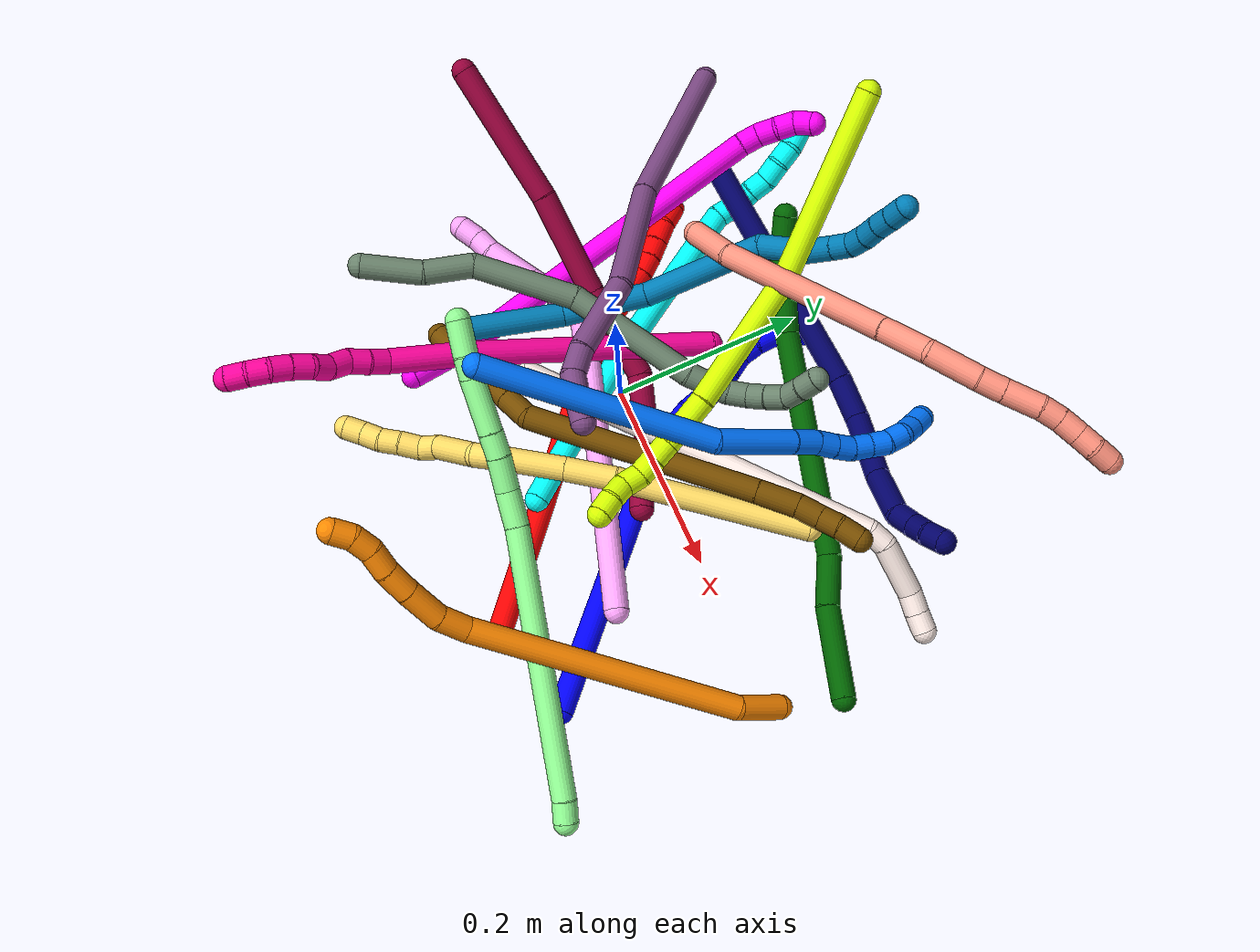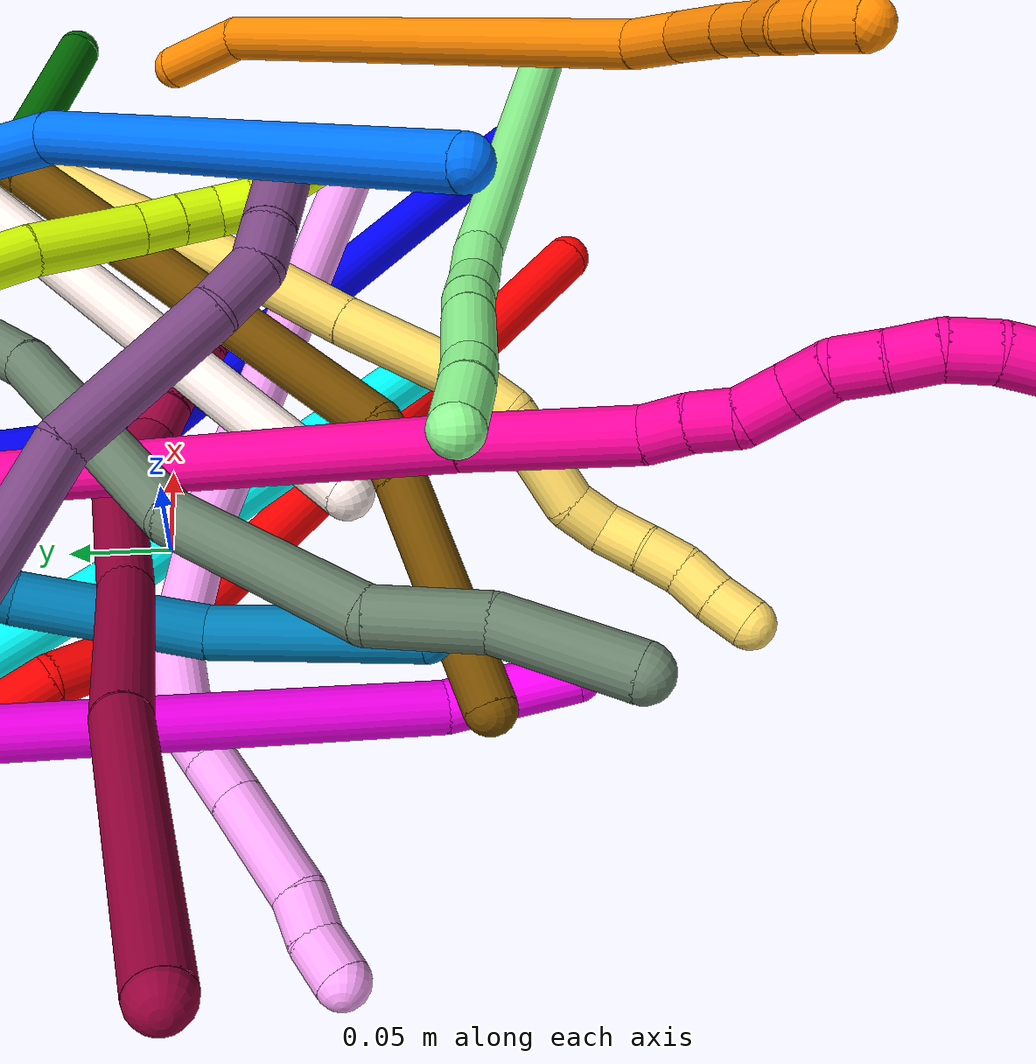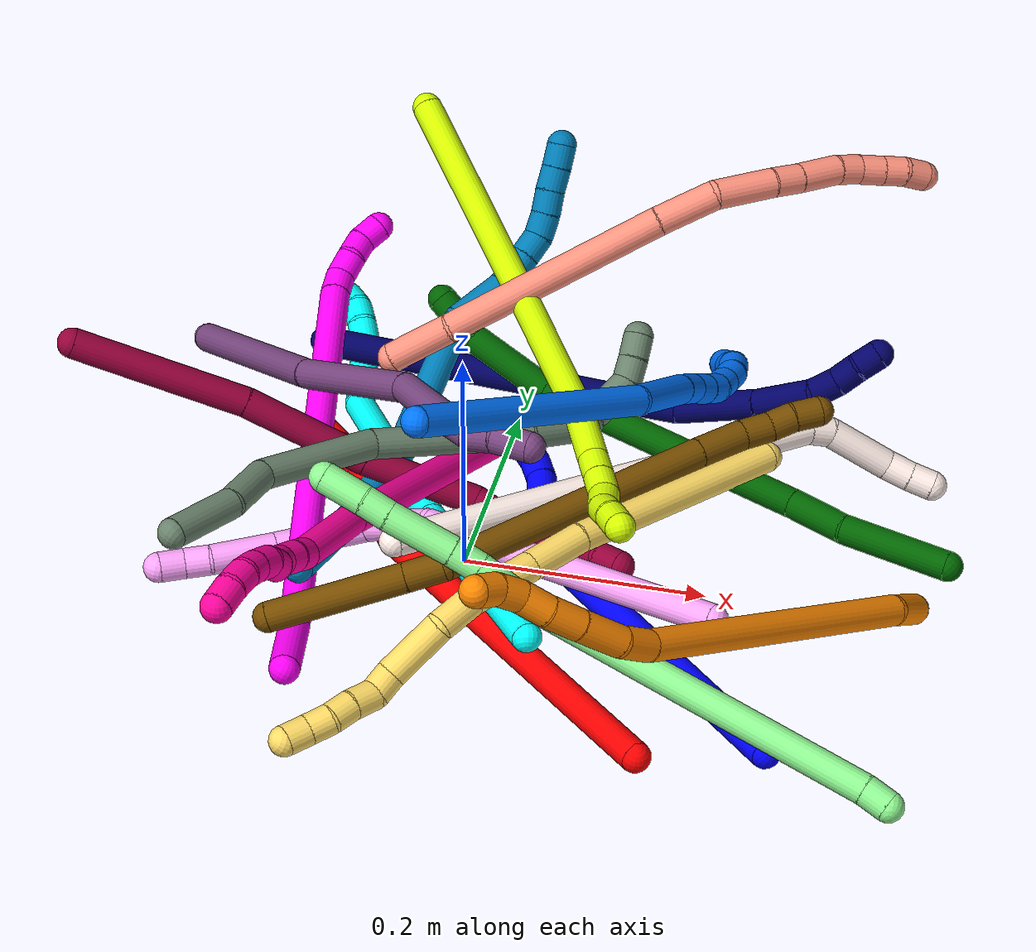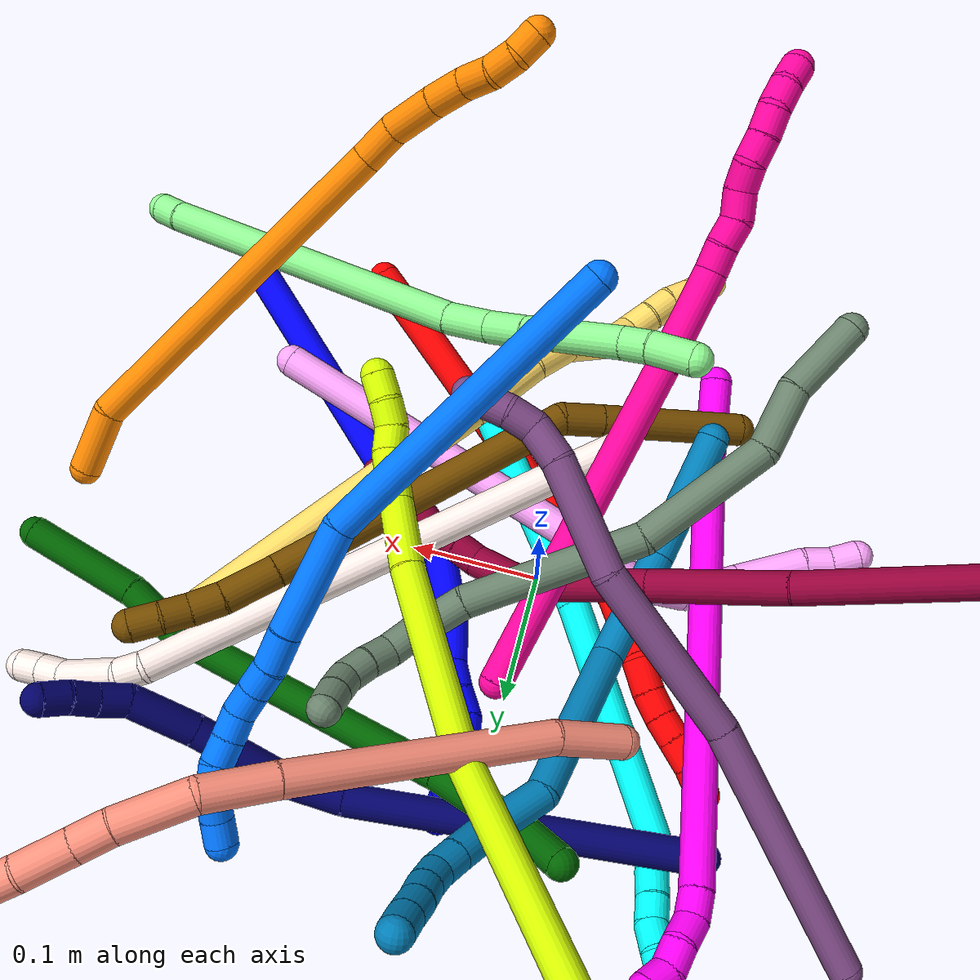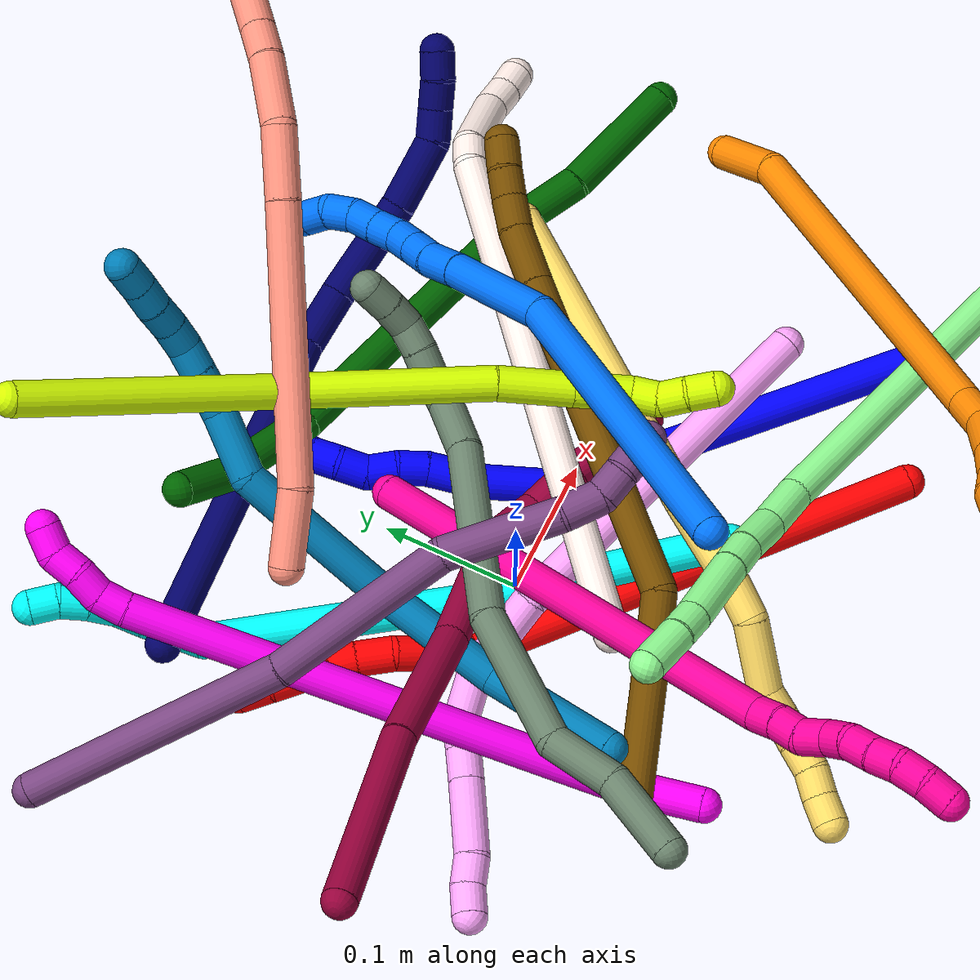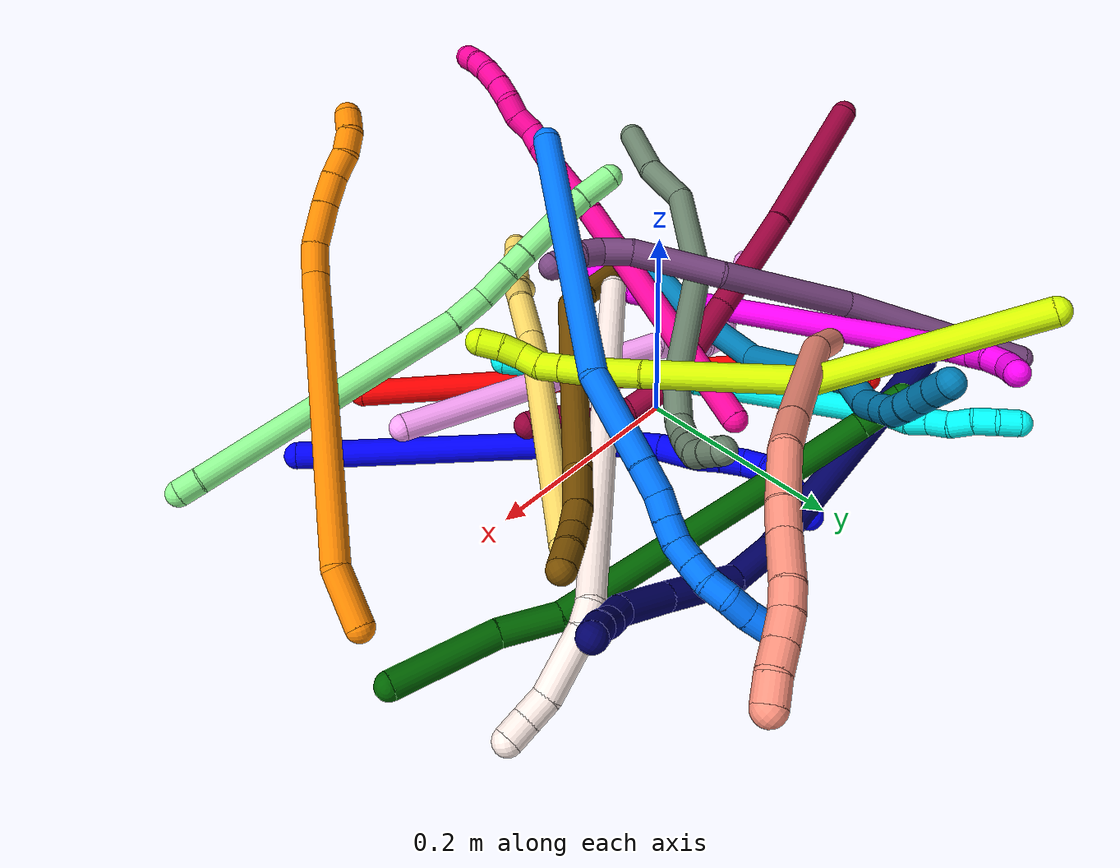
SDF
<sdf version="1.7">
 <world name="default">
  <plugin name="TubeGeneratorPlugin" filename="libtube_generator_plugin.so"/>
  <model name="photoneo_s_sensor">
   <static>1</static>
   <pose>0 0 2 1.57079 1.57079 3.14159</pose>
   <link name="link">
    <inertial><mass>0.1</mass></inertial>
    <sensor name="sensor" type="depth">
     <update_rate>30</update_rate>
     <camera>
      <horizontal_fov>1.22</horizontal_fov>
      <image><width>1920</width><height>1200</height><format>B8G8R8</format></image>
      <clip><near>0.1</near><far>4</far></clip>
      <depth_camera><output>points</output></depth_camera>
     </camera>
     <plugin name="camera_plugin" filename="libgazebo_ros_depth_camera.so">
      <baseline>0.2</baseline>
      <alwaysOn>1</alwaysOn>
      <updateRate>0.0</updateRate>
      <cameraName>camera_ir</cameraName>
      <imageTopicName>/camera/color/image_raw</imageTopicName>
      <cameraInfoTopicName>/camera/color/camera_info</cameraInfoTopicName>
      <depthImageTopicName>/camera/depth/image_raw</depthImageTopicName>
      <depthImageCameraInfoTopicName>/camera/depth/camera_info</depthImageCameraInfoTopicName>
      <pointCloudTopicName>/camera/depth/points</pointCloudTopicName>
      <frameName>fr_optical</frameName>
      <pointCloudCutoff>0.1</pointCloudCutoff>
      <pointCloudCutoffMax>2.0</pointCloudCutoffMax>
      <distortionK1>0</distortionK1>
      <distortionK2>0</distortionK2>
      <distortionK3>0</distortionK3>
      <distortionT1>0</distortionT1>
      <distortionT2>0</distortionT2>
      <CxPrime>0</CxPrime>
      <Cx>0</Cx>
      <Cy>0</Cy>
      <focalLength>0</focalLength>
      <hackBaseline>0</hackBaseline>
     </plugin>
    </sensor>
   </link>
  </model>
  <gravity>0 0 -9.8</gravity>
  <magnetic_field>6e-06 2.3e-05 -4.2e-05</magnetic_field>
  <atmosphere type="adiabatic"/>
  <physics name="default_physics" default="0" type="ode">
   <max_step_size>0.003</max_step_size>
   <real_time_factor>1</real_time_factor>
   <real_time_update_rate>1000</real_time_update_rate>
   <max_contacts>10000</max_contacts>
   <ode>
    <solver>
     <type>quick</type>
     <iters>100</iters>
     <sor>1.3</sor>
     <use_dynamic_moi_rescaling>0</use_dynamic_moi_rescaling>
    </solver>
    <constraints>
     <contact_max_correcting_vel>0</contact_max_correcting_vel>
     <contact_surface_layer>0.001</contact_surface_layer>
     <cfm>0</cfm>
     <erp>0.2</erp>
    </constraints>
   </ode>
  </physics>
  <scene><ambient>0.4 0.4 0.4 1</ambient><background>0.7 0.7 0.7 1</background><shadows>0</shadows></scene>
  <audio><device>default</device></audio>
  <spherical_coordinates>
   <surface_model>EARTH_WGS84</surface_model>
   <latitude_deg>0</latitude_deg>
   <longitude_deg>0</longitude_deg>
   <elevation>0</elevation>
   <heading_deg>0</heading_deg>
  </spherical_coordinates>
  <model name="bin">
   <static>1</static>
   <link name="bottom">
    <collision name="collision-bottom">
     <pose>0 0 -0.01 0 -0 0</pose>
     <geometry><box><size>0.8 0.6 0.02</size></box></geometry>
     <surface>
      <friction><ode><mu>100</mu><mu2>100</mu2></ode></friction>
      <contact><collide_bitmask>65535</collide_bitmask></contact>
     </surface>
    </collision>
   </link>
   <link name="west_wall">
    <collision name="collision-west_wall">
     <pose>-0.41 0 0.1 0 -0 0</pose>
     <geometry><box><size>0.02 0.6 0.2</size></box></geometry>
     <surface>
      <friction><ode><mu>100</mu><mu2>100</mu2></ode></friction>
      <contact><collide_bitmask>65535</collide_bitmask></contact>
     </surface>
    </collision>
   </link>
   <link name="east_wall">
    <collision name="collision-east_wall">
     <pose>0.41 0 0.1 0 -0 0</pose>
     <geometry><box><size>0.02 0.6 0.2</size></box></geometry>
     <surface>
      <friction><ode><mu>100</mu><mu2>100</mu2></ode></friction>
      <contact><collide_bitmask>65535</collide_bitmask></contact>
     </surface>
    </collision>
   </link>
   <link name="south_wall">
    <collision name="collision-south_wall">
     <pose>0 -0.31 0.1 0 -0 0</pose>
     <geometry><box><size>0.8 0.02 0.2</size></box></geometry>
     <surface>
      <friction><ode><mu>100</mu><mu2>100</mu2></ode></friction>
      <contact><collide_bitmask>65535</collide_bitmask></contact>
     </surface>
    </collision>
   </link>
   <link name="north_wall">
    <collision name="collision-north_wall">
     <pose>0 0.31 0.1 0 -0 0</pose>
     <geometry><box><size>0.8 0.02 0.2</size></box></geometry>
     <surface>
      <friction><ode><mu>100</mu><mu2>100</mu2></ode></friction>
      <contact><collide_bitmask>65535</collide_bitmask></contact>
     </surface>
    </collision>
   </link>
  </model>
  <model name="1">
   <static>0</static>
   <link name="1">
    <collision name="collision-cylinder-e_1_1_4">
     <pose>-0.063606 0.108191 -0.068221 -2.13339 -0.461484 0.805209</pose>
     <geometry><cylinder><radius>0.0125</radius><length>0.285693</length></cylinder></geometry>
     <surface>
      <friction><ode><mu>1.16</mu><mu2>1.16</mu2><slip1>0</slip1><slip2>0</slip2></ode></friction>
      <contact><ode><kp>1e+06</kp><kd>1</kd><max_vel>0</max_vel><min_depth>0.001</min_depth></ode></contact>
     </surface>
    </collision>
    <visual name="visual-cylinder-e_1_1_4">
     <pose>-0.063606 0.108191 -0.068221 -2.13339 -0.461484 0.805209</pose>
     <geometry><cylinder><radius>0.0125</radius><length>0.285693</length></cylinder></geometry>
     <material><ambient>0 0 1 1</ambient></material>
    </visual>
    <collision name="collision-cylinder-e_2_4_5">
     <pose>-0.133807 0.241659 -0.141501 -1.76833 -0.250417 0.304729</pose>
     <geometry><cylinder><radius>0.0125</radius><length>0.053216</length></cylinder></geometry>
     <surface>
      <friction><ode><mu>1.16</mu><mu2>1.16</mu2><slip1>0</slip1><slip2>0</slip2></ode></friction>
      <contact><ode><kp>1e+06</kp><kd>1</kd><max_vel>0</max_vel><min_depth>0.001</min_depth></ode></contact>
     </surface>
    </collision>
    <visual name="visual-cylinder-e_2_4_5">
     <pose>-0.133807 0.241659 -0.141501 -1.76833 -0.250417 0.304729</pose>
     <geometry><cylinder><radius>0.0125</radius><length>0.053216</length></cylinder></geometry>
     <material><ambient>0 0 1 1</ambient></material>
    </visual>
    <collision name="collision-cylinder-e_3_5_6">
     <pose>-0.141737 0.285508 -0.148725 -1.68683 -0.071394 0.080189</pose>
     <geometry><cylinder><radius>0.0125</radius><length>0.037493</length></cylinder></geometry>
     <surface>
      <friction><ode><mu>1.16</mu><mu2>1.16</mu2><slip1>0</slip1><slip2>0</slip2></ode></friction>
      <contact><ode><kp>1e+06</kp><kd>1</kd><max_vel>0</max_vel><min_depth>0.001</min_depth></ode></contact>
     </surface>
    </collision>
    <visual name="visual-cylinder-e_3_5_6">
     <pose>-0.141737 0.285508 -0.148725 -1.68683 -0.071394 0.080189</pose>
     <geometry><cylinder><radius>0.0125</radius><length>0.037493</length></cylinder></geometry>
     <material><ambient>0 0 1 1</ambient></material>
    </visual>
    <collision name="collision-cylinder-e_4_6_7">
     <pose>-0.145954 0.314001 -0.153238 -1.80321 -0.275259 0.346715</pose>
     <geometry><cylinder><radius>0.0125</radius><length>0.021185</length></cylinder></geometry>
     <surface>
      <friction><ode><mu>1.16</mu><mu2>1.16</mu2><slip1>0</slip1><slip2>0</slip2></ode></friction>
      <contact><ode><kp>1e+06</kp><kd>1</kd><max_vel>0</max_vel><min_depth>0.001</min_depth></ode></contact>
     </surface>
    </collision>
    <visual name="visual-cylinder-e_4_6_7">
     <pose>-0.145954 0.314001 -0.153238 -1.80321 -0.275259 0.346715</pose>
     <geometry><cylinder><radius>0.0125</radius><length>0.021185</length></cylinder></geometry>
     <material><ambient>0 0 1 1</ambient></material>
    </visual>
    <collision name="collision-cylinder-e_5_7_8">
     <pose>-0.151347 0.333117 -0.160341 -2.04802 -0.238231 0.388292</pose>
     <geometry><cylinder><radius>0.0125</radius><length>0.021307</length></cylinder></geometry>
     <surface>
      <friction><ode><mu>1.16</mu><mu2>1.16</mu2><slip1>0</slip1><slip2>0</slip2></ode></friction>
      <contact><ode><kp>1e+06</kp><kd>1</kd><max_vel>0</max_vel><min_depth>0.001</min_depth></ode></contact>
     </surface>
    </collision>
    <visual name="visual-cylinder-e_5_7_8">
     <pose>-0.151347 0.333117 -0.160341 -2.04802 -0.238231 0.388292</pose>
     <geometry><cylinder><radius>0.0125</radius><length>0.021307</length></cylinder></geometry>
     <material><ambient>0 0 1 1</ambient></material>
    </visual>
    <collision name="collision-cylinder-e_6_8_9">
     <pose>-0.15434 0.352674 -0.165393 -1.59943 -0.046162 0.047503</pose>
     <geometry><cylinder><radius>0.0125</radius><length>0.020754</length></cylinder></geometry>
     <surface>
      <friction><ode><mu>1.16</mu><mu2>1.16</mu2><slip1>0</slip1><slip2>0</slip2></ode></friction>
      <contact><ode><kp>1e+06</kp><kd>1</kd><max_vel>0</max_vel><min_depth>0.001</min_depth></ode></contact>
     </surface>
    </collision>
    <visual name="visual-cylinder-e_6_8_9">
     <pose>-0.15434 0.352674 -0.165393 -1.59943 -0.046162 0.047503</pose>
     <geometry><cylinder><radius>0.0125</radius><length>0.020754</length></cylinder></geometry>
     <material><ambient>0 0 1 1</ambient></material>
    </visual>
    <collision name="collision-cylinder-e_7_9_10">
     <pose>-0.153124 0.372863 -0.167551 -1.75802 0.167791 -0.202346</pose>
     <geometry><cylinder><radius>0.0125</radius><length>0.020289</length></cylinder></geometry>
     <surface>
      <friction><ode><mu>1.16</mu><mu2>1.16</mu2><slip1>0</slip1><slip2>0</slip2></ode></friction>
      <contact><ode><kp>1e+06</kp><kd>1</kd><max_vel>0</max_vel><min_depth>0.001</min_depth></ode></contact>
     </surface>
    </collision>
    <visual name="visual-cylinder-e_7_9_10">
     <pose>-0.153124 0.372863 -0.167551 -1.75802 0.167791 -0.202346</pose>
     <geometry><cylinder><radius>0.0125</radius><length>0.020289</length></cylinder></geometry>
     <material><ambient>0 0 1 1</ambient></material>
    </visual>
    <collision name="collision-cylinder-e_8_10_11">
     <pose>-0.146012 0.390614 -0.172305 -1.92077 0.570919 -0.794456</pose>
     <geometry><cylinder><radius>0.0125</radius><length>0.020051</length></cylinder></geometry>
     <surface>
      <friction><ode><mu>1.16</mu><mu2>1.16</mu2><slip1>0</slip1><slip2>0</slip2></ode></friction>
      <contact><ode><kp>1e+06</kp><kd>1</kd><max_vel>0</max_vel><min_depth>0.001</min_depth></ode></contact>
     </surface>
    </collision>
    <visual name="visual-cylinder-e_8_10_11">
     <pose>-0.146012 0.390614 -0.172305 -1.92077 0.570919 -0.794456</pose>
     <geometry><cylinder><radius>0.0125</radius><length>0.020051</length></cylinder></geometry>
     <material><ambient>0 0 1 1</ambient></material>
    </visual>
    <collision name="collision-cylinder-e_9_11_2">
     <pose>-0.13494 0.405295 -0.179941 -2.18289 0.600491 -1.07442</pose>
     <geometry><cylinder><radius>0.0125</radius><length>0.020012</length></cylinder></geometry>
     <surface>
      <friction><ode><mu>1.16</mu><mu2>1.16</mu2><slip1>0</slip1><slip2>0</slip2></ode></friction>
      <contact><ode><kp>1e+06</kp><kd>1</kd><max_vel>0</max_vel><min_depth>0.001</min_depth></ode></contact>
     </surface>
    </collision>
    <visual name="visual-cylinder-e_9_11_2">
     <pose>-0.13494 0.405295 -0.179941 -2.18289 0.600491 -1.07442</pose>
     <geometry><cylinder><radius>0.0125</radius><length>0.020012</length></cylinder></geometry>
     <material><ambient>0 0 1 1</ambient></material>
    </visual>
    <collision name="collision-sphere-2">
     <pose>-0.129287 0.412052 -0.184685 0 -0 0</pose>
     <geometry><sphere><radius>0.0125</radius></sphere></geometry>
     <surface>
      <friction><ode><mu>1.16</mu><mu2>1.16</mu2><slip1>0</slip1><slip2>0</slip2></ode></friction>
      <contact><ode><kp>1e+06</kp><kd>1</kd><max_vel>0</max_vel><min_depth>0.001</min_depth></ode></contact>
     </surface>
    </collision>
    <visual name="visual-sphere-2">
     <pose>-0.129287 0.412052 -0.184685 0 -0 0</pose>
     <geometry><sphere><radius>0.0125</radius></sphere></geometry>
     <material><ambient>0 0 1 1</ambient></material>
    </visual>
    <collision name="collision-sphere-11">
     <pose>-0.140594 0.398538 -0.175198 0 -0 0</pose>
     <geometry><sphere><radius>0.0125</radius></sphere></geometry>
     <surface>
      <friction><ode><mu>1.16</mu><mu2>1.16</mu2><slip1>0</slip1><slip2>0</slip2></ode></friction>
      <contact><ode><kp>1e+06</kp><kd>1</kd><max_vel>0</max_vel><min_depth>0.001</min_depth></ode></contact>
     </surface>
    </collision>
    <visual name="visual-sphere-11">
     <pose>-0.140594 0.398538 -0.175198 0 -0 0</pose>
     <geometry><sphere><radius>0.0125</radius></sphere></geometry>
     <material><ambient>0 0 1 1</ambient></material>
    </visual>
    <collision name="collision-sphere-10">
     <pose>-0.15143 0.38269 -0.169413 0 -0 0</pose>
     <geometry><sphere><radius>0.0125</radius></sphere></geometry>
     <surface>
      <friction><ode><mu>1.16</mu><mu2>1.16</mu2><slip1>0</slip1><slip2>0</slip2></ode></friction>
      <contact><ode><kp>1e+06</kp><kd>1</kd><max_vel>0</max_vel><min_depth>0.001</min_depth></ode></contact>
     </surface>
    </collision>
    <visual name="visual-sphere-10">
     <pose>-0.15143 0.38269 -0.169413 0 -0 0</pose>
     <geometry><sphere><radius>0.0125</radius></sphere></geometry>
     <material><ambient>0 0 1 1</ambient></material>
    </visual>
    <collision name="collision-sphere-9">
     <pose>-0.154818 0.363036 -0.165689 0 -0 0</pose>
     <geometry><sphere><radius>0.0125</radius></sphere></geometry>
     <surface>
      <friction><ode><mu>1.16</mu><mu2>1.16</mu2><slip1>0</slip1><slip2>0</slip2></ode></friction>
      <contact><ode><kp>1e+06</kp><kd>1</kd><max_vel>0</max_vel><min_depth>0.001</min_depth></ode></contact>
     </surface>
    </collision>
    <visual name="visual-sphere-9">
     <pose>-0.154818 0.363036 -0.165689 0 -0 0</pose>
     <geometry><sphere><radius>0.0125</radius></sphere></geometry>
     <material><ambient>0 0 1 1</ambient></material>
    </visual>
    <collision name="collision-sphere-4">
     <pose>-0.127213 0.216382 -0.136442 0 -0 0</pose>
     <geometry><sphere><radius>0.0125</radius></sphere></geometry>
     <surface>
      <friction><ode><mu>1.16</mu><mu2>1.16</mu2><slip1>0</slip1><slip2>0</slip2></ode></friction>
      <contact><ode><kp>1e+06</kp><kd>1</kd><max_vel>0</max_vel><min_depth>0.001</min_depth></ode></contact>
     </surface>
    </collision>
    <visual name="visual-sphere-4">
     <pose>-0.127213 0.216382 -0.136442 0 -0 0</pose>
     <geometry><sphere><radius>0.0125</radius></sphere></geometry>
     <material><ambient>0 0 1 1</ambient></material>
    </visual>
    <collision name="collision-sphere-1">
     <geometry><sphere><radius>0.0125</radius></sphere></geometry>
     <surface>
      <friction><ode><mu>1.16</mu><mu2>1.16</mu2><slip1>0</slip1><slip2>0</slip2></ode></friction>
      <contact><ode><kp>1e+06</kp><kd>1</kd><max_vel>0</max_vel><min_depth>0.001</min_depth></ode></contact>
     </surface>
    </collision>
    <visual name="visual-sphere-1">
     <geometry><sphere><radius>0.0125</radius></sphere></geometry>
     <material><ambient>0 0 1 1</ambient></material>
    </visual>
    <collision name="collision-sphere-8">
     <pose>-0.153861 0.342313 -0.165096 0 -0 0</pose>
     <geometry><sphere><radius>0.0125</radius></sphere></geometry>
     <surface>
      <friction><ode><mu>1.16</mu><mu2>1.16</mu2><slip1>0</slip1><slip2>0</slip2></ode></friction>
      <contact><ode><kp>1e+06</kp><kd>1</kd><max_vel>0</max_vel><min_depth>0.001</min_depth></ode></contact>
     </surface>
    </collision>
    <visual name="visual-sphere-8">
     <pose>-0.153861 0.342313 -0.165096 0 -0 0</pose>
     <geometry><sphere><radius>0.0125</radius></sphere></geometry>
     <material><ambient>0 0 1 1</ambient></material>
    </visual>
    <collision name="collision-sphere-5">
     <pose>-0.1404 0.266935 -0.14656 0 -0 0</pose>
     <geometry><sphere><radius>0.0125</radius></sphere></geometry>
     <surface>
      <friction><ode><mu>1.16</mu><mu2>1.16</mu2><slip1>0</slip1><slip2>0</slip2></ode></friction>
      <contact><ode><kp>1e+06</kp><kd>1</kd><max_vel>0</max_vel><min_depth>0.001</min_depth></ode></contact>
     </surface>
    </collision>
    <visual name="visual-sphere-5">
     <pose>-0.1404 0.266935 -0.14656 0 -0 0</pose>
     <geometry><sphere><radius>0.0125</radius></sphere></geometry>
     <material><ambient>0 0 1 1</ambient></material>
    </visual>
    <collision name="collision-sphere-6">
     <pose>-0.143075 0.304081 -0.15089 0 -0 0</pose>
     <geometry><sphere><radius>0.0125</radius></sphere></geometry>
     <surface>
      <friction><ode><mu>1.16</mu><mu2>1.16</mu2><slip1>0</slip1><slip2>0</slip2></ode></friction>
      <contact><ode><kp>1e+06</kp><kd>1</kd><max_vel>0</max_vel><min_depth>0.001</min_depth></ode></contact>
     </surface>
    </collision>
    <visual name="visual-sphere-6">
     <pose>-0.143075 0.304081 -0.15089 0 -0 0</pose>
     <geometry><sphere><radius>0.0125</radius></sphere></geometry>
     <material><ambient>0 0 1 1</ambient></material>
    </visual>
    <collision name="collision-sphere-7">
     <pose>-0.148833 0.323921 -0.155586 0 -0 0</pose>
     <geometry><sphere><radius>0.0125</radius></sphere></geometry>
     <surface>
      <friction><ode><mu>1.16</mu><mu2>1.16</mu2><slip1>0</slip1><slip2>0</slip2></ode></friction>
      <contact><ode><kp>1e+06</kp><kd>1</kd><max_vel>0</max_vel><min_depth>0.001</min_depth></ode></contact>
     </surface>
    </collision>
    <visual name="visual-sphere-7">
     <pose>-0.148833 0.323921 -0.155586 0 -0 0</pose>
     <geometry><sphere><radius>0.0125</radius></sphere></geometry>
     <material><ambient>0 0 1 1</ambient></material>
    </visual>
    <inertial>
     <pose>-0.097723 0.198102 -0.106294 0 -0 0</pose>
     <mass>0.5</mass>
     <inertia>
      <ixx>0.002495</ixx>
      <ixy>0</ixy>
      <ixz>0</ixz>
      <iyy>0.001103</iyy>
      <iyz>0</iyz>
      <izz>-0.000649</izz>
     </inertia>
    </inertial>
   </link>
   <pose>0.282916 -0.190446 0.012769 0.235091 0.56575 0.252354</pose>
  </model>
  <model name="2">
   <static>0</static>
   <link name="2">
    <collision name="collision-cylinder-e_1_1_4">
     <pose>-0.121181 0.103373 0.044527 -1.16408 -0.822285 0.558825</pose>
     <geometry><cylinder><radius>0.0125</radius><length>0.330778</length></cylinder></geometry>
     <surface>
      <friction><ode><mu>1.16</mu><mu2>1.16</mu2><slip1>0</slip1><slip2>0</slip2></ode></friction>
      <contact><ode><kp>1e+06</kp><kd>1</kd><max_vel>0</max_vel><min_depth>0.001</min_depth></ode></contact>
     </surface>
    </collision>
    <visual name="visual-cylinder-e_1_1_4">
     <pose>-0.121181 0.103373 0.044527 -1.16408 -0.822285 0.558825</pose>
     <geometry><cylinder><radius>0.0125</radius><length>0.330778</length></cylinder></geometry>
     <material><ambient>1 0 0 1</ambient></material>
    </visual>
    <collision name="collision-cylinder-e_2_4_5">
     <pose>-0.268485 0.218143 0.089789 -1.50637 -1.15867 1.10039</pose>
     <geometry><cylinder><radius>0.0125</radius><length>0.05702</length></cylinder></geometry>
     <surface>
      <friction><ode><mu>1.16</mu><mu2>1.16</mu2><slip1>0</slip1><slip2>0</slip2></ode></friction>
      <contact><ode><kp>1e+06</kp><kd>1</kd><max_vel>0</max_vel><min_depth>0.001</min_depth></ode></contact>
     </surface>
    </collision>
    <visual name="visual-cylinder-e_2_4_5">
     <pose>-0.268485 0.218143 0.089789 -1.50637 -1.15867 1.10039</pose>
     <geometry><cylinder><radius>0.0125</radius><length>0.05702</length></cylinder></geometry>
     <material><ambient>1 0 0 1</ambient></material>
    </visual>
    <collision name="collision-cylinder-e_3_5_6">
     <pose>-0.305881 0.234302 0.095413 -0.772429 -1.02635 0.450532</pose>
     <geometry><cylinder><radius>0.0125</radius><length>0.026356</length></cylinder></geometry>
     <surface>
      <friction><ode><mu>1.16</mu><mu2>1.16</mu2><slip1>0</slip1><slip2>0</slip2></ode></friction>
      <contact><ode><kp>1e+06</kp><kd>1</kd><max_vel>0</max_vel><min_depth>0.001</min_depth></ode></contact>
     </surface>
    </collision>
    <visual name="visual-cylinder-e_3_5_6">
     <pose>-0.305881 0.234302 0.095413 -0.772429 -1.02635 0.450532</pose>
     <geometry><cylinder><radius>0.0125</radius><length>0.026356</length></cylinder></geometry>
     <material><ambient>1 0 0 1</ambient></material>
    </visual>
    <collision name="collision-cylinder-e_4_6_7">
     <pose>-0.325422 0.244089 0.103664 -0.980862 -0.93946 0.529367</pose>
     <geometry><cylinder><radius>0.0125</radius><length>0.020486</length></cylinder></geometry>
     <surface>
      <friction><ode><mu>1.16</mu><mu2>1.16</mu2><slip1>0</slip1><slip2>0</slip2></ode></friction>
      <contact><ode><kp>1e+06</kp><kd>1</kd><max_vel>0</max_vel><min_depth>0.001</min_depth></ode></contact>
     </surface>
    </collision>
    <visual name="visual-cylinder-e_4_6_7">
     <pose>-0.325422 0.244089 0.103664 -0.980862 -0.93946 0.529367</pose>
     <geometry><cylinder><radius>0.0125</radius><length>0.020486</length></cylinder></geometry>
     <material><ambient>1 0 0 1</ambient></material>
    </visual>
    <collision name="collision-cylinder-e_5_7_8">
     <pose>-0.341407 0.254832 0.109908 -1.10424 -0.878174 0.563274</pose>
     <geometry><cylinder><radius>0.0125</radius><length>0.020055</length></cylinder></geometry>
     <surface>
      <friction><ode><mu>1.16</mu><mu2>1.16</mu2><slip1>0</slip1><slip2>0</slip2></ode></friction>
      <contact><ode><kp>1e+06</kp><kd>1</kd><max_vel>0</max_vel><min_depth>0.001</min_depth></ode></contact>
     </surface>
    </collision>
    <visual name="visual-cylinder-e_5_7_8">
     <pose>-0.341407 0.254832 0.109908 -1.10424 -0.878174 0.563274</pose>
     <geometry><cylinder><radius>0.0125</radius><length>0.020055</length></cylinder></geometry>
     <material><ambient>1 0 0 1</ambient></material>
    </visual>
    <collision name="collision-cylinder-e_6_8_9">
     <pose>-0.357733 0.266861 0.116058 -1.09275 -0.880657 0.558123</pose>
     <geometry><cylinder><radius>0.0125</radius><length>0.022327</length></cylinder></geometry>
     <surface>
      <friction><ode><mu>1.16</mu><mu2>1.16</mu2><slip1>0</slip1><slip2>0</slip2></ode></friction>
      <contact><ode><kp>1e+06</kp><kd>1</kd><max_vel>0</max_vel><min_depth>0.001</min_depth></ode></contact>
     </surface>
    </collision>
    <visual name="visual-cylinder-e_6_8_9">
     <pose>-0.357733 0.266861 0.116058 -1.09275 -0.880657 0.558123</pose>
     <geometry><cylinder><radius>0.0125</radius><length>0.022327</length></cylinder></geometry>
     <material><ambient>1 0 0 1</ambient></material>
    </visual>
    <collision name="collision-cylinder-e_7_9_2">
     <pose>-0.374847 0.27822 0.125173 -0.712341 -0.833476 0.326446</pose>
     <geometry><cylinder><radius>0.0125</radius><length>0.022978</length></cylinder></geometry>
     <surface>
      <friction><ode><mu>1.16</mu><mu2>1.16</mu2><slip1>0</slip1><slip2>0</slip2></ode></friction>
      <contact><ode><kp>1e+06</kp><kd>1</kd><max_vel>0</max_vel><min_depth>0.001</min_depth></ode></contact>
     </surface>
    </collision>
    <visual name="visual-cylinder-e_7_9_2">
     <pose>-0.374847 0.27822 0.125173 -0.712341 -0.833476 0.326446</pose>
     <geometry><cylinder><radius>0.0125</radius><length>0.022978</length></cylinder></geometry>
     <material><ambient>1 0 0 1</ambient></material>
    </visual>
    <collision name="collision-sphere-2">
     <pose>-0.383352 0.283269 0.131019 0 -0 0</pose>
     <geometry><sphere><radius>0.0125</radius></sphere></geometry>
     <surface>
      <friction><ode><mu>1.16</mu><mu2>1.16</mu2><slip1>0</slip1><slip2>0</slip2></ode></friction>
      <contact><ode><kp>1e+06</kp><kd>1</kd><max_vel>0</max_vel><min_depth>0.001</min_depth></ode></contact>
     </surface>
    </collision>
    <visual name="visual-sphere-2">
     <pose>-0.383352 0.283269 0.131019 0 -0 0</pose>
     <geometry><sphere><radius>0.0125</radius></sphere></geometry>
     <material><ambient>1 0 0 1</ambient></material>
    </visual>
    <collision name="collision-sphere-9">
     <pose>-0.366342 0.273172 0.119327 0 -0 0</pose>
     <geometry><sphere><radius>0.0125</radius></sphere></geometry>
     <surface>
      <friction><ode><mu>1.16</mu><mu2>1.16</mu2><slip1>0</slip1><slip2>0</slip2></ode></friction>
      <contact><ode><kp>1e+06</kp><kd>1</kd><max_vel>0</max_vel><min_depth>0.001</min_depth></ode></contact>
     </surface>
    </collision>
    <visual name="visual-sphere-9">
     <pose>-0.366342 0.273172 0.119327 0 -0 0</pose>
     <geometry><sphere><radius>0.0125</radius></sphere></geometry>
     <material><ambient>1 0 0 1</ambient></material>
    </visual>
    <collision name="collision-sphere-4">
     <pose>-0.242362 0.206747 0.089054 0 -0 0</pose>
     <geometry><sphere><radius>0.0125</radius></sphere></geometry>
     <surface>
      <friction><ode><mu>1.16</mu><mu2>1.16</mu2><slip1>0</slip1><slip2>0</slip2></ode></friction>
      <contact><ode><kp>1e+06</kp><kd>1</kd><max_vel>0</max_vel><min_depth>0.001</min_depth></ode></contact>
     </surface>
    </collision>
    <visual name="visual-sphere-4">
     <pose>-0.242362 0.206747 0.089054 0 -0 0</pose>
     <geometry><sphere><radius>0.0125</radius></sphere></geometry>
     <material><ambient>1 0 0 1</ambient></material>
    </visual>
    <collision name="collision-sphere-1">
     <geometry><sphere><radius>0.0125</radius></sphere></geometry>
     <surface>
      <friction><ode><mu>1.16</mu><mu2>1.16</mu2><slip1>0</slip1><slip2>0</slip2></ode></friction>
      <contact><ode><kp>1e+06</kp><kd>1</kd><max_vel>0</max_vel><min_depth>0.001</min_depth></ode></contact>
     </surface>
    </collision>
    <visual name="visual-sphere-1">
     <geometry><sphere><radius>0.0125</radius></sphere></geometry>
     <material><ambient>1 0 0 1</ambient></material>
    </visual>
    <collision name="collision-sphere-8">
     <pose>-0.349124 0.260551 0.112788 0 -0 0</pose>
     <geometry><sphere><radius>0.0125</radius></sphere></geometry>
     <surface>
      <friction><ode><mu>1.16</mu><mu2>1.16</mu2><slip1>0</slip1><slip2>0</slip2></ode></friction>
      <contact><ode><kp>1e+06</kp><kd>1</kd><max_vel>0</max_vel><min_depth>0.001</min_depth></ode></contact>
     </surface>
    </collision>
    <visual name="visual-sphere-8">
     <pose>-0.349124 0.260551 0.112788 0 -0 0</pose>
     <geometry><sphere><radius>0.0125</radius></sphere></geometry>
     <material><ambient>1 0 0 1</ambient></material>
    </visual>
    <collision name="collision-sphere-5">
     <pose>-0.294608 0.229539 0.090524 0 -0 0</pose>
     <geometry><sphere><radius>0.0125</radius></sphere></geometry>
     <surface>
      <friction><ode><mu>1.16</mu><mu2>1.16</mu2><slip1>0</slip1><slip2>0</slip2></ode></friction>
      <contact><ode><kp>1e+06</kp><kd>1</kd><max_vel>0</max_vel><min_depth>0.001</min_depth></ode></contact>
     </surface>
    </collision>
    <visual name="visual-sphere-5">
     <pose>-0.294608 0.229539 0.090524 0 -0 0</pose>
     <geometry><sphere><radius>0.0125</radius></sphere></geometry>
     <material><ambient>1 0 0 1</ambient></material>
    </visual>
    <collision name="collision-sphere-6">
     <pose>-0.317153 0.239066 0.100301 0 -0 0</pose>
     <geometry><sphere><radius>0.0125</radius></sphere></geometry>
     <surface>
      <friction><ode><mu>1.16</mu><mu2>1.16</mu2><slip1>0</slip1><slip2>0</slip2></ode></friction>
      <contact><ode><kp>1e+06</kp><kd>1</kd><max_vel>0</max_vel><min_depth>0.001</min_depth></ode></contact>
     </surface>
    </collision>
    <visual name="visual-sphere-6">
     <pose>-0.317153 0.239066 0.100301 0 -0 0</pose>
     <geometry><sphere><radius>0.0125</radius></sphere></geometry>
     <material><ambient>1 0 0 1</ambient></material>
    </visual>
    <collision name="collision-sphere-7">
     <pose>-0.33369 0.249113 0.107027 0 -0 0</pose>
     <geometry><sphere><radius>0.0125</radius></sphere></geometry>
     <surface>
      <friction><ode><mu>1.16</mu><mu2>1.16</mu2><slip1>0</slip1><slip2>0</slip2></ode></friction>
      <contact><ode><kp>1e+06</kp><kd>1</kd><max_vel>0</max_vel><min_depth>0.001</min_depth></ode></contact>
     </surface>
    </collision>
    <visual name="visual-sphere-7">
     <pose>-0.33369 0.249113 0.107027 0 -0 0</pose>
     <geometry><sphere><radius>0.0125</radius></sphere></geometry>
     <material><ambient>1 0 0 1</ambient></material>
    </visual>
    <inertial>
     <pose>-0.187137 0.150539 0.064316 0 -0 0</pose>
     <mass>0.5</mass>
     <inertia>
      <ixx>0.002828</ixx>
      <ixy>0</ixy>
      <ixz>0</ixz>
      <iyy>0.003243</iyy>
      <iyz>0</iyz>
      <izz>0.000348</izz>
     </inertia>
    </inertial>
   </link>
   <pose>0.186864 -0.21618 0.011496 2.99724 0.236372 -1.43744</pose>
  </model>
  <model name="3">
   <static>0</static>
   <link name="3">
    <collision name="collision-cylinder-e_1_1_4">
     <pose>-0.026113 0.058269 0.067675 -0.710849 -0.284481 0.106214</pose>
     <geometry><cylinder><radius>0.0125</radius><length>0.186087</length></cylinder></geometry>
     <surface>
      <friction><ode><mu>1.16</mu><mu2>1.16</mu2><slip1>0</slip1><slip2>0</slip2></ode></friction>
      <contact><ode><kp>1e+06</kp><kd>1</kd><max_vel>0</max_vel><min_depth>0.001</min_depth></ode></contact>
     </surface>
    </collision>
    <visual name="visual-cylinder-e_1_1_4">
     <pose>-0.026113 0.058269 0.067675 -0.710849 -0.284481 0.106214</pose>
     <geometry><cylinder><radius>0.0125</radius><length>0.186087</length></cylinder></geometry>
     <material><ambient>0.003922 1 0.996078 1</ambient></material>
    </visual>
    <collision name="collision-cylinder-e_2_4_5">
     <pose>-0.070936 0.175783 0.204743 -0.706679 -0.20224 0.07481</pose>
     <geometry><cylinder><radius>0.0125</radius><length>0.186284</length></cylinder></geometry>
     <surface>
      <friction><ode><mu>1.16</mu><mu2>1.16</mu2><slip1>0</slip1><slip2>0</slip2></ode></friction>
      <contact><ode><kp>1e+06</kp><kd>1</kd><max_vel>0</max_vel><min_depth>0.001</min_depth></ode></contact>
     </surface>
    </collision>
    <visual name="visual-cylinder-e_2_4_5">
     <pose>-0.070936 0.175783 0.204743 -0.706679 -0.20224 0.07481</pose>
     <geometry><cylinder><radius>0.0125</radius><length>0.186284</length></cylinder></geometry>
     <material><ambient>0.003922 1 0.996078 1</ambient></material>
    </visual>
    <collision name="collision-cylinder-e_3_5_6">
     <pose>-0.086818 0.2404 0.283735 -0.510132 0.251588 -0.065925</pose>
     <geometry><cylinder><radius>0.0125</radius><length>0.022713</length></cylinder></geometry>
     <surface>
      <friction><ode><mu>1.16</mu><mu2>1.16</mu2><slip1>0</slip1><slip2>0</slip2></ode></friction>
      <contact><ode><kp>1e+06</kp><kd>1</kd><max_vel>0</max_vel><min_depth>0.001</min_depth></ode></contact>
     </surface>
    </collision>
    <visual name="visual-cylinder-e_3_5_6">
     <pose>-0.086818 0.2404 0.283735 -0.510132 0.251588 -0.065925</pose>
     <geometry><cylinder><radius>0.0125</radius><length>0.022713</length></cylinder></geometry>
     <material><ambient>0.003922 1 0.996078 1</ambient></material>
    </visual>
    <collision name="collision-cylinder-e_4_6_7">
     <pose>-0.083003 0.247955 0.304077 -0.200641 0.089851 -0.00905</pose>
     <geometry><cylinder><radius>0.0125</radius><length>0.022014</length></cylinder></geometry>
     <surface>
      <friction><ode><mu>1.16</mu><mu2>1.16</mu2><slip1>0</slip1><slip2>0</slip2></ode></friction>
      <contact><ode><kp>1e+06</kp><kd>1</kd><max_vel>0</max_vel><min_depth>0.001</min_depth></ode></contact>
     </surface>
    </collision>
    <visual name="visual-cylinder-e_4_6_7">
     <pose>-0.083003 0.247955 0.304077 -0.200641 0.089851 -0.00905</pose>
     <geometry><cylinder><radius>0.0125</radius><length>0.022014</length></cylinder></geometry>
     <material><ambient>0.003922 1 0.996078 1</ambient></material>
    </visual>
    <collision name="collision-cylinder-e_5_7_8">
     <pose>-0.080155 0.252824 0.324473 -0.271179 0.183567 -0.025113</pose>
     <geometry><cylinder><radius>0.0125</radius><length>0.020382</length></cylinder></geometry>
     <surface>
      <friction><ode><mu>1.16</mu><mu2>1.16</mu2><slip1>0</slip1><slip2>0</slip2></ode></friction>
      <contact><ode><kp>1e+06</kp><kd>1</kd><max_vel>0</max_vel><min_depth>0.001</min_depth></ode></contact>
     </surface>
    </collision>
    <visual name="visual-cylinder-e_5_7_8">
     <pose>-0.080155 0.252824 0.324473 -0.271179 0.183567 -0.025113</pose>
     <geometry><cylinder><radius>0.0125</radius><length>0.020382</length></cylinder></geometry>
     <material><ambient>0.003922 1 0.996078 1</ambient></material>
    </visual>
    <collision name="collision-cylinder-e_6_8_9">
     <pose>-0.079298 0.257159 0.345004 -0.150653 -0.090901 0.006865</pose>
     <geometry><cylinder><radius>0.0125</radius><length>0.022095</length></cylinder></geometry>
     <surface>
      <friction><ode><mu>1.16</mu><mu2>1.16</mu2><slip1>0</slip1><slip2>0</slip2></ode></friction>
      <contact><ode><kp>1e+06</kp><kd>1</kd><max_vel>0</max_vel><min_depth>0.001</min_depth></ode></contact>
     </surface>
    </collision>
    <visual name="visual-cylinder-e_6_8_9">
     <pose>-0.079298 0.257159 0.345004 -0.150653 -0.090901 0.006865</pose>
     <geometry><cylinder><radius>0.0125</radius><length>0.022095</length></cylinder></geometry>
     <material><ambient>0.003922 1 0.996078 1</ambient></material>
    </visual>
    <collision name="collision-cylinder-e_7_9_10">
     <pose>-0.081362 0.262786 0.365114 -0.406611 -0.105228 0.021712</pose>
     <geometry><cylinder><radius>0.0125</radius><length>0.020217</length></cylinder></geometry>
     <surface>
      <friction><ode><mu>1.16</mu><mu2>1.16</mu2><slip1>0</slip1><slip2>0</slip2></ode></friction>
      <contact><ode><kp>1e+06</kp><kd>1</kd><max_vel>0</max_vel><min_depth>0.001</min_depth></ode></contact>
     </surface>
    </collision>
    <visual name="visual-cylinder-e_7_9_10">
     <pose>-0.081362 0.262786 0.365114 -0.406611 -0.105228 0.021712</pose>
     <geometry><cylinder><radius>0.0125</radius><length>0.020217</length></cylinder></geometry>
     <material><ambient>0.003922 1 0.996078 1</ambient></material>
    </visual>
    <collision name="collision-cylinder-e_8_10_2">
     <pose>-0.085521 0.272732 0.381887 -0.669726 -0.311526 0.109178</pose>
     <geometry><cylinder><radius>0.0125</radius><length>0.020207</length></cylinder></geometry>
     <surface>
      <friction><ode><mu>1.16</mu><mu2>1.16</mu2><slip1>0</slip1><slip2>0</slip2></ode></friction>
      <contact><ode><kp>1e+06</kp><kd>1</kd><max_vel>0</max_vel><min_depth>0.001</min_depth></ode></contact>
     </surface>
    </collision>
    <visual name="visual-cylinder-e_8_10_2">
     <pose>-0.085521 0.272732 0.381887 -0.669726 -0.311526 0.109178</pose>
     <geometry><cylinder><radius>0.0125</radius><length>0.020207</length></cylinder></geometry>
     <material><ambient>0.003922 1 0.996078 1</ambient></material>
    </visual>
    <collision name="collision-sphere-2">
     <pose>-0.088618 0.278702 0.389427 0 -0 0</pose>
     <geometry><sphere><radius>0.0125</radius></sphere></geometry>
     <surface>
      <friction><ode><mu>1.16</mu><mu2>1.16</mu2><slip1>0</slip1><slip2>0</slip2></ode></friction>
      <contact><ode><kp>1e+06</kp><kd>1</kd><max_vel>0</max_vel><min_depth>0.001</min_depth></ode></contact>
     </surface>
    </collision>
    <visual name="visual-sphere-2">
     <pose>-0.088618 0.278702 0.389427 0 -0 0</pose>
     <geometry><sphere><radius>0.0125</radius></sphere></geometry>
     <material><ambient>0.003922 1 0.996078 1</ambient></material>
    </visual>
    <collision name="collision-sphere-10">
     <pose>-0.082424 0.266762 0.374347 0 -0 0</pose>
     <geometry><sphere><radius>0.0125</radius></sphere></geometry>
     <surface>
      <friction><ode><mu>1.16</mu><mu2>1.16</mu2><slip1>0</slip1><slip2>0</slip2></ode></friction>
      <contact><ode><kp>1e+06</kp><kd>1</kd><max_vel>0</max_vel><min_depth>0.001</min_depth></ode></contact>
     </surface>
    </collision>
    <visual name="visual-sphere-10">
     <pose>-0.082424 0.266762 0.374347 0 -0 0</pose>
     <geometry><sphere><radius>0.0125</radius></sphere></geometry>
     <material><ambient>0.003922 1 0.996078 1</ambient></material>
    </visual>
    <collision name="collision-sphere-9">
     <pose>-0.0803 0.25881 0.355881 0 -0 0</pose>
     <geometry><sphere><radius>0.0125</radius></sphere></geometry>
     <surface>
      <friction><ode><mu>1.16</mu><mu2>1.16</mu2><slip1>0</slip1><slip2>0</slip2></ode></friction>
      <contact><ode><kp>1e+06</kp><kd>1</kd><max_vel>0</max_vel><min_depth>0.001</min_depth></ode></contact>
     </surface>
    </collision>
    <visual name="visual-sphere-9">
     <pose>-0.0803 0.25881 0.355881 0 -0 0</pose>
     <geometry><sphere><radius>0.0125</radius></sphere></geometry>
     <material><ambient>0.003922 1 0.996078 1</ambient></material>
    </visual>
    <collision name="collision-sphere-4">
     <pose>-0.052227 0.116537 0.13535 0 -0 0</pose>
     <geometry><sphere><radius>0.0125</radius></sphere></geometry>
     <surface>
      <friction><ode><mu>1.16</mu><mu2>1.16</mu2><slip1>0</slip1><slip2>0</slip2></ode></friction>
      <contact><ode><kp>1e+06</kp><kd>1</kd><max_vel>0</max_vel><min_depth>0.001</min_depth></ode></contact>
     </surface>
    </collision>
    <visual name="visual-sphere-4">
     <pose>-0.052227 0.116537 0.13535 0 -0 0</pose>
     <geometry><sphere><radius>0.0125</radius></sphere></geometry>
     <material><ambient>0.003922 1 0.996078 1</ambient></material>
    </visual>
    <collision name="collision-sphere-1">
     <geometry><sphere><radius>0.0125</radius></sphere></geometry>
     <surface>
      <friction><ode><mu>1.16</mu><mu2>1.16</mu2><slip1>0</slip1><slip2>0</slip2></ode></friction>
      <contact><ode><kp>1e+06</kp><kd>1</kd><max_vel>0</max_vel><min_depth>0.001</min_depth></ode></contact>
     </surface>
    </collision>
    <visual name="visual-sphere-1">
     <geometry><sphere><radius>0.0125</radius></sphere></geometry>
     <material><ambient>0.003922 1 0.996078 1</ambient></material>
    </visual>
    <collision name="collision-sphere-8">
     <pose>-0.078295 0.255508 0.334126 0 -0 0</pose>
     <geometry><sphere><radius>0.0125</radius></sphere></geometry>
     <surface>
      <friction><ode><mu>1.16</mu><mu2>1.16</mu2><slip1>0</slip1><slip2>0</slip2></ode></friction>
      <contact><ode><kp>1e+06</kp><kd>1</kd><max_vel>0</max_vel><min_depth>0.001</min_depth></ode></contact>
     </surface>
    </collision>
    <visual name="visual-sphere-8">
     <pose>-0.078295 0.255508 0.334126 0 -0 0</pose>
     <geometry><sphere><radius>0.0125</radius></sphere></geometry>
     <material><ambient>0.003922 1 0.996078 1</ambient></material>
    </visual>
    <collision name="collision-sphere-5">
     <pose>-0.089645 0.235029 0.274136 0 -0 0</pose>
     <geometry><sphere><radius>0.0125</radius></sphere></geometry>
     <surface>
      <friction><ode><mu>1.16</mu><mu2>1.16</mu2><slip1>0</slip1><slip2>0</slip2></ode></friction>
      <contact><ode><kp>1e+06</kp><kd>1</kd><max_vel>0</max_vel><min_depth>0.001</min_depth></ode></contact>
     </surface>
    </collision>
    <visual name="visual-sphere-5">
     <pose>-0.089645 0.235029 0.274136 0 -0 0</pose>
     <geometry><sphere><radius>0.0125</radius></sphere></geometry>
     <material><ambient>0.003922 1 0.996078 1</ambient></material>
    </visual>
    <collision name="collision-sphere-6">
     <pose>-0.083991 0.24577 0.293334 0 -0 0</pose>
     <geometry><sphere><radius>0.0125</radius></sphere></geometry>
     <surface>
      <friction><ode><mu>1.16</mu><mu2>1.16</mu2><slip1>0</slip1><slip2>0</slip2></ode></friction>
      <contact><ode><kp>1e+06</kp><kd>1</kd><max_vel>0</max_vel><min_depth>0.001</min_depth></ode></contact>
     </surface>
    </collision>
    <visual name="visual-sphere-6">
     <pose>-0.083991 0.24577 0.293334 0 -0 0</pose>
     <geometry><sphere><radius>0.0125</radius></sphere></geometry>
     <material><ambient>0.003922 1 0.996078 1</ambient></material>
    </visual>
    <collision name="collision-sphere-7">
     <pose>-0.082015 0.25014 0.314819 0 -0 0</pose>
     <geometry><sphere><radius>0.0125</radius></sphere></geometry>
     <surface>
      <friction><ode><mu>1.16</mu><mu2>1.16</mu2><slip1>0</slip1><slip2>0</slip2></ode></friction>
      <contact><ode><kp>1e+06</kp><kd>1</kd><max_vel>0</max_vel><min_depth>0.001</min_depth></ode></contact>
     </surface>
    </collision>
    <visual name="visual-sphere-7">
     <pose>-0.082015 0.25014 0.314819 0 -0 0</pose>
     <geometry><sphere><radius>0.0125</radius></sphere></geometry>
     <material><ambient>0.003922 1 0.996078 1</ambient></material>
    </visual>
    <inertial>
     <pose>-0.057263 0.152333 0.186414 0 -0 0</pose>
     <mass>0.5</mass>
     <inertia>
      <ixx>0.001151</ixx>
      <ixy>0</ixy>
      <ixz>0</ixz>
      <iyy>0.000966</iyy>
      <iyz>0</iyz>
      <izz>-0.000399</izz>
     </inertia>
    </inertial>
   </link>
   <pose>0.080859 -0.126811 0.038038 -0.956467 0.083158 0.371057</pose>
  </model>
  <model name="4">
   <static>0</static>
   <link name="4">
    <collision name="collision-cylinder-e_1_1_4">
     <pose>-0.044014 0.008316 0.122617 -0.067715 -0.3439 0.011764</pose>
     <geometry><cylinder><radius>0.0125</radius><length>0.261084</length></cylinder></geometry>
     <surface>
      <friction><ode><mu>1.16</mu><mu2>1.16</mu2><slip1>0</slip1><slip2>0</slip2></ode></friction>
      <contact><ode><kp>1e+06</kp><kd>1</kd><max_vel>0</max_vel><min_depth>0.001</min_depth></ode></contact>
     </surface>
    </collision>
    <visual name="visual-cylinder-e_1_1_4">
     <pose>-0.044014 0.008316 0.122617 -0.067715 -0.3439 0.011764</pose>
     <geometry><cylinder><radius>0.0125</radius><length>0.261084</length></cylinder></geometry>
     <material><ambient>1 0.65098 0.996078 1</ambient></material>
    </visual>
    <collision name="collision-cylinder-e_2_4_5">
     <pose>-0.104254 0.009661 0.270346 0.270762 -0.556886 -0.07784</pose>
     <geometry><cylinder><radius>0.0125</radius><length>0.061401</length></cylinder></geometry>
     <surface>
      <friction><ode><mu>1.16</mu><mu2>1.16</mu2><slip1>0</slip1><slip2>0</slip2></ode></friction>
      <contact><ode><kp>1e+06</kp><kd>1</kd><max_vel>0</max_vel><min_depth>0.001</min_depth></ode></contact>
     </surface>
    </collision>
    <visual name="visual-cylinder-e_2_4_5">
     <pose>-0.104254 0.009661 0.270346 0.270762 -0.556886 -0.07784</pose>
     <geometry><cylinder><radius>0.0125</radius><length>0.061401</length></cylinder></geometry>
     <material><ambient>1 0.65098 0.996078 1</ambient></material>
    </visual>
    <collision name="collision-cylinder-e_3_5_6">
     <pose>-0.123862 -0.005245 0.311891 0.449846 -0.183183 -0.042023</pose>
     <geometry><cylinder><radius>0.0125</radius><length>0.037118</length></cylinder></geometry>
     <surface>
      <friction><ode><mu>1.16</mu><mu2>1.16</mu2><slip1>0</slip1><slip2>0</slip2></ode></friction>
      <contact><ode><kp>1e+06</kp><kd>1</kd><max_vel>0</max_vel><min_depth>0.001</min_depth></ode></contact>
     </surface>
    </collision>
    <visual name="visual-cylinder-e_3_5_6">
     <pose>-0.123862 -0.005245 0.311891 0.449846 -0.183183 -0.042023</pose>
     <geometry><cylinder><radius>0.0125</radius><length>0.037118</length></cylinder></geometry>
     <material><ambient>1 0.65098 0.996078 1</ambient></material>
    </visual>
    <collision name="collision-cylinder-e_4_6_7">
     <pose>-0.124698 -0.018299 0.336538 0.557381 0.257016 0.073916</pose>
     <geometry><cylinder><radius>0.0125</radius><length>0.020015</length></cylinder></geometry>
     <surface>
      <friction><ode><mu>1.16</mu><mu2>1.16</mu2><slip1>0</slip1><slip2>0</slip2></ode></friction>
      <contact><ode><kp>1e+06</kp><kd>1</kd><max_vel>0</max_vel><min_depth>0.001</min_depth></ode></contact>
     </surface>
    </collision>
    <visual name="visual-cylinder-e_4_6_7">
     <pose>-0.124698 -0.018299 0.336538 0.557381 0.257016 0.073916</pose>
     <geometry><cylinder><radius>0.0125</radius><length>0.020015</length></cylinder></geometry>
     <material><ambient>1 0.65098 0.996078 1</ambient></material>
    </visual>
    <collision name="collision-cylinder-e_5_7_8">
     <pose>-0.118719 -0.028825 0.354571 0.503278 0.297415 0.076993</pose>
     <geometry><cylinder><radius>0.0125</radius><length>0.023448</length></cylinder></geometry>
     <surface>
      <friction><ode><mu>1.16</mu><mu2>1.16</mu2><slip1>0</slip1><slip2>0</slip2></ode></friction>
      <contact><ode><kp>1e+06</kp><kd>1</kd><max_vel>0</max_vel><min_depth>0.001</min_depth></ode></contact>
     </surface>
    </collision>
    <visual name="visual-cylinder-e_5_7_8">
     <pose>-0.118719 -0.028825 0.354571 0.503278 0.297415 0.076993</pose>
     <geometry><cylinder><radius>0.0125</radius><length>0.023448</length></cylinder></geometry>
     <material><ambient>1 0.65098 0.996078 1</ambient></material>
    </visual>
    <collision name="collision-cylinder-e_6_8_9">
     <pose>-0.107497 -0.046083 0.387243 0.47843 0.293715 0.072121</pose>
     <geometry><cylinder><radius>0.0125</radius><length>0.053789</length></cylinder></geometry>
     <surface>
      <friction><ode><mu>1.16</mu><mu2>1.16</mu2><slip1>0</slip1><slip2>0</slip2></ode></friction>
      <contact><ode><kp>1e+06</kp><kd>1</kd><max_vel>0</max_vel><min_depth>0.001</min_depth></ode></contact>
     </surface>
    </collision>
    <visual name="visual-cylinder-e_6_8_9">
     <pose>-0.107497 -0.046083 0.387243 0.47843 0.293715 0.072121</pose>
     <geometry><cylinder><radius>0.0125</radius><length>0.053789</length></cylinder></geometry>
     <material><ambient>1 0.65098 0.996078 1</ambient></material>
    </visual>
    <collision name="collision-cylinder-e_7_9_10">
     <pose>-0.09889 -0.062123 0.419871 0.404741 0.077 0.015806</pose>
     <geometry><cylinder><radius>0.0125</radius><length>0.021334</length></cylinder></geometry>
     <surface>
      <friction><ode><mu>1.16</mu><mu2>1.16</mu2><slip1>0</slip1><slip2>0</slip2></ode></friction>
      <contact><ode><kp>1e+06</kp><kd>1</kd><max_vel>0</max_vel><min_depth>0.001</min_depth></ode></contact>
     </surface>
    </collision>
    <visual name="visual-cylinder-e_7_9_10">
     <pose>-0.09889 -0.062123 0.419871 0.404741 0.077 0.015806</pose>
     <geometry><cylinder><radius>0.0125</radius><length>0.021334</length></cylinder></geometry>
     <material><ambient>1 0.65098 0.996078 1</ambient></material>
    </visual>
    <collision name="collision-cylinder-e_8_10_2">
     <pose>-0.094662 -0.070716 0.439023 0.439254 0.31782 0.071519</pose>
     <geometry><cylinder><radius>0.0125</radius><length>0.021811</length></cylinder></geometry>
     <surface>
      <friction><ode><mu>1.16</mu><mu2>1.16</mu2><slip1>0</slip1><slip2>0</slip2></ode></friction>
      <contact><ode><kp>1e+06</kp><kd>1</kd><max_vel>0</max_vel><min_depth>0.001</min_depth></ode></contact>
     </surface>
    </collision>
    <visual name="visual-cylinder-e_8_10_2">
     <pose>-0.094662 -0.070716 0.439023 0.439254 0.31782 0.071519</pose>
     <geometry><cylinder><radius>0.0125</radius><length>0.021811</length></cylinder></geometry>
     <material><ambient>1 0.65098 0.996078 1</ambient></material>
    </visual>
    <collision name="collision-sphere-2">
     <pose>-0.091254 -0.075122 0.448399 0 -0 0</pose>
     <geometry><sphere><radius>0.0125</radius></sphere></geometry>
     <surface>
      <friction><ode><mu>1.16</mu><mu2>1.16</mu2><slip1>0</slip1><slip2>0</slip2></ode></friction>
      <contact><ode><kp>1e+06</kp><kd>1</kd><max_vel>0</max_vel><min_depth>0.001</min_depth></ode></contact>
     </surface>
    </collision>
    <visual name="visual-sphere-2">
     <pose>-0.091254 -0.075122 0.448399 0 -0 0</pose>
     <geometry><sphere><radius>0.0125</radius></sphere></geometry>
     <material><ambient>1 0.65098 0.996078 1</ambient></material>
    </visual>
    <collision name="collision-sphere-10">
     <pose>-0.098069 -0.066311 0.429647 0 -0 0</pose>
     <geometry><sphere><radius>0.0125</radius></sphere></geometry>
     <surface>
      <friction><ode><mu>1.16</mu><mu2>1.16</mu2><slip1>0</slip1><slip2>0</slip2></ode></friction>
      <contact><ode><kp>1e+06</kp><kd>1</kd><max_vel>0</max_vel><min_depth>0.001</min_depth></ode></contact>
     </surface>
    </collision>
    <visual name="visual-sphere-10">
     <pose>-0.098069 -0.066311 0.429647 0 -0 0</pose>
     <geometry><sphere><radius>0.0125</radius></sphere></geometry>
     <material><ambient>1 0.65098 0.996078 1</ambient></material>
    </visual>
    <collision name="collision-sphere-9">
     <pose>-0.099711 -0.057935 0.410095 0 -0 0</pose>
     <geometry><sphere><radius>0.0125</radius></sphere></geometry>
     <surface>
      <friction><ode><mu>1.16</mu><mu2>1.16</mu2><slip1>0</slip1><slip2>0</slip2></ode></friction>
      <contact><ode><kp>1e+06</kp><kd>1</kd><max_vel>0</max_vel><min_depth>0.001</min_depth></ode></contact>
     </surface>
    </collision>
    <visual name="visual-sphere-9">
     <pose>-0.099711 -0.057935 0.410095 0 -0 0</pose>
     <geometry><sphere><radius>0.0125</radius></sphere></geometry>
     <material><ambient>1 0.65098 0.996078 1</ambient></material>
    </visual>
    <collision name="collision-sphere-4">
     <pose>-0.088027 0.016631 0.245233 0 -0 0</pose>
     <geometry><sphere><radius>0.0125</radius></sphere></geometry>
     <surface>
      <friction><ode><mu>1.16</mu><mu2>1.16</mu2><slip1>0</slip1><slip2>0</slip2></ode></friction>
      <contact><ode><kp>1e+06</kp><kd>1</kd><max_vel>0</max_vel><min_depth>0.001</min_depth></ode></contact>
     </surface>
    </collision>
    <visual name="visual-sphere-4">
     <pose>-0.088027 0.016631 0.245233 0 -0 0</pose>
     <geometry><sphere><radius>0.0125</radius></sphere></geometry>
     <material><ambient>1 0.65098 0.996078 1</ambient></material>
    </visual>
    <collision name="collision-sphere-1">
     <geometry><sphere><radius>0.0125</radius></sphere></geometry>
     <surface>
      <friction><ode><mu>1.16</mu><mu2>1.16</mu2><slip1>0</slip1><slip2>0</slip2></ode></friction>
      <contact><ode><kp>1e+06</kp><kd>1</kd><max_vel>0</max_vel><min_depth>0.001</min_depth></ode></contact>
     </surface>
    </collision>
    <visual name="visual-sphere-1">
     <geometry><sphere><radius>0.0125</radius></sphere></geometry>
     <material><ambient>1 0.65098 0.996078 1</ambient></material>
    </visual>
    <collision name="collision-sphere-8">
     <pose>-0.115283 -0.034231 0.36439 0 -0 0</pose>
     <geometry><sphere><radius>0.0125</radius></sphere></geometry>
     <surface>
      <friction><ode><mu>1.16</mu><mu2>1.16</mu2><slip1>0</slip1><slip2>0</slip2></ode></friction>
      <contact><ode><kp>1e+06</kp><kd>1</kd><max_vel>0</max_vel><min_depth>0.001</min_depth></ode></contact>
     </surface>
    </collision>
    <visual name="visual-sphere-8">
     <pose>-0.115283 -0.034231 0.36439 0 -0 0</pose>
     <geometry><sphere><radius>0.0125</radius></sphere></geometry>
     <material><ambient>1 0.65098 0.996078 1</ambient></material>
    </visual>
    <collision name="collision-sphere-5">
     <pose>-0.120481 0.00269 0.295458 0 -0 0</pose>
     <geometry><sphere><radius>0.0125</radius></sphere></geometry>
     <surface>
      <friction><ode><mu>1.16</mu><mu2>1.16</mu2><slip1>0</slip1><slip2>0</slip2></ode></friction>
      <contact><ode><kp>1e+06</kp><kd>1</kd><max_vel>0</max_vel><min_depth>0.001</min_depth></ode></contact>
     </surface>
    </collision>
    <visual name="visual-sphere-5">
     <pose>-0.120481 0.00269 0.295458 0 -0 0</pose>
     <geometry><sphere><radius>0.0125</radius></sphere></geometry>
     <material><ambient>1 0.65098 0.996078 1</ambient></material>
    </visual>
    <collision name="collision-sphere-6">
     <pose>-0.127242 -0.01318 0.328324 0 -0 0</pose>
     <geometry><sphere><radius>0.0125</radius></sphere></geometry>
     <surface>
      <friction><ode><mu>1.16</mu><mu2>1.16</mu2><slip1>0</slip1><slip2>0</slip2></ode></friction>
      <contact><ode><kp>1e+06</kp><kd>1</kd><max_vel>0</max_vel><min_depth>0.001</min_depth></ode></contact>
     </surface>
    </collision>
    <visual name="visual-sphere-6">
     <pose>-0.127242 -0.01318 0.328324 0 -0 0</pose>
     <geometry><sphere><radius>0.0125</radius></sphere></geometry>
     <material><ambient>1 0.65098 0.996078 1</ambient></material>
    </visual>
    <collision name="collision-sphere-7">
     <pose>-0.122154 -0.023419 0.344752 0 -0 0</pose>
     <geometry><sphere><radius>0.0125</radius></sphere></geometry>
     <surface>
      <friction><ode><mu>1.16</mu><mu2>1.16</mu2><slip1>0</slip1><slip2>0</slip2></ode></friction>
      <contact><ode><kp>1e+06</kp><kd>1</kd><max_vel>0</max_vel><min_depth>0.001</min_depth></ode></contact>
     </surface>
    </collision>
    <visual name="visual-sphere-7">
     <pose>-0.122154 -0.023419 0.344752 0 -0 0</pose>
     <geometry><sphere><radius>0.0125</radius></sphere></geometry>
     <material><ambient>1 0.65098 0.996078 1</ambient></material>
    </visual>
    <inertial>
     <pose>-0.075452 -0.007638 0.229204 0 -0 0</pose>
     <mass>0.5</mass>
     <inertia>
      <ixx>0.00146</ixx>
      <ixy>0</ixy>
      <ixz>0</ixz>
      <iyy>0.001546</iyy>
      <iyz>0</iyz>
      <izz>0.000467</izz>
     </inertia>
    </inertial>
   </link>
   <pose>0.223924 -0.102805 0.063074 1.37657 -0.723898 -1.45489</pose>
  </model>
  <model name="5">
   <static>0</static>
   <link name="5">
    <collision name="collision-cylinder-e_1_1_4">
     <pose>0.003073 -0.052594 0.083384 0.562724 0.031166 0.009008</pose>
     <geometry><cylinder><radius>0.0125</radius><length>0.197265</length></cylinder></geometry>
     <surface>
      <friction><ode><mu>1.16</mu><mu2>1.16</mu2><slip1>0</slip1><slip2>0</slip2></ode></friction>
      <contact><ode><kp>1e+06</kp><kd>1</kd><max_vel>0</max_vel><min_depth>0.001</min_depth></ode></contact>
     </surface>
    </collision>
    <visual name="visual-cylinder-e_1_1_4">
     <pose>0.003073 -0.052594 0.083384 0.562724 0.031166 0.009008</pose>
     <geometry><cylinder><radius>0.0125</radius><length>0.197265</length></cylinder></geometry>
     <material><ambient>1 0.858824 0.4 1</ambient></material>
    </visual>
    <collision name="collision-cylinder-e_2_4_5">
     <pose>0.005827 -0.121166 0.186929 0.670117 -0.012417 -0.004323</pose>
     <geometry><cylinder><radius>0.0125</radius><length>0.051455</length></cylinder></geometry>
     <surface>
      <friction><ode><mu>1.16</mu><mu2>1.16</mu2><slip1>0</slip1><slip2>0</slip2></ode></friction>
      <contact><ode><kp>1e+06</kp><kd>1</kd><max_vel>0</max_vel><min_depth>0.001</min_depth></ode></contact>
     </surface>
    </collision>
    <visual name="visual-cylinder-e_2_4_5">
     <pose>0.005827 -0.121166 0.186929 0.670117 -0.012417 -0.004323</pose>
     <geometry><cylinder><radius>0.0125</radius><length>0.051455</length></cylinder></geometry>
     <material><ambient>1 0.858824 0.4 1</ambient></material>
    </visual>
    <collision name="collision-cylinder-e_3_5_6">
     <pose>0.006593 -0.156041 0.231084 0.667165 0.035501 0.012303</pose>
     <geometry><cylinder><radius>0.0125</radius><length>0.061121</length></cylinder></geometry>
     <surface>
      <friction><ode><mu>1.16</mu><mu2>1.16</mu2><slip1>0</slip1><slip2>0</slip2></ode></friction>
      <contact><ode><kp>1e+06</kp><kd>1</kd><max_vel>0</max_vel><min_depth>0.001</min_depth></ode></contact>
     </surface>
    </collision>
    <visual name="visual-cylinder-e_3_5_6">
     <pose>0.006593 -0.156041 0.231084 0.667165 0.035501 0.012303</pose>
     <geometry><cylinder><radius>0.0125</radius><length>0.061121</length></cylinder></geometry>
     <material><ambient>1 0.858824 0.4 1</ambient></material>
    </visual>
    <collision name="collision-cylinder-e_4_6_7">
     <pose>0.005364 -0.187428 0.266003 0.852029 -0.13851 -0.062936</pose>
     <geometry><cylinder><radius>0.0125</radius><length>0.033509</length></cylinder></geometry>
     <surface>
      <friction><ode><mu>1.16</mu><mu2>1.16</mu2><slip1>0</slip1><slip2>0</slip2></ode></friction>
      <contact><ode><kp>1e+06</kp><kd>1</kd><max_vel>0</max_vel><min_depth>0.001</min_depth></ode></contact>
     </surface>
    </collision>
    <visual name="visual-cylinder-e_4_6_7">
     <pose>0.005364 -0.187428 0.266003 0.852029 -0.13851 -0.062936</pose>
     <geometry><cylinder><radius>0.0125</radius><length>0.033509</length></cylinder></geometry>
     <material><ambient>1 0.858824 0.4 1</ambient></material>
    </visual>
    <collision name="collision-cylinder-e_5_7_8">
     <pose>-0.009492 -0.22024 0.288055 1.06993 -0.496177 -0.297997</pose>
     <geometry><cylinder><radius>0.0125</radius><length>0.052693</length></cylinder></geometry>
     <surface>
      <friction><ode><mu>1.16</mu><mu2>1.16</mu2><slip1>0</slip1><slip2>0</slip2></ode></friction>
      <contact><ode><kp>1e+06</kp><kd>1</kd><max_vel>0</max_vel><min_depth>0.001</min_depth></ode></contact>
     </surface>
    </collision>
    <visual name="visual-cylinder-e_5_7_8">
     <pose>-0.009492 -0.22024 0.288055 1.06993 -0.496177 -0.297997</pose>
     <geometry><cylinder><radius>0.0125</radius><length>0.052693</length></cylinder></geometry>
     <material><ambient>1 0.858824 0.4 1</ambient></material>
    </visual>
    <collision name="collision-cylinder-e_6_8_9">
     <pose>-0.02328 -0.249475 0.304223 1.05587 -0.121017 -0.070628</pose>
     <geometry><cylinder><radius>0.0125</radius><length>0.020629</length></cylinder></geometry>
     <surface>
      <friction><ode><mu>1.16</mu><mu2>1.16</mu2><slip1>0</slip1><slip2>0</slip2></ode></friction>
      <contact><ode><kp>1e+06</kp><kd>1</kd><max_vel>0</max_vel><min_depth>0.001</min_depth></ode></contact>
     </surface>
    </collision>
    <visual name="visual-cylinder-e_6_8_9">
     <pose>-0.02328 -0.249475 0.304223 1.05587 -0.121017 -0.070628</pose>
     <geometry><cylinder><radius>0.0125</radius><length>0.020629</length></cylinder></geometry>
     <material><ambient>1 0.858824 0.4 1</ambient></material>
    </visual>
    <collision name="collision-cylinder-e_7_9_10">
     <pose>-0.024342 -0.264714 0.318715 0.590138 0.016073 0.004885</pose>
     <geometry><cylinder><radius>0.0125</radius><length>0.022748</length></cylinder></geometry>
     <surface>
      <friction><ode><mu>1.16</mu><mu2>1.16</mu2><slip1>0</slip1><slip2>0</slip2></ode></friction>
      <contact><ode><kp>1e+06</kp><kd>1</kd><max_vel>0</max_vel><min_depth>0.001</min_depth></ode></contact>
     </surface>
    </collision>
    <visual name="visual-cylinder-e_7_9_10">
     <pose>-0.024342 -0.264714 0.318715 0.590138 0.016073 0.004885</pose>
     <geometry><cylinder><radius>0.0125</radius><length>0.022748</length></cylinder></geometry>
     <material><ambient>1 0.858824 0.4 1</ambient></material>
    </visual>
    <collision name="collision-cylinder-e_8_10_11">
     <pose>-0.024336 -0.277813 0.335769 0.727332 -0.017383 -0.006616</pose>
     <geometry><cylinder><radius>0.0125</radius><length>0.020367</length></cylinder></geometry>
     <surface>
      <friction><ode><mu>1.16</mu><mu2>1.16</mu2><slip1>0</slip1><slip2>0</slip2></ode></friction>
      <contact><ode><kp>1e+06</kp><kd>1</kd><max_vel>0</max_vel><min_depth>0.001</min_depth></ode></contact>
     </surface>
    </collision>
    <visual name="visual-cylinder-e_8_10_11">
     <pose>-0.024336 -0.277813 0.335769 0.727332 -0.017383 -0.006616</pose>
     <geometry><cylinder><radius>0.0125</radius><length>0.020367</length></cylinder></geometry>
     <material><ambient>1 0.858824 0.4 1</ambient></material>
    </visual>
    <collision name="collision-cylinder-e_9_11_12">
     <pose>-0.026926 -0.290438 0.351139 0.646127 -0.243159 -0.081766</pose>
     <geometry><cylinder><radius>0.0125</radius><length>0.02004</length></cylinder></geometry>
     <surface>
      <friction><ode><mu>1.16</mu><mu2>1.16</mu2><slip1>0</slip1><slip2>0</slip2></ode></friction>
      <contact><ode><kp>1e+06</kp><kd>1</kd><max_vel>0</max_vel><min_depth>0.001</min_depth></ode></contact>
     </surface>
    </collision>
    <visual name="visual-cylinder-e_9_11_12">
     <pose>-0.026926 -0.290438 0.351139 0.646127 -0.243159 -0.081766</pose>
     <geometry><cylinder><radius>0.0125</radius><length>0.02004</length></cylinder></geometry>
     <material><ambient>1 0.858824 0.4 1</ambient></material>
    </visual>
    <collision name="collision-cylinder-e_10_12_2">
     <pose>-0.030618 -0.301965 0.367147 0.602623 -0.127274 -0.039602</pose>
     <geometry><cylinder><radius>0.0125</radius><length>0.020173</length></cylinder></geometry>
     <surface>
      <friction><ode><mu>1.16</mu><mu2>1.16</mu2><slip1>0</slip1><slip2>0</slip2></ode></friction>
      <contact><ode><kp>1e+06</kp><kd>1</kd><max_vel>0</max_vel><min_depth>0.001</min_depth></ode></contact>
     </surface>
    </collision>
    <visual name="visual-cylinder-e_10_12_2">
     <pose>-0.030618 -0.301965 0.367147 0.602623 -0.127274 -0.039602</pose>
     <geometry><cylinder><radius>0.0125</radius><length>0.020173</length></cylinder></geometry>
     <material><ambient>1 0.858824 0.4 1</ambient></material>
    </visual>
    <collision name="collision-sphere-2">
     <pose>-0.031899 -0.307635 0.375389 0 -0 0</pose>
     <geometry><sphere><radius>0.0125</radius></sphere></geometry>
     <surface>
      <friction><ode><mu>1.16</mu><mu2>1.16</mu2><slip1>0</slip1><slip2>0</slip2></ode></friction>
      <contact><ode><kp>1e+06</kp><kd>1</kd><max_vel>0</max_vel><min_depth>0.001</min_depth></ode></contact>
     </surface>
    </collision>
    <visual name="visual-sphere-2">
     <pose>-0.031899 -0.307635 0.375389 0 -0 0</pose>
     <geometry><sphere><radius>0.0125</radius></sphere></geometry>
     <material><ambient>1 0.858824 0.4 1</ambient></material>
    </visual>
    <collision name="collision-sphere-12">
     <pose>-0.029338 -0.296294 0.358904 0 -0 0</pose>
     <geometry><sphere><radius>0.0125</radius></sphere></geometry>
     <surface>
      <friction><ode><mu>1.16</mu><mu2>1.16</mu2><slip1>0</slip1><slip2>0</slip2></ode></friction>
      <contact><ode><kp>1e+06</kp><kd>1</kd><max_vel>0</max_vel><min_depth>0.001</min_depth></ode></contact>
     </surface>
    </collision>
    <visual name="visual-sphere-12">
     <pose>-0.029338 -0.296294 0.358904 0 -0 0</pose>
     <geometry><sphere><radius>0.0125</radius></sphere></geometry>
     <material><ambient>1 0.858824 0.4 1</ambient></material>
    </visual>
    <collision name="collision-sphere-11">
     <pose>-0.024513 -0.284583 0.343374 0 -0 0</pose>
     <geometry><sphere><radius>0.0125</radius></sphere></geometry>
     <surface>
      <friction><ode><mu>1.16</mu><mu2>1.16</mu2><slip1>0</slip1><slip2>0</slip2></ode></friction>
      <contact><ode><kp>1e+06</kp><kd>1</kd><max_vel>0</max_vel><min_depth>0.001</min_depth></ode></contact>
     </surface>
    </collision>
    <visual name="visual-sphere-11">
     <pose>-0.024513 -0.284583 0.343374 0 -0 0</pose>
     <geometry><sphere><radius>0.0125</radius></sphere></geometry>
     <material><ambient>1 0.858824 0.4 1</ambient></material>
    </visual>
    <collision name="collision-sphere-10">
     <pose>-0.024159 -0.271043 0.328164 0 -0 0</pose>
     <geometry><sphere><radius>0.0125</radius></sphere></geometry>
     <surface>
      <friction><ode><mu>1.16</mu><mu2>1.16</mu2><slip1>0</slip1><slip2>0</slip2></ode></friction>
      <contact><ode><kp>1e+06</kp><kd>1</kd><max_vel>0</max_vel><min_depth>0.001</min_depth></ode></contact>
     </surface>
    </collision>
    <visual name="visual-sphere-10">
     <pose>-0.024159 -0.271043 0.328164 0 -0 0</pose>
     <geometry><sphere><radius>0.0125</radius></sphere></geometry>
     <material><ambient>1 0.858824 0.4 1</ambient></material>
    </visual>
    <collision name="collision-sphere-9">
     <pose>-0.024525 -0.258386 0.309266 0 -0 0</pose>
     <geometry><sphere><radius>0.0125</radius></sphere></geometry>
     <surface>
      <friction><ode><mu>1.16</mu><mu2>1.16</mu2><slip1>0</slip1><slip2>0</slip2></ode></friction>
      <contact><ode><kp>1e+06</kp><kd>1</kd><max_vel>0</max_vel><min_depth>0.001</min_depth></ode></contact>
     </surface>
    </collision>
    <visual name="visual-sphere-9">
     <pose>-0.024525 -0.258386 0.309266 0 -0 0</pose>
     <geometry><sphere><radius>0.0125</radius></sphere></geometry>
     <material><ambient>1 0.858824 0.4 1</ambient></material>
    </visual>
    <collision name="collision-sphere-4">
     <pose>0.006147 -0.105188 0.166767 0 -0 0</pose>
     <geometry><sphere><radius>0.0125</radius></sphere></geometry>
     <surface>
      <friction><ode><mu>1.16</mu><mu2>1.16</mu2><slip1>0</slip1><slip2>0</slip2></ode></friction>
      <contact><ode><kp>1e+06</kp><kd>1</kd><max_vel>0</max_vel><min_depth>0.001</min_depth></ode></contact>
     </surface>
    </collision>
    <visual name="visual-sphere-4">
     <pose>0.006147 -0.105188 0.166767 0 -0 0</pose>
     <geometry><sphere><radius>0.0125</radius></sphere></geometry>
     <material><ambient>1 0.858824 0.4 1</ambient></material>
    </visual>
    <collision name="collision-sphere-1">
     <geometry><sphere><radius>0.0125</radius></sphere></geometry>
     <surface>
      <friction><ode><mu>1.16</mu><mu2>1.16</mu2><slip1>0</slip1><slip2>0</slip2></ode></friction>
      <contact><ode><kp>1e+06</kp><kd>1</kd><max_vel>0</max_vel><min_depth>0.001</min_depth></ode></contact>
     </surface>
    </collision>
    <visual name="visual-sphere-1">
     <geometry><sphere><radius>0.0125</radius></sphere></geometry>
     <material><ambient>1 0.858824 0.4 1</ambient></material>
    </visual>
    <collision name="collision-sphere-8">
     <pose>-0.022034 -0.240564 0.299181 0 -0 0</pose>
     <geometry><sphere><radius>0.0125</radius></sphere></geometry>
     <surface>
      <friction><ode><mu>1.16</mu><mu2>1.16</mu2><slip1>0</slip1><slip2>0</slip2></ode></friction>
      <contact><ode><kp>1e+06</kp><kd>1</kd><max_vel>0</max_vel><min_depth>0.001</min_depth></ode></contact>
     </surface>
    </collision>
    <visual name="visual-sphere-8">
     <pose>-0.022034 -0.240564 0.299181 0 -0 0</pose>
     <geometry><sphere><radius>0.0125</radius></sphere></geometry>
     <material><ambient>1 0.858824 0.4 1</ambient></material>
    </visual>
    <collision name="collision-sphere-5">
     <pose>0.005508 -0.137143 0.207091 0 -0 0</pose>
     <geometry><sphere><radius>0.0125</radius></sphere></geometry>
     <surface>
      <friction><ode><mu>1.16</mu><mu2>1.16</mu2><slip1>0</slip1><slip2>0</slip2></ode></friction>
      <contact><ode><kp>1e+06</kp><kd>1</kd><max_vel>0</max_vel><min_depth>0.001</min_depth></ode></contact>
     </surface>
    </collision>
    <visual name="visual-sphere-5">
     <pose>0.005508 -0.137143 0.207091 0 -0 0</pose>
     <geometry><sphere><radius>0.0125</radius></sphere></geometry>
     <material><ambient>1 0.858824 0.4 1</ambient></material>
    </visual>
    <collision name="collision-sphere-6">
     <pose>0.007677 -0.174939 0.255077 0 -0 0</pose>
     <geometry><sphere><radius>0.0125</radius></sphere></geometry>
     <surface>
      <friction><ode><mu>1.16</mu><mu2>1.16</mu2><slip1>0</slip1><slip2>0</slip2></ode></friction>
      <contact><ode><kp>1e+06</kp><kd>1</kd><max_vel>0</max_vel><min_depth>0.001</min_depth></ode></contact>
     </surface>
    </collision>
    <visual name="visual-sphere-6">
     <pose>0.007677 -0.174939 0.255077 0 -0 0</pose>
     <geometry><sphere><radius>0.0125</radius></sphere></geometry>
     <material><ambient>1 0.858824 0.4 1</ambient></material>
    </visual>
    <collision name="collision-sphere-7">
     <pose>0.003051 -0.199917 0.27693 0 -0 0</pose>
     <geometry><sphere><radius>0.0125</radius></sphere></geometry>
     <surface>
      <friction><ode><mu>1.16</mu><mu2>1.16</mu2><slip1>0</slip1><slip2>0</slip2></ode></friction>
      <contact><ode><kp>1e+06</kp><kd>1</kd><max_vel>0</max_vel><min_depth>0.001</min_depth></ode></contact>
     </surface>
    </collision>
    <visual name="visual-sphere-7">
     <pose>0.003051 -0.199917 0.27693 0 -0 0</pose>
     <geometry><sphere><radius>0.0125</radius></sphere></geometry>
     <material><ambient>1 0.858824 0.4 1</ambient></material>
    </visual>
    <inertial>
     <pose>-0.003396 -0.145542 0.198182 0 -0 0</pose>
     <mass>0.5</mass>
     <inertia>
      <ixx>0.000705</ixx>
      <ixy>0</ixy>
      <ixz>0</ixz>
      <iyy>0.00057</iyy>
      <iyz>0</iyz>
      <izz>0.000403</izz>
     </inertia>
    </inertial>
   </link>
   <pose>0.229093 0.103865 0.06984 0.951855 -0.631238 -0.664438</pose>
  </model>
  <model name="6">
   <static>0</static>
   <link name="6">
    <collision name="collision-cylinder-e_1_1_4">
     <pose>-0.038116 0.017169 -0.020961 -2.45531 -0.952834 1.9305</pose>
     <geometry><cylinder><radius>0.0125</radius><length>0.09353</length></cylinder></geometry>
     <surface>
      <friction><ode><mu>1.16</mu><mu2>1.16</mu2><slip1>0</slip1><slip2>0</slip2></ode></friction>
      <contact><ode><kp>1e+06</kp><kd>1</kd><max_vel>0</max_vel><min_depth>0.001</min_depth></ode></contact>
     </surface>
    </collision>
    <visual name="visual-cylinder-e_1_1_4">
     <pose>-0.038116 0.017169 -0.020961 -2.45531 -0.952834 1.9305</pose>
     <geometry><cylinder><radius>0.0125</radius><length>0.09353</length></cylinder></geometry>
     <material><ambient>0 0.392157 0.003922 1</ambient></material>
    </visual>
    <collision name="collision-cylinder-e_2_4_5">
     <pose>-0.096791 0.048524 -0.050687 -2.12428 -0.889309 1.41423</pose>
     <geometry><cylinder><radius>0.0125</radius><length>0.052943</length></cylinder></geometry>
     <surface>
      <friction><ode><mu>1.16</mu><mu2>1.16</mu2><slip1>0</slip1><slip2>0</slip2></ode></friction>
      <contact><ode><kp>1e+06</kp><kd>1</kd><max_vel>0</max_vel><min_depth>0.001</min_depth></ode></contact>
     </surface>
    </collision>
    <visual name="visual-cylinder-e_2_4_5">
     <pose>-0.096791 0.048524 -0.050687 -2.12428 -0.889309 1.41423</pose>
     <geometry><cylinder><radius>0.0125</radius><length>0.052943</length></cylinder></geometry>
     <material><ambient>0 0.392157 0.003922 1</ambient></material>
    </visual>
    <collision name="collision-cylinder-e_3_5_6">
     <pose>-0.220471 0.094006 -0.102661 -2.51474 -1.09334 2.16281</pose>
     <geometry><cylinder><radius>0.0125</radius><length>0.23221</length></cylinder></geometry>
     <surface>
      <friction><ode><mu>1.16</mu><mu2>1.16</mu2><slip1>0</slip1><slip2>0</slip2></ode></friction>
      <contact><ode><kp>1e+06</kp><kd>1</kd><max_vel>0</max_vel><min_depth>0.001</min_depth></ode></contact>
     </surface>
    </collision>
    <visual name="visual-cylinder-e_3_5_6">
     <pose>-0.220471 0.094006 -0.102661 -2.51474 -1.09334 2.16281</pose>
     <geometry><cylinder><radius>0.0125</radius><length>0.23221</length></cylinder></geometry>
     <material><ambient>0 0.392157 0.003922 1</ambient></material>
    </visual>
    <collision name="collision-cylinder-e_4_6_7">
     <pose>-0.360352 0.135108 -0.153181 -2.21148 -1.24959 1.92584</pose>
     <geometry><cylinder><radius>0.0125</radius><length>0.077483</length></cylinder></geometry>
     <surface>
      <friction><ode><mu>1.16</mu><mu2>1.16</mu2><slip1>0</slip1><slip2>0</slip2></ode></friction>
      <contact><ode><kp>1e+06</kp><kd>1</kd><max_vel>0</max_vel><min_depth>0.001</min_depth></ode></contact>
     </surface>
    </collision>
    <visual name="visual-cylinder-e_4_6_7">
     <pose>-0.360352 0.135108 -0.153181 -2.21148 -1.24959 1.92584</pose>
     <geometry><cylinder><radius>0.0125</radius><length>0.077483</length></cylinder></geometry>
     <material><ambient>0 0.392157 0.003922 1</ambient></material>
    </visual>
    <collision name="collision-cylinder-e_5_7_2">
     <pose>-0.418476 0.149557 -0.158949 -1.24991 -1.34563 1.04345</pose>
     <geometry><cylinder><radius>0.0125</radius><length>0.043834</length></cylinder></geometry>
     <surface>
      <friction><ode><mu>1.16</mu><mu2>1.16</mu2><slip1>0</slip1><slip2>0</slip2></ode></friction>
      <contact><ode><kp>1e+06</kp><kd>1</kd><max_vel>0</max_vel><min_depth>0.001</min_depth></ode></contact>
     </surface>
    </collision>
    <visual name="visual-cylinder-e_5_7_2">
     <pose>-0.418476 0.149557 -0.158949 -1.24991 -1.34563 1.04345</pose>
     <geometry><cylinder><radius>0.0125</radius><length>0.043834</length></cylinder></geometry>
     <material><ambient>0 0.392157 0.003922 1</ambient></material>
    </visual>
    <collision name="collision-sphere-2">
     <pose>-0.439839 0.154201 -0.157406 0 -0 0</pose>
     <geometry><sphere><radius>0.0125</radius></sphere></geometry>
     <surface>
      <friction><ode><mu>1.16</mu><mu2>1.16</mu2><slip1>0</slip1><slip2>0</slip2></ode></friction>
      <contact><ode><kp>1e+06</kp><kd>1</kd><max_vel>0</max_vel><min_depth>0.001</min_depth></ode></contact>
     </surface>
    </collision>
    <visual name="visual-sphere-2">
     <pose>-0.439839 0.154201 -0.157406 0 -0 0</pose>
     <geometry><sphere><radius>0.0125</radius></sphere></geometry>
     <material><ambient>0 0.392157 0.003922 1</ambient></material>
    </visual>
    <collision name="collision-sphere-7">
     <pose>-0.397112 0.144914 -0.160492 0 -0 0</pose>
     <geometry><sphere><radius>0.0125</radius></sphere></geometry>
     <surface>
      <friction><ode><mu>1.16</mu><mu2>1.16</mu2><slip1>0</slip1><slip2>0</slip2></ode></friction>
      <contact><ode><kp>1e+06</kp><kd>1</kd><max_vel>0</max_vel><min_depth>0.001</min_depth></ode></contact>
     </surface>
    </collision>
    <visual name="visual-sphere-7">
     <pose>-0.397112 0.144914 -0.160492 0 -0 0</pose>
     <geometry><sphere><radius>0.0125</radius></sphere></geometry>
     <material><ambient>0 0.392157 0.003922 1</ambient></material>
    </visual>
    <collision name="collision-sphere-6">
     <pose>-0.323592 0.125303 -0.14587 0 -0 0</pose>
     <geometry><sphere><radius>0.0125</radius></sphere></geometry>
     <surface>
      <friction><ode><mu>1.16</mu><mu2>1.16</mu2><slip1>0</slip1><slip2>0</slip2></ode></friction>
      <contact><ode><kp>1e+06</kp><kd>1</kd><max_vel>0</max_vel><min_depth>0.001</min_depth></ode></contact>
     </surface>
    </collision>
    <visual name="visual-sphere-6">
     <pose>-0.323592 0.125303 -0.14587 0 -0 0</pose>
     <geometry><sphere><radius>0.0125</radius></sphere></geometry>
     <material><ambient>0 0.392157 0.003922 1</ambient></material>
    </visual>
    <collision name="collision-sphere-5">
     <pose>-0.11735 0.06271 -0.059452 0 -0 0</pose>
     <geometry><sphere><radius>0.0125</radius></sphere></geometry>
     <surface>
      <friction><ode><mu>1.16</mu><mu2>1.16</mu2><slip1>0</slip1><slip2>0</slip2></ode></friction>
      <contact><ode><kp>1e+06</kp><kd>1</kd><max_vel>0</max_vel><min_depth>0.001</min_depth></ode></contact>
     </surface>
    </collision>
    <visual name="visual-sphere-5">
     <pose>-0.11735 0.06271 -0.059452 0 -0 0</pose>
     <geometry><sphere><radius>0.0125</radius></sphere></geometry>
     <material><ambient>0 0.392157 0.003922 1</ambient></material>
    </visual>
    <collision name="collision-sphere-1">
     <geometry><sphere><radius>0.0125</radius></sphere></geometry>
     <surface>
      <friction><ode><mu>1.16</mu><mu2>1.16</mu2><slip1>0</slip1><slip2>0</slip2></ode></friction>
      <contact><ode><kp>1e+06</kp><kd>1</kd><max_vel>0</max_vel><min_depth>0.001</min_depth></ode></contact>
     </surface>
    </collision>
    <visual name="visual-sphere-1">
     <geometry><sphere><radius>0.0125</radius></sphere></geometry>
     <material><ambient>0 0.392157 0.003922 1</ambient></material>
    </visual>
    <collision name="collision-sphere-4">
     <pose>-0.076233 0.034338 -0.041921 0 -0 0</pose>
     <geometry><sphere><radius>0.0125</radius></sphere></geometry>
     <surface>
      <friction><ode><mu>1.16</mu><mu2>1.16</mu2><slip1>0</slip1><slip2>0</slip2></ode></friction>
      <contact><ode><kp>1e+06</kp><kd>1</kd><max_vel>0</max_vel><min_depth>0.001</min_depth></ode></contact>
     </surface>
    </collision>
    <visual name="visual-sphere-4">
     <pose>-0.076233 0.034338 -0.041921 0 -0 0</pose>
     <geometry><sphere><radius>0.0125</radius></sphere></geometry>
     <material><ambient>0 0.392157 0.003922 1</ambient></material>
    </visual>
    <inertial>
     <pose>-0.212299 0.086056 -0.094639 0 -0 0</pose>
     <mass>0.5</mass>
     <inertia>
      <ixx>0.000142</ixx>
      <ixy>0</ixy>
      <ixz>0</ixz>
      <iyy>0.001515</iyy>
      <iyz>0</iyz>
      <izz>0.00071</izz>
     </inertia>
    </inertial>
   </link>
   <pose>0.387234 0.068661 0.011499 -0.657883 0.644154 -0.264355</pose>
  </model>
  <model name="7">
   <static>0</static>
   <link name="7">
    <collision name="collision-cylinder-e_1_1_4">
     <pose>0.066317 -0.001298 -0.112353 3.13004 0.533197 3.09929</pose>
     <geometry><cylinder><radius>0.0125</radius><length>0.260944</length></cylinder></geometry>
     <surface>
      <friction><ode><mu>1.16</mu><mu2>1.16</mu2><slip1>0</slip1><slip2>0</slip2></ode></friction>
      <contact><ode><kp>1e+06</kp><kd>1</kd><max_vel>0</max_vel><min_depth>0.001</min_depth></ode></contact>
     </surface>
    </collision>
    <visual name="visual-cylinder-e_1_1_4">
     <pose>0.066317 -0.001298 -0.112353 3.13004 0.533197 3.09929</pose>
     <geometry><cylinder><radius>0.0125</radius><length>0.260944</length></cylinder></geometry>
     <material><ambient>0.003922 0 0.403922 1</ambient></material>
    </visual>
    <collision name="collision-cylinder-e_2_4_5">
     <pose>0.146467 -0.005777 -0.242865 2.9682 0.643711 2.63165</pose>
     <geometry><cylinder><radius>0.0125</radius><length>0.046094</length></cylinder></geometry>
     <surface>
      <friction><ode><mu>1.16</mu><mu2>1.16</mu2><slip1>0</slip1><slip2>0</slip2></ode></friction>
      <contact><ode><kp>1e+06</kp><kd>1</kd><max_vel>0</max_vel><min_depth>0.001</min_depth></ode></contact>
     </surface>
    </collision>
    <visual name="visual-cylinder-e_2_4_5">
     <pose>0.146467 -0.005777 -0.242865 2.9682 0.643711 2.63165</pose>
     <geometry><cylinder><radius>0.0125</radius><length>0.046094</length></cylinder></geometry>
     <material><ambient>0.003922 0 0.403922 1</ambient></material>
    </visual>
    <collision name="collision-cylinder-e_3_5_6">
     <pose>0.192187 -0.019113 -0.279352 2.63559 0.989422 2.24775</pose>
     <geometry><cylinder><radius>0.0125</radius><length>0.076313</length></cylinder></geometry>
     <surface>
      <friction><ode><mu>1.16</mu><mu2>1.16</mu2><slip1>0</slip1><slip2>0</slip2></ode></friction>
      <contact><ode><kp>1e+06</kp><kd>1</kd><max_vel>0</max_vel><min_depth>0.001</min_depth></ode></contact>
     </surface>
    </collision>
    <visual name="visual-cylinder-e_3_5_6">
     <pose>0.192187 -0.019113 -0.279352 2.63559 0.989422 2.24775</pose>
     <geometry><cylinder><radius>0.0125</radius><length>0.076313</length></cylinder></geometry>
     <material><ambient>0.003922 0 0.403922 1</ambient></material>
    </visual>
    <collision name="collision-cylinder-e_4_6_7">
     <pose>0.246971 -0.033752 -0.309043 2.76582 1.08072 2.52777</pose>
     <geometry><cylinder><radius>0.0125</radius><length>0.0519</length></cylinder></geometry>
     <surface>
      <friction><ode><mu>1.16</mu><mu2>1.16</mu2><slip1>0</slip1><slip2>0</slip2></ode></friction>
      <contact><ode><kp>1e+06</kp><kd>1</kd><max_vel>0</max_vel><min_depth>0.001</min_depth></ode></contact>
     </surface>
    </collision>
    <visual name="visual-cylinder-e_4_6_7">
     <pose>0.246971 -0.033752 -0.309043 2.76582 1.08072 2.52777</pose>
     <geometry><cylinder><radius>0.0125</radius><length>0.0519</length></cylinder></geometry>
     <material><ambient>0.003922 0 0.403922 1</ambient></material>
    </visual>
    <collision name="collision-cylinder-e_5_7_8">
     <pose>0.280174 -0.035409 -0.325045 -2.5945 1.08573 -2.271</pose>
     <geometry><cylinder><radius>0.0125</radius><length>0.023304</length></cylinder></geometry>
     <surface>
      <friction><ode><mu>1.16</mu><mu2>1.16</mu2><slip1>0</slip1><slip2>0</slip2></ode></friction>
      <contact><ode><kp>1e+06</kp><kd>1</kd><max_vel>0</max_vel><min_depth>0.001</min_depth></ode></contact>
     </surface>
    </collision>
    <visual name="visual-cylinder-e_5_7_8">
     <pose>0.280174 -0.035409 -0.325045 -2.5945 1.08573 -2.271</pose>
     <geometry><cylinder><radius>0.0125</radius><length>0.023304</length></cylinder></geometry>
     <material><ambient>0.003922 0 0.403922 1</ambient></material>
    </visual>
    <collision name="collision-cylinder-e_6_8_9">
     <pose>0.300582 -0.030576 -0.33181 -2.38494 1.28914 -2.16878</pose>
     <geometry><cylinder><radius>0.0125</radius><length>0.021028</length></cylinder></geometry>
     <surface>
      <friction><ode><mu>1.16</mu><mu2>1.16</mu2><slip1>0</slip1><slip2>0</slip2></ode></friction>
      <contact><ode><kp>1e+06</kp><kd>1</kd><max_vel>0</max_vel><min_depth>0.001</min_depth></ode></contact>
     </surface>
    </collision>
    <visual name="visual-cylinder-e_6_8_9">
     <pose>0.300582 -0.030576 -0.33181 -2.38494 1.28914 -2.16878</pose>
     <geometry><cylinder><radius>0.0125</radius><length>0.021028</length></cylinder></geometry>
     <material><ambient>0.003922 0 0.403922 1</ambient></material>
    </visual>
    <collision name="collision-cylinder-e_7_9_2">
     <pose>0.319687 -0.025099 -0.33726 -2.33473 1.08053 -1.90458</pose>
     <geometry><cylinder><radius>0.0125</radius><length>0.020416</length></cylinder></geometry>
     <surface>
      <friction><ode><mu>1.16</mu><mu2>1.16</mu2><slip1>0</slip1><slip2>0</slip2></ode></friction>
      <contact><ode><kp>1e+06</kp><kd>1</kd><max_vel>0</max_vel><min_depth>0.001</min_depth></ode></contact>
     </surface>
    </collision>
    <visual name="visual-cylinder-e_7_9_2">
     <pose>0.319687 -0.025099 -0.33726 -2.33473 1.08053 -1.90458</pose>
     <geometry><cylinder><radius>0.0125</radius><length>0.020416</length></cylinder></geometry>
     <material><ambient>0.003922 0 0.403922 1</ambient></material>
    </visual>
    <collision name="collision-sphere-2">
     <pose>0.328693 -0.021628 -0.340585 0 -0 0</pose>
     <geometry><sphere><radius>0.0125</radius></sphere></geometry>
     <surface>
      <friction><ode><mu>1.16</mu><mu2>1.16</mu2><slip1>0</slip1><slip2>0</slip2></ode></friction>
      <contact><ode><kp>1e+06</kp><kd>1</kd><max_vel>0</max_vel><min_depth>0.001</min_depth></ode></contact>
     </surface>
    </collision>
    <visual name="visual-sphere-2">
     <pose>0.328693 -0.021628 -0.340585 0 -0 0</pose>
     <geometry><sphere><radius>0.0125</radius></sphere></geometry>
     <material><ambient>0.003922 0 0.403922 1</ambient></material>
    </visual>
    <collision name="collision-sphere-9">
     <pose>0.310681 -0.02857 -0.333935 0 -0 0</pose>
     <geometry><sphere><radius>0.0125</radius></sphere></geometry>
     <surface>
      <friction><ode><mu>1.16</mu><mu2>1.16</mu2><slip1>0</slip1><slip2>0</slip2></ode></friction>
      <contact><ode><kp>1e+06</kp><kd>1</kd><max_vel>0</max_vel><min_depth>0.001</min_depth></ode></contact>
     </surface>
    </collision>
    <visual name="visual-sphere-9">
     <pose>0.310681 -0.02857 -0.333935 0 -0 0</pose>
     <geometry><sphere><radius>0.0125</radius></sphere></geometry>
     <material><ambient>0.003922 0 0.403922 1</ambient></material>
    </visual>
    <collision name="collision-sphere-4">
     <pose>0.132635 -0.002596 -0.224706 0 -0 0</pose>
     <geometry><sphere><radius>0.0125</radius></sphere></geometry>
     <surface>
      <friction><ode><mu>1.16</mu><mu2>1.16</mu2><slip1>0</slip1><slip2>0</slip2></ode></friction>
      <contact><ode><kp>1e+06</kp><kd>1</kd><max_vel>0</max_vel><min_depth>0.001</min_depth></ode></contact>
     </surface>
    </collision>
    <visual name="visual-sphere-4">
     <pose>0.132635 -0.002596 -0.224706 0 -0 0</pose>
     <geometry><sphere><radius>0.0125</radius></sphere></geometry>
     <material><ambient>0.003922 0 0.403922 1</ambient></material>
    </visual>
    <collision name="collision-sphere-1">
     <geometry><sphere><radius>0.0125</radius></sphere></geometry>
     <surface>
      <friction><ode><mu>1.16</mu><mu2>1.16</mu2><slip1>0</slip1><slip2>0</slip2></ode></friction>
      <contact><ode><kp>1e+06</kp><kd>1</kd><max_vel>0</max_vel><min_depth>0.001</min_depth></ode></contact>
     </surface>
    </collision>
    <visual name="visual-sphere-1">
     <geometry><sphere><radius>0.0125</radius></sphere></geometry>
     <material><ambient>0.003922 0 0.403922 1</ambient></material>
    </visual>
    <collision name="collision-sphere-8">
     <pose>0.290482 -0.032583 -0.329685 0 -0 0</pose>
     <geometry><sphere><radius>0.0125</radius></sphere></geometry>
     <surface>
      <friction><ode><mu>1.16</mu><mu2>1.16</mu2><slip1>0</slip1><slip2>0</slip2></ode></friction>
      <contact><ode><kp>1e+06</kp><kd>1</kd><max_vel>0</max_vel><min_depth>0.001</min_depth></ode></contact>
     </surface>
    </collision>
    <visual name="visual-sphere-8">
     <pose>0.290482 -0.032583 -0.329685 0 -0 0</pose>
     <geometry><sphere><radius>0.0125</radius></sphere></geometry>
     <material><ambient>0.003922 0 0.403922 1</ambient></material>
    </visual>
    <collision name="collision-sphere-5">
     <pose>0.160299 -0.008957 -0.261023 0 -0 0</pose>
     <geometry><sphere><radius>0.0125</radius></sphere></geometry>
     <surface>
      <friction><ode><mu>1.16</mu><mu2>1.16</mu2><slip1>0</slip1><slip2>0</slip2></ode></friction>
      <contact><ode><kp>1e+06</kp><kd>1</kd><max_vel>0</max_vel><min_depth>0.001</min_depth></ode></contact>
     </surface>
    </collision>
    <visual name="visual-sphere-5">
     <pose>0.160299 -0.008957 -0.261023 0 -0 0</pose>
     <geometry><sphere><radius>0.0125</radius></sphere></geometry>
     <material><ambient>0.003922 0 0.403922 1</ambient></material>
    </visual>
    <collision name="collision-sphere-6">
     <pose>0.224075 -0.02927 -0.297681 0 -0 0</pose>
     <geometry><sphere><radius>0.0125</radius></sphere></geometry>
     <surface>
      <friction><ode><mu>1.16</mu><mu2>1.16</mu2><slip1>0</slip1><slip2>0</slip2></ode></friction>
      <contact><ode><kp>1e+06</kp><kd>1</kd><max_vel>0</max_vel><min_depth>0.001</min_depth></ode></contact>
     </surface>
    </collision>
    <visual name="visual-sphere-6">
     <pose>0.224075 -0.02927 -0.297681 0 -0 0</pose>
     <geometry><sphere><radius>0.0125</radius></sphere></geometry>
     <material><ambient>0.003922 0 0.403922 1</ambient></material>
    </visual>
    <collision name="collision-sphere-7">
     <pose>0.269866 -0.038235 -0.320405 0 -0 0</pose>
     <geometry><sphere><radius>0.0125</radius></sphere></geometry>
     <surface>
      <friction><ode><mu>1.16</mu><mu2>1.16</mu2><slip1>0</slip1><slip2>0</slip2></ode></friction>
      <contact><ode><kp>1e+06</kp><kd>1</kd><max_vel>0</max_vel><min_depth>0.001</min_depth></ode></contact>
     </surface>
    </collision>
    <visual name="visual-sphere-7">
     <pose>0.269866 -0.038235 -0.320405 0 -0 0</pose>
     <geometry><sphere><radius>0.0125</radius></sphere></geometry>
     <material><ambient>0.003922 0 0.403922 1</ambient></material>
    </visual>
    <inertial>
     <pose>0.141835 -0.011592 -0.198616 0 -0 0</pose>
     <mass>0.5</mass>
     <inertia>
      <ixx>-0.001207</ixx>
      <ixy>0</ixy>
      <ixz>0</ixz>
      <iyy>0.001627</iyy>
      <iyz>0</iyz>
      <izz>-0.000813</izz>
     </inertia>
    </inertial>
   </link>
   <pose>-0.167548 0.1865 0.064631 0.020948 -0.905847 0.07514</pose>
  </model>
  <model name="8">
   <static>0</static>
   <link name="8">
    <collision name="collision-cylinder-e_1_1_4">
     <pose>0.009141 0.007286 -0.072463 -3.04138 0.124863 -1.7894</pose>
     <geometry><cylinder><radius>0.0125</radius><length>0.1468</length></cylinder></geometry>
     <surface>
      <friction><ode><mu>1.16</mu><mu2>1.16</mu2><slip1>0</slip1><slip2>0</slip2></ode></friction>
      <contact><ode><kp>1e+06</kp><kd>1</kd><max_vel>0</max_vel><min_depth>0.001</min_depth></ode></contact>
     </surface>
    </collision>
    <visual name="visual-cylinder-e_1_1_4">
     <pose>0.009141 0.007286 -0.072463 -3.04138 0.124863 -1.7894</pose>
     <geometry><cylinder><radius>0.0125</radius><length>0.1468</length></cylinder></geometry>
     <material><ambient>0.584314 0 0.227451 1</ambient></material>
    </visual>
    <collision name="collision-cylinder-e_2_4_5">
     <pose>0.021894 0.013891 -0.198624 3.12889 0.067148 2.7679</pose>
     <geometry><cylinder><radius>0.0125</radius><length>0.107645</length></cylinder></geometry>
     <surface>
      <friction><ode><mu>1.16</mu><mu2>1.16</mu2><slip1>0</slip1><slip2>0</slip2></ode></friction>
      <contact><ode><kp>1e+06</kp><kd>1</kd><max_vel>0</max_vel><min_depth>0.001</min_depth></ode></contact>
     </surface>
    </collision>
    <visual name="visual-cylinder-e_2_4_5">
     <pose>0.021894 0.013891 -0.198624 3.12889 0.067148 2.7679</pose>
     <geometry><cylinder><radius>0.0125</radius><length>0.107645</length></cylinder></geometry>
     <material><ambient>0.584314 0 0.227451 1</ambient></material>
    </visual>
    <collision name="collision-cylinder-e_3_5_6">
     <pose>0.032603 0.016281 -0.300114 -3.07739 0.147139 -2.31976</pose>
     <geometry><cylinder><radius>0.0125</radius><length>0.09683</length></cylinder></geometry>
     <surface>
      <friction><ode><mu>1.16</mu><mu2>1.16</mu2><slip1>0</slip1><slip2>0</slip2></ode></friction>
      <contact><ode><kp>1e+06</kp><kd>1</kd><max_vel>0</max_vel><min_depth>0.001</min_depth></ode></contact>
     </surface>
    </collision>
    <visual name="visual-cylinder-e_3_5_6">
     <pose>0.032603 0.016281 -0.300114 -3.07739 0.147139 -2.31976</pose>
     <geometry><cylinder><radius>0.0125</radius><length>0.09683</length></cylinder></geometry>
     <material><ambient>0.584314 0 0.227451 1</ambient></material>
    </visual>
    <collision name="collision-cylinder-e_4_6_7">
     <pose>0.046155 0.011955 -0.368745 2.80037 0.283964 1.38517</pose>
     <geometry><cylinder><radius>0.0125</radius><length>0.046069</length></cylinder></geometry>
     <surface>
      <friction><ode><mu>1.16</mu><mu2>1.16</mu2><slip1>0</slip1><slip2>0</slip2></ode></friction>
      <contact><ode><kp>1e+06</kp><kd>1</kd><max_vel>0</max_vel><min_depth>0.001</min_depth></ode></contact>
     </surface>
    </collision>
    <visual name="visual-cylinder-e_4_6_7">
     <pose>0.046155 0.011955 -0.368745 2.80037 0.283964 1.38517</pose>
     <geometry><cylinder><radius>0.0125</radius><length>0.046069</length></cylinder></geometry>
     <material><ambient>0.584314 0 0.227451 1</ambient></material>
    </visual>
    <collision name="collision-cylinder-e_5_7_8">
     <pose>0.059428 0.001916 -0.396803 2.79115 0.725608 2.26882</pose>
     <geometry><cylinder><radius>0.0125</radius><length>0.020555</length></cylinder></geometry>
     <surface>
      <friction><ode><mu>1.16</mu><mu2>1.16</mu2><slip1>0</slip1><slip2>0</slip2></ode></friction>
      <contact><ode><kp>1e+06</kp><kd>1</kd><max_vel>0</max_vel><min_depth>0.001</min_depth></ode></contact>
     </surface>
    </collision>
    <visual name="visual-cylinder-e_5_7_8">
     <pose>0.059428 0.001916 -0.396803 2.79115 0.725608 2.26882</pose>
     <geometry><cylinder><radius>0.0125</radius><length>0.020555</length></cylinder></geometry>
     <material><ambient>0.584314 0 0.227451 1</ambient></material>
    </visual>
    <collision name="collision-cylinder-e_6_8_9">
     <pose>0.072891 -0.003353 -0.412062 2.82549 0.665871 2.27783</pose>
     <geometry><cylinder><radius>0.0125</radius><length>0.021508</length></cylinder></geometry>
     <surface>
      <friction><ode><mu>1.16</mu><mu2>1.16</mu2><slip1>0</slip1><slip2>0</slip2></ode></friction>
      <contact><ode><kp>1e+06</kp><kd>1</kd><max_vel>0</max_vel><min_depth>0.001</min_depth></ode></contact>
     </surface>
    </collision>
    <visual name="visual-cylinder-e_6_8_9">
     <pose>0.072891 -0.003353 -0.412062 2.82549 0.665871 2.27783</pose>
     <geometry><cylinder><radius>0.0125</radius><length>0.021508</length></cylinder></geometry>
     <material><ambient>0.584314 0 0.227451 1</ambient></material>
    </visual>
    <collision name="collision-cylinder-e_7_9_10">
     <pose>0.087856 -0.010292 -0.424349 2.3491 0.941917 1.76595</pose>
     <geometry><cylinder><radius>0.0125</radius><length>0.02058</length></cylinder></geometry>
     <surface>
      <friction><ode><mu>1.16</mu><mu2>1.16</mu2><slip1>0</slip1><slip2>0</slip2></ode></friction>
      <contact><ode><kp>1e+06</kp><kd>1</kd><max_vel>0</max_vel><min_depth>0.001</min_depth></ode></contact>
     </surface>
    </collision>
    <visual name="visual-cylinder-e_7_9_10">
     <pose>0.087856 -0.010292 -0.424349 2.3491 0.941917 1.76595</pose>
     <geometry><cylinder><radius>0.0125</radius><length>0.02058</length></cylinder></geometry>
     <material><ambient>0.584314 0 0.227451 1</ambient></material>
    </visual>
    <collision name="collision-cylinder-e_8_10_11">
     <pose>0.103932 -0.017944 -0.433967 2.58484 0.886726 2.0581</pose>
     <geometry><cylinder><radius>0.0125</radius><length>0.020011</length></cylinder></geometry>
     <surface>
      <friction><ode><mu>1.16</mu><mu2>1.16</mu2><slip1>0</slip1><slip2>0</slip2></ode></friction>
      <contact><ode><kp>1e+06</kp><kd>1</kd><max_vel>0</max_vel><min_depth>0.001</min_depth></ode></contact>
     </surface>
    </collision>
    <visual name="visual-cylinder-e_8_10_11">
     <pose>0.103932 -0.017944 -0.433967 2.58484 0.886726 2.0581</pose>
     <geometry><cylinder><radius>0.0125</radius><length>0.020011</length></cylinder></geometry>
     <material><ambient>0.584314 0 0.227451 1</ambient></material>
    </visual>
    <collision name="collision-cylinder-e_9_11_2">
     <pose>0.117598 -0.024468 -0.446746 2.73588 0.632548 2.01936</pose>
     <geometry><cylinder><radius>0.0125</radius><length>0.020001</length></cylinder></geometry>
     <surface>
      <friction><ode><mu>1.16</mu><mu2>1.16</mu2><slip1>0</slip1><slip2>0</slip2></ode></friction>
      <contact><ode><kp>1e+06</kp><kd>1</kd><max_vel>0</max_vel><min_depth>0.001</min_depth></ode></contact>
     </surface>
    </collision>
    <visual name="visual-cylinder-e_9_11_2">
     <pose>0.117598 -0.024468 -0.446746 2.73588 0.632548 2.01936</pose>
     <geometry><cylinder><radius>0.0125</radius><length>0.020001</length></cylinder></geometry>
     <material><ambient>0.584314 0 0.227451 1</ambient></material>
    </visual>
    <collision name="collision-sphere-2">
     <pose>0.123511 -0.027652 -0.454157 0 -0 0</pose>
     <geometry><sphere><radius>0.0125</radius></sphere></geometry>
     <surface>
      <friction><ode><mu>1.16</mu><mu2>1.16</mu2><slip1>0</slip1><slip2>0</slip2></ode></friction>
      <contact><ode><kp>1e+06</kp><kd>1</kd><max_vel>0</max_vel><min_depth>0.001</min_depth></ode></contact>
     </surface>
    </collision>
    <visual name="visual-sphere-2">
     <pose>0.123511 -0.027652 -0.454157 0 -0 0</pose>
     <geometry><sphere><radius>0.0125</radius></sphere></geometry>
     <material><ambient>0.584314 0 0.227451 1</ambient></material>
    </visual>
    <collision name="collision-sphere-11">
     <pose>0.111686 -0.021285 -0.439335 0 -0 0</pose>
     <geometry><sphere><radius>0.0125</radius></sphere></geometry>
     <surface>
      <friction><ode><mu>1.16</mu><mu2>1.16</mu2><slip1>0</slip1><slip2>0</slip2></ode></friction>
      <contact><ode><kp>1e+06</kp><kd>1</kd><max_vel>0</max_vel><min_depth>0.001</min_depth></ode></contact>
     </surface>
    </collision>
    <visual name="visual-sphere-11">
     <pose>0.111686 -0.021285 -0.439335 0 -0 0</pose>
     <geometry><sphere><radius>0.0125</radius></sphere></geometry>
     <material><ambient>0.584314 0 0.227451 1</ambient></material>
    </visual>
    <collision name="collision-sphere-10">
     <pose>0.096177 -0.014602 -0.428599 0 -0 0</pose>
     <geometry><sphere><radius>0.0125</radius></sphere></geometry>
     <surface>
      <friction><ode><mu>1.16</mu><mu2>1.16</mu2><slip1>0</slip1><slip2>0</slip2></ode></friction>
      <contact><ode><kp>1e+06</kp><kd>1</kd><max_vel>0</max_vel><min_depth>0.001</min_depth></ode></contact>
     </surface>
    </collision>
    <visual name="visual-sphere-10">
     <pose>0.096177 -0.014602 -0.428599 0 -0 0</pose>
     <geometry><sphere><radius>0.0125</radius></sphere></geometry>
     <material><ambient>0.584314 0 0.227451 1</ambient></material>
    </visual>
    <collision name="collision-sphere-9">
     <pose>0.079534 -0.005982 -0.4201 0 -0 0</pose>
     <geometry><sphere><radius>0.0125</radius></sphere></geometry>
     <surface>
      <friction><ode><mu>1.16</mu><mu2>1.16</mu2><slip1>0</slip1><slip2>0</slip2></ode></friction>
      <contact><ode><kp>1e+06</kp><kd>1</kd><max_vel>0</max_vel><min_depth>0.001</min_depth></ode></contact>
     </surface>
    </collision>
    <visual name="visual-sphere-9">
     <pose>0.079534 -0.005982 -0.4201 0 -0 0</pose>
     <geometry><sphere><radius>0.0125</radius></sphere></geometry>
     <material><ambient>0.584314 0 0.227451 1</ambient></material>
    </visual>
    <collision name="collision-sphere-4">
     <pose>0.018282 0.014572 -0.144927 0 -0 0</pose>
     <geometry><sphere><radius>0.0125</radius></sphere></geometry>
     <surface>
      <friction><ode><mu>1.16</mu><mu2>1.16</mu2><slip1>0</slip1><slip2>0</slip2></ode></friction>
      <contact><ode><kp>1e+06</kp><kd>1</kd><max_vel>0</max_vel><min_depth>0.001</min_depth></ode></contact>
     </surface>
    </collision>
    <visual name="visual-sphere-4">
     <pose>0.018282 0.014572 -0.144927 0 -0 0</pose>
     <geometry><sphere><radius>0.0125</radius></sphere></geometry>
     <material><ambient>0.584314 0 0.227451 1</ambient></material>
    </visual>
    <collision name="collision-sphere-1">
     <geometry><sphere><radius>0.0125</radius></sphere></geometry>
     <surface>
      <friction><ode><mu>1.16</mu><mu2>1.16</mu2><slip1>0</slip1><slip2>0</slip2></ode></friction>
      <contact><ode><kp>1e+06</kp><kd>1</kd><max_vel>0</max_vel><min_depth>0.001</min_depth></ode></contact>
     </surface>
    </collision>
    <visual name="visual-sphere-1">
     <geometry><sphere><radius>0.0125</radius></sphere></geometry>
     <material><ambient>0.584314 0 0.227451 1</ambient></material>
    </visual>
    <collision name="collision-sphere-8">
     <pose>0.066248 -0.000724 -0.404024 0 -0 0</pose>
     <geometry><sphere><radius>0.0125</radius></sphere></geometry>
     <surface>
      <friction><ode><mu>1.16</mu><mu2>1.16</mu2><slip1>0</slip1><slip2>0</slip2></ode></friction>
      <contact><ode><kp>1e+06</kp><kd>1</kd><max_vel>0</max_vel><min_depth>0.001</min_depth></ode></contact>
     </surface>
    </collision>
    <visual name="visual-sphere-8">
     <pose>0.066248 -0.000724 -0.404024 0 -0 0</pose>
     <geometry><sphere><radius>0.0125</radius></sphere></geometry>
     <material><ambient>0.584314 0 0.227451 1</ambient></material>
    </visual>
    <collision name="collision-sphere-5">
     <pose>0.025505 0.013209 -0.252321 0 -0 0</pose>
     <geometry><sphere><radius>0.0125</radius></sphere></geometry>
     <surface>
      <friction><ode><mu>1.16</mu><mu2>1.16</mu2><slip1>0</slip1><slip2>0</slip2></ode></friction>
      <contact><ode><kp>1e+06</kp><kd>1</kd><max_vel>0</max_vel><min_depth>0.001</min_depth></ode></contact>
     </surface>
    </collision>
    <visual name="visual-sphere-5">
     <pose>0.025505 0.013209 -0.252321 0 -0 0</pose>
     <geometry><sphere><radius>0.0125</radius></sphere></geometry>
     <material><ambient>0.584314 0 0.227451 1</ambient></material>
    </visual>
    <collision name="collision-sphere-6">
     <pose>0.039701 0.019354 -0.347908 0 -0 0</pose>
     <geometry><sphere><radius>0.0125</radius></sphere></geometry>
     <surface>
      <friction><ode><mu>1.16</mu><mu2>1.16</mu2><slip1>0</slip1><slip2>0</slip2></ode></friction>
      <contact><ode><kp>1e+06</kp><kd>1</kd><max_vel>0</max_vel><min_depth>0.001</min_depth></ode></contact>
     </surface>
    </collision>
    <visual name="visual-sphere-6">
     <pose>0.039701 0.019354 -0.347908 0 -0 0</pose>
     <geometry><sphere><radius>0.0125</radius></sphere></geometry>
     <material><ambient>0.584314 0 0.227451 1</ambient></material>
    </visual>
    <collision name="collision-sphere-7">
     <pose>0.052608 0.004555 -0.389582 0 -0 0</pose>
     <geometry><sphere><radius>0.0125</radius></sphere></geometry>
     <surface>
      <friction><ode><mu>1.16</mu><mu2>1.16</mu2><slip1>0</slip1><slip2>0</slip2></ode></friction>
      <contact><ode><kp>1e+06</kp><kd>1</kd><max_vel>0</max_vel><min_depth>0.001</min_depth></ode></contact>
     </surface>
    </collision>
    <visual name="visual-sphere-7">
     <pose>0.052608 0.004555 -0.389582 0 -0 0</pose>
     <geometry><sphere><radius>0.0125</radius></sphere></geometry>
     <material><ambient>0.584314 0 0.227451 1</ambient></material>
    </visual>
    <inertial>
     <pose>0.036022 0.007198 -0.242876 0 -0 0</pose>
     <mass>0.5</mass>
     <inertia>
      <ixx>-0.000468</ixx>
      <ixy>0</ixy>
      <ixz>0</ixz>
      <iyy>-4.6e-05</iyy>
      <iyz>0</iyz>
      <izz>-0.000121</izz>
     </inertia>
    </inertial>
   </link>
   <pose>-0.314874 -0.025117 0.185593 0.541862 -0.941583 -0.509886</pose>
  </model>
  <model name="9">
   <static>0</static>
   <link name="9">
    <collision name="collision-cylinder-e_1_1_4">
     <pose>0.005019 0.023225 0.043692 -0.48857 0.101093 -0.025219</pose>
     <geometry><cylinder><radius>0.0125</radius><length>0.09947</length></cylinder></geometry>
     <surface>
      <friction><ode><mu>1.16</mu><mu2>1.16</mu2><slip1>0</slip1><slip2>0</slip2></ode></friction>
      <contact><ode><kp>1e+06</kp><kd>1</kd><max_vel>0</max_vel><min_depth>0.001</min_depth></ode></contact>
     </surface>
    </collision>
    <visual name="visual-cylinder-e_1_1_4">
     <pose>0.005019 0.023225 0.043692 -0.48857 0.101093 -0.025219</pose>
     <geometry><cylinder><radius>0.0125</radius><length>0.09947</length></cylinder></geometry>
     <material><ambient>0 0.490196 0.709804 1</ambient></material>
    </visual>
    <collision name="collision-cylinder-e_2_4_5">
     <pose>0.019857 0.075127 0.119858 -0.723403 0.222853 -0.084616</pose>
     <geometry><cylinder><radius>0.0125</radius><length>0.088845</length></cylinder></geometry>
     <surface>
      <friction><ode><mu>1.16</mu><mu2>1.16</mu2><slip1>0</slip1><slip2>0</slip2></ode></friction>
      <contact><ode><kp>1e+06</kp><kd>1</kd><max_vel>0</max_vel><min_depth>0.001</min_depth></ode></contact>
     </surface>
    </collision>
    <visual name="visual-cylinder-e_2_4_5">
     <pose>0.019857 0.075127 0.119858 -0.723403 0.222853 -0.084616</pose>
     <geometry><cylinder><radius>0.0125</radius><length>0.088845</length></cylinder></geometry>
     <material><ambient>0 0.490196 0.709804 1</ambient></material>
    </visual>
    <collision name="collision-cylinder-e_3_5_6">
     <pose>0.055946 0.154835 0.183388 -1.02409 0.414329 -0.235173</pose>
     <geometry><cylinder><radius>0.0125</radius><length>0.13052</length></cylinder></geometry>
     <surface>
      <friction><ode><mu>1.16</mu><mu2>1.16</mu2><slip1>0</slip1><slip2>0</slip2></ode></friction>
      <contact><ode><kp>1e+06</kp><kd>1</kd><max_vel>0</max_vel><min_depth>0.001</min_depth></ode></contact>
     </surface>
    </collision>
    <visual name="visual-cylinder-e_3_5_6">
     <pose>0.055946 0.154835 0.183388 -1.02409 0.414329 -0.235173</pose>
     <geometry><cylinder><radius>0.0125</radius><length>0.13052</length></cylinder></geometry>
     <material><ambient>0 0.490196 0.709804 1</ambient></material>
    </visual>
    <collision name="collision-cylinder-e_4_6_7">
     <pose>0.080499 0.228278 0.224061 -1.16543 -0.070399 0.046408</pose>
     <geometry><cylinder><radius>0.0125</radius><length>0.048898</length></cylinder></geometry>
     <surface>
      <friction><ode><mu>1.16</mu><mu2>1.16</mu2><slip1>0</slip1><slip2>0</slip2></ode></friction>
      <contact><ode><kp>1e+06</kp><kd>1</kd><max_vel>0</max_vel><min_depth>0.001</min_depth></ode></contact>
     </surface>
    </collision>
    <visual name="visual-cylinder-e_4_6_7">
     <pose>0.080499 0.228278 0.224061 -1.16543 -0.070399 0.046408</pose>
     <geometry><cylinder><radius>0.0125</radius><length>0.048898</length></cylinder></geometry>
     <material><ambient>0 0.490196 0.709804 1</ambient></material>
    </visual>
    <collision name="collision-cylinder-e_5_7_8">
     <pose>0.081609 0.266055 0.237216 -1.34452 0.1776 -0.141495</pose>
     <geometry><cylinder><radius>0.0125</radius><length>0.032038</length></cylinder></geometry>
     <surface>
      <friction><ode><mu>1.16</mu><mu2>1.16</mu2><slip1>0</slip1><slip2>0</slip2></ode></friction>
      <contact><ode><kp>1e+06</kp><kd>1</kd><max_vel>0</max_vel><min_depth>0.001</min_depth></ode></contact>
     </surface>
    </collision>
    <visual name="visual-cylinder-e_5_7_8">
     <pose>0.081609 0.266055 0.237216 -1.34452 0.1776 -0.141495</pose>
     <geometry><cylinder><radius>0.0125</radius><length>0.032038</length></cylinder></geometry>
     <material><ambient>0 0.490196 0.709804 1</ambient></material>
    </visual>
    <collision name="collision-cylinder-e_6_8_9">
     <pose>0.086489 0.291052 0.243045 -1.3372 0.204141 -0.161478</pose>
     <geometry><cylinder><radius>0.0125</radius><length>0.020223</length></cylinder></geometry>
     <surface>
      <friction><ode><mu>1.16</mu><mu2>1.16</mu2><slip1>0</slip1><slip2>0</slip2></ode></friction>
      <contact><ode><kp>1e+06</kp><kd>1</kd><max_vel>0</max_vel><min_depth>0.001</min_depth></ode></contact>
     </surface>
    </collision>
    <visual name="visual-cylinder-e_6_8_9">
     <pose>0.086489 0.291052 0.243045 -1.3372 0.204141 -0.161478</pose>
     <geometry><cylinder><radius>0.0125</radius><length>0.020223</length></cylinder></geometry>
     <material><ambient>0 0.490196 0.709804 1</ambient></material>
    </visual>
    <collision name="collision-cylinder-e_7_9_10">
     <pose>0.093178 0.309546 0.245481 -1.55457 0.482251 -0.474781</pose>
     <geometry><cylinder><radius>0.0125</radius><length>0.020006</length></cylinder></geometry>
     <surface>
      <friction><ode><mu>1.16</mu><mu2>1.16</mu2><slip1>0</slip1><slip2>0</slip2></ode></friction>
      <contact><ode><kp>1e+06</kp><kd>1</kd><max_vel>0</max_vel><min_depth>0.001</min_depth></ode></contact>
     </surface>
    </collision>
    <visual name="visual-cylinder-e_7_9_10">
     <pose>0.093178 0.309546 0.245481 -1.55457 0.482251 -0.474781</pose>
     <geometry><cylinder><radius>0.0125</radius><length>0.020006</length></cylinder></geometry>
     <material><ambient>0 0.490196 0.709804 1</ambient></material>
    </visual>
    <collision name="collision-cylinder-e_8_10_11">
     <pose>0.103451 0.326665 0.24535 -1.60413 0.59842 -0.617459</pose>
     <geometry><cylinder><radius>0.0125</radius><length>0.02</length></cylinder></geometry>
     <surface>
      <friction><ode><mu>1.16</mu><mu2>1.16</mu2><slip1>0</slip1><slip2>0</slip2></ode></friction>
      <contact><ode><kp>1e+06</kp><kd>1</kd><max_vel>0</max_vel><min_depth>0.001</min_depth></ode></contact>
     </surface>
    </collision>
    <visual name="visual-cylinder-e_8_10_11">
     <pose>0.103451 0.326665 0.24535 -1.60413 0.59842 -0.617459</pose>
     <geometry><cylinder><radius>0.0125</radius><length>0.02</length></cylinder></geometry>
     <material><ambient>0 0.490196 0.709804 1</ambient></material>
    </visual>
    <collision name="collision-cylinder-e_9_11_12">
     <pose>0.114019 0.343618 0.244887 -1.59234 0.516107 -0.526842</pose>
     <geometry><cylinder><radius>0.0125</radius><length>0.020001</length></cylinder></geometry>
     <surface>
      <friction><ode><mu>1.16</mu><mu2>1.16</mu2><slip1>0</slip1><slip2>0</slip2></ode></friction>
      <contact><ode><kp>1e+06</kp><kd>1</kd><max_vel>0</max_vel><min_depth>0.001</min_depth></ode></contact>
     </surface>
    </collision>
    <visual name="visual-cylinder-e_9_11_12">
     <pose>0.114019 0.343618 0.244887 -1.59234 0.516107 -0.526842</pose>
     <geometry><cylinder><radius>0.0125</radius><length>0.020001</length></cylinder></geometry>
     <material><ambient>0 0.490196 0.709804 1</ambient></material>
    </visual>
    <collision name="collision-cylinder-e_10_12_2">
     <pose>0.124311 0.360757 0.244537 -1.59003 0.565246 -0.575634</pose>
     <geometry><cylinder><radius>0.0125</radius><length>0.02</length></cylinder></geometry>
     <surface>
      <friction><ode><mu>1.16</mu><mu2>1.16</mu2><slip1>0</slip1><slip2>0</slip2></ode></friction>
      <contact><ode><kp>1e+06</kp><kd>1</kd><max_vel>0</max_vel><min_depth>0.001</min_depth></ode></contact>
     </surface>
    </collision>
    <visual name="visual-cylinder-e_10_12_2">
     <pose>0.124311 0.360757 0.244537 -1.59003 0.565246 -0.575634</pose>
     <geometry><cylinder><radius>0.0125</radius><length>0.02</length></cylinder></geometry>
     <material><ambient>0 0.490196 0.709804 1</ambient></material>
    </visual>
    <collision name="collision-sphere-2">
     <pose>0.129667 0.3692 0.244375 0 -0 0</pose>
     <geometry><sphere><radius>0.0125</radius></sphere></geometry>
     <surface>
      <friction><ode><mu>1.16</mu><mu2>1.16</mu2><slip1>0</slip1><slip2>0</slip2></ode></friction>
      <contact><ode><kp>1e+06</kp><kd>1</kd><max_vel>0</max_vel><min_depth>0.001</min_depth></ode></contact>
     </surface>
    </collision>
    <visual name="visual-sphere-2">
     <pose>0.129667 0.3692 0.244375 0 -0 0</pose>
     <geometry><sphere><radius>0.0125</radius></sphere></geometry>
     <material><ambient>0 0.490196 0.709804 1</ambient></material>
    </visual>
    <collision name="collision-sphere-12">
     <pose>0.118954 0.352314 0.2447 0 -0 0</pose>
     <geometry><sphere><radius>0.0125</radius></sphere></geometry>
     <surface>
      <friction><ode><mu>1.16</mu><mu2>1.16</mu2><slip1>0</slip1><slip2>0</slip2></ode></friction>
      <contact><ode><kp>1e+06</kp><kd>1</kd><max_vel>0</max_vel><min_depth>0.001</min_depth></ode></contact>
     </surface>
    </collision>
    <visual name="visual-sphere-12">
     <pose>0.118954 0.352314 0.2447 0 -0 0</pose>
     <geometry><sphere><radius>0.0125</radius></sphere></geometry>
     <material><ambient>0 0.490196 0.709804 1</ambient></material>
    </visual>
    <collision name="collision-sphere-11">
     <pose>0.109084 0.334923 0.245074 0 -0 0</pose>
     <geometry><sphere><radius>0.0125</radius></sphere></geometry>
     <surface>
      <friction><ode><mu>1.16</mu><mu2>1.16</mu2><slip1>0</slip1><slip2>0</slip2></ode></friction>
      <contact><ode><kp>1e+06</kp><kd>1</kd><max_vel>0</max_vel><min_depth>0.001</min_depth></ode></contact>
     </surface>
    </collision>
    <visual name="visual-sphere-11">
     <pose>0.109084 0.334923 0.245074 0 -0 0</pose>
     <geometry><sphere><radius>0.0125</radius></sphere></geometry>
     <material><ambient>0 0.490196 0.709804 1</ambient></material>
    </visual>
    <collision name="collision-sphere-10">
     <pose>0.097817 0.318407 0.245625 0 -0 0</pose>
     <geometry><sphere><radius>0.0125</radius></sphere></geometry>
     <surface>
      <friction><ode><mu>1.16</mu><mu2>1.16</mu2><slip1>0</slip1><slip2>0</slip2></ode></friction>
      <contact><ode><kp>1e+06</kp><kd>1</kd><max_vel>0</max_vel><min_depth>0.001</min_depth></ode></contact>
     </surface>
    </collision>
    <visual name="visual-sphere-10">
     <pose>0.097817 0.318407 0.245625 0 -0 0</pose>
     <geometry><sphere><radius>0.0125</radius></sphere></geometry>
     <material><ambient>0 0.490196 0.709804 1</ambient></material>
    </visual>
    <collision name="collision-sphere-9">
     <pose>0.088539 0.300685 0.245337 0 -0 0</pose>
     <geometry><sphere><radius>0.0125</radius></sphere></geometry>
     <surface>
      <friction><ode><mu>1.16</mu><mu2>1.16</mu2><slip1>0</slip1><slip2>0</slip2></ode></friction>
      <contact><ode><kp>1e+06</kp><kd>1</kd><max_vel>0</max_vel><min_depth>0.001</min_depth></ode></contact>
     </surface>
    </collision>
    <visual name="visual-sphere-9">
     <pose>0.088539 0.300685 0.245337 0 -0 0</pose>
     <geometry><sphere><radius>0.0125</radius></sphere></geometry>
     <material><ambient>0 0.490196 0.709804 1</ambient></material>
    </visual>
    <collision name="collision-sphere-4">
     <pose>0.010039 0.046449 0.087384 0 -0 0</pose>
     <geometry><sphere><radius>0.0125</radius></sphere></geometry>
     <surface>
      <friction><ode><mu>1.16</mu><mu2>1.16</mu2><slip1>0</slip1><slip2>0</slip2></ode></friction>
      <contact><ode><kp>1e+06</kp><kd>1</kd><max_vel>0</max_vel><min_depth>0.001</min_depth></ode></contact>
     </surface>
    </collision>
    <visual name="visual-sphere-4">
     <pose>0.010039 0.046449 0.087384 0 -0 0</pose>
     <geometry><sphere><radius>0.0125</radius></sphere></geometry>
     <material><ambient>0 0.490196 0.709804 1</ambient></material>
    </visual>
    <collision name="collision-sphere-1">
     <geometry><sphere><radius>0.0125</radius></sphere></geometry>
     <surface>
      <friction><ode><mu>1.16</mu><mu2>1.16</mu2><slip1>0</slip1><slip2>0</slip2></ode></friction>
      <contact><ode><kp>1e+06</kp><kd>1</kd><max_vel>0</max_vel><min_depth>0.001</min_depth></ode></contact>
     </surface>
    </collision>
    <visual name="visual-sphere-1">
     <geometry><sphere><radius>0.0125</radius></sphere></geometry>
     <material><ambient>0 0.490196 0.709804 1</ambient></material>
    </visual>
    <collision name="collision-sphere-8">
     <pose>0.084439 0.28142 0.240754 0 -0 0</pose>
     <geometry><sphere><radius>0.0125</radius></sphere></geometry>
     <surface>
      <friction><ode><mu>1.16</mu><mu2>1.16</mu2><slip1>0</slip1><slip2>0</slip2></ode></friction>
      <contact><ode><kp>1e+06</kp><kd>1</kd><max_vel>0</max_vel><min_depth>0.001</min_depth></ode></contact>
     </surface>
    </collision>
    <visual name="visual-sphere-8">
     <pose>0.084439 0.28142 0.240754 0 -0 0</pose>
     <geometry><sphere><radius>0.0125</radius></sphere></geometry>
     <material><ambient>0 0.490196 0.709804 1</ambient></material>
    </visual>
    <collision name="collision-sphere-5">
     <pose>0.029674 0.103805 0.152331 0 -0 0</pose>
     <geometry><sphere><radius>0.0125</radius></sphere></geometry>
     <surface>
      <friction><ode><mu>1.16</mu><mu2>1.16</mu2><slip1>0</slip1><slip2>0</slip2></ode></friction>
      <contact><ode><kp>1e+06</kp><kd>1</kd><max_vel>0</max_vel><min_depth>0.001</min_depth></ode></contact>
     </surface>
    </collision>
    <visual name="visual-sphere-5">
     <pose>0.029674 0.103805 0.152331 0 -0 0</pose>
     <geometry><sphere><radius>0.0125</radius></sphere></geometry>
     <material><ambient>0 0.490196 0.709804 1</ambient></material>
    </visual>
    <collision name="collision-sphere-6">
     <pose>0.082219 0.205866 0.214444 0 -0 0</pose>
     <geometry><sphere><radius>0.0125</radius></sphere></geometry>
     <surface>
      <friction><ode><mu>1.16</mu><mu2>1.16</mu2><slip1>0</slip1><slip2>0</slip2></ode></friction>
      <contact><ode><kp>1e+06</kp><kd>1</kd><max_vel>0</max_vel><min_depth>0.001</min_depth></ode></contact>
     </surface>
    </collision>
    <visual name="visual-sphere-6">
     <pose>0.082219 0.205866 0.214444 0 -0 0</pose>
     <geometry><sphere><radius>0.0125</radius></sphere></geometry>
     <material><ambient>0 0.490196 0.709804 1</ambient></material>
    </visual>
    <collision name="collision-sphere-7">
     <pose>0.078779 0.25069 0.233679 0 -0 0</pose>
     <geometry><sphere><radius>0.0125</radius></sphere></geometry>
     <surface>
      <friction><ode><mu>1.16</mu><mu2>1.16</mu2><slip1>0</slip1><slip2>0</slip2></ode></friction>
      <contact><ode><kp>1e+06</kp><kd>1</kd><max_vel>0</max_vel><min_depth>0.001</min_depth></ode></contact>
     </surface>
    </collision>
    <visual name="visual-sphere-7">
     <pose>0.078779 0.25069 0.233679 0 -0 0</pose>
     <geometry><sphere><radius>0.0125</radius></sphere></geometry>
     <material><ambient>0 0.490196 0.709804 1</ambient></material>
    </visual>
    <inertial>
     <pose>0.053131 0.16316 0.164017 0 -0 0</pose>
     <mass>0.5</mass>
     <inertia>
      <ixx>0.000296</ixx>
      <ixy>0</ixy>
      <ixz>0</ixz>
      <iyy>0.00022</iyy>
      <iyz>0</iyz>
      <izz>-0.000333</izz>
     </inertia>
    </inertial>
   </link>
   <pose>-0.104789 -0.120843 0.069371 2.33408 -0.521595 2.72206</pose>
  </model>
  <model name="10">
   <static>0</static>
   <link name="10">
    <collision name="collision-cylinder-e_1_1_4">
     <pose>0.001172 0.030182 0.005831 -1.37995 0.03811 -0.031453</pose>
     <geometry><cylinder><radius>0.0125</radius><length>0.061524</length></cylinder></geometry>
     <surface>
      <friction><ode><mu>1.16</mu><mu2>1.16</mu2><slip1>0</slip1><slip2>0</slip2></ode></friction>
      <contact><ode><kp>1e+06</kp><kd>1</kd><max_vel>0</max_vel><min_depth>0.001</min_depth></ode></contact>
     </surface>
    </collision>
    <visual name="visual-cylinder-e_1_1_4">
     <pose>0.001172 0.030182 0.005831 -1.37995 0.03811 -0.031453</pose>
     <geometry><cylinder><radius>0.0125</radius><length>0.061524</length></cylinder></geometry>
     <material><ambient>1 0 0.964706 1</ambient></material>
    </visual>
    <collision name="collision-cylinder-e_2_4_5">
     <pose>-0.020863 0.215945 0.095934 -1.07438 -0.130412 0.077747</pose>
     <geometry><cylinder><radius>0.0125</radius><length>0.356908</length></cylinder></geometry>
     <surface>
      <friction><ode><mu>1.16</mu><mu2>1.16</mu2><slip1>0</slip1><slip2>0</slip2></ode></friction>
      <contact><ode><kp>1e+06</kp><kd>1</kd><max_vel>0</max_vel><min_depth>0.001</min_depth></ode></contact>
     </surface>
    </collision>
    <visual name="visual-cylinder-e_2_4_5">
     <pose>-0.020863 0.215945 0.095934 -1.07438 -0.130412 0.077747</pose>
     <geometry><cylinder><radius>0.0125</radius><length>0.356908</length></cylinder></geometry>
     <material><ambient>1 0 0.964706 1</ambient></material>
    </visual>
    <collision name="collision-cylinder-e_3_5_6">
     <pose>-0.044157 0.380299 0.185682 -1.01279 -0.008517 0.004724</pose>
     <geometry><cylinder><radius>0.0125</radius><length>0.020685</length></cylinder></geometry>
     <surface>
      <friction><ode><mu>1.16</mu><mu2>1.16</mu2><slip1>0</slip1><slip2>0</slip2></ode></friction>
      <contact><ode><kp>1e+06</kp><kd>1</kd><max_vel>0</max_vel><min_depth>0.001</min_depth></ode></contact>
     </surface>
    </collision>
    <visual name="visual-cylinder-e_3_5_6">
     <pose>-0.044157 0.380299 0.185682 -1.01279 -0.008517 0.004724</pose>
     <geometry><cylinder><radius>0.0125</radius><length>0.020685</length></cylinder></geometry>
     <material><ambient>1 0 0.964706 1</ambient></material>
    </visual>
    <collision name="collision-cylinder-e_4_6_7">
     <pose>-0.042984 0.39526 0.199286 -0.650668 0.122876 -0.041495</pose>
     <geometry><cylinder><radius>0.0125</radius><length>0.020585</length></cylinder></geometry>
     <surface>
      <friction><ode><mu>1.16</mu><mu2>1.16</mu2><slip1>0</slip1><slip2>0</slip2></ode></friction>
      <contact><ode><kp>1e+06</kp><kd>1</kd><max_vel>0</max_vel><min_depth>0.001</min_depth></ode></contact>
     </surface>
    </collision>
    <visual name="visual-cylinder-e_4_6_7">
     <pose>-0.042984 0.39526 0.199286 -0.650668 0.122876 -0.041495</pose>
     <geometry><cylinder><radius>0.0125</radius><length>0.020585</length></cylinder></geometry>
     <material><ambient>1 0 0.964706 1</ambient></material>
    </visual>
    <collision name="collision-cylinder-e_5_7_8">
     <pose>-0.03994 0.409265 0.21359 -0.902123 0.176991 -0.0859</pose>
     <geometry><cylinder><radius>0.0125</radius><length>0.020242</length></cylinder></geometry>
     <surface>
      <friction><ode><mu>1.16</mu><mu2>1.16</mu2><slip1>0</slip1><slip2>0</slip2></ode></friction>
      <contact><ode><kp>1e+06</kp><kd>1</kd><max_vel>0</max_vel><min_depth>0.001</min_depth></ode></contact>
     </surface>
    </collision>
    <visual name="visual-cylinder-e_5_7_8">
     <pose>-0.03994 0.409265 0.21359 -0.902123 0.176991 -0.0859</pose>
     <geometry><cylinder><radius>0.0125</radius><length>0.020242</length></cylinder></geometry>
     <material><ambient>1 0 0.964706 1</ambient></material>
    </visual>
    <collision name="collision-cylinder-e_6_8_2">
     <pose>-0.033714 0.421336 0.227685 -0.492921 0.459191 -0.11746</pose>
     <geometry><cylinder><radius>0.0125</radius><length>0.020056</length></cylinder></geometry>
     <surface>
      <friction><ode><mu>1.16</mu><mu2>1.16</mu2><slip1>0</slip1><slip2>0</slip2></ode></friction>
      <contact><ode><kp>1e+06</kp><kd>1</kd><max_vel>0</max_vel><min_depth>0.001</min_depth></ode></contact>
     </surface>
    </collision>
    <visual name="visual-cylinder-e_6_8_2">
     <pose>-0.033714 0.421336 0.227685 -0.492921 0.459191 -0.11746</pose>
     <geometry><cylinder><radius>0.0125</radius><length>0.020056</length></cylinder></geometry>
     <material><ambient>1 0 0.964706 1</ambient></material>
    </visual>
    <collision name="collision-sphere-2">
     <pose>-0.029269 0.425589 0.235604 0 -0 0</pose>
     <geometry><sphere><radius>0.0125</radius></sphere></geometry>
     <surface>
      <friction><ode><mu>1.16</mu><mu2>1.16</mu2><slip1>0</slip1><slip2>0</slip2></ode></friction>
      <contact><ode><kp>1e+06</kp><kd>1</kd><max_vel>0</max_vel><min_depth>0.001</min_depth></ode></contact>
     </surface>
    </collision>
    <visual name="visual-sphere-2">
     <pose>-0.029269 0.425589 0.235604 0 -0 0</pose>
     <geometry><sphere><radius>0.0125</radius></sphere></geometry>
     <material><ambient>1 0 0.964706 1</ambient></material>
    </visual>
    <collision name="collision-sphere-4">
     <pose>0.002344 0.060363 0.011662 0 -0 0</pose>
     <geometry><sphere><radius>0.0125</radius></sphere></geometry>
     <surface>
      <friction><ode><mu>1.16</mu><mu2>1.16</mu2><slip1>0</slip1><slip2>0</slip2></ode></friction>
      <contact><ode><kp>1e+06</kp><kd>1</kd><max_vel>0</max_vel><min_depth>0.001</min_depth></ode></contact>
     </surface>
    </collision>
    <visual name="visual-sphere-4">
     <pose>0.002344 0.060363 0.011662 0 -0 0</pose>
     <geometry><sphere><radius>0.0125</radius></sphere></geometry>
     <material><ambient>1 0 0.964706 1</ambient></material>
    </visual>
    <collision name="collision-sphere-1">
     <geometry><sphere><radius>0.0125</radius></sphere></geometry>
     <surface>
      <friction><ode><mu>1.16</mu><mu2>1.16</mu2><slip1>0</slip1><slip2>0</slip2></ode></friction>
      <contact><ode><kp>1e+06</kp><kd>1</kd><max_vel>0</max_vel><min_depth>0.001</min_depth></ode></contact>
     </surface>
    </collision>
    <visual name="visual-sphere-1">
     <geometry><sphere><radius>0.0125</radius></sphere></geometry>
     <material><ambient>1 0 0.964706 1</ambient></material>
    </visual>
    <collision name="collision-sphere-8">
     <pose>-0.038158 0.417082 0.219767 0 -0 0</pose>
     <geometry><sphere><radius>0.0125</radius></sphere></geometry>
     <surface>
      <friction><ode><mu>1.16</mu><mu2>1.16</mu2><slip1>0</slip1><slip2>0</slip2></ode></friction>
      <contact><ode><kp>1e+06</kp><kd>1</kd><max_vel>0</max_vel><min_depth>0.001</min_depth></ode></contact>
     </surface>
    </collision>
    <visual name="visual-sphere-8">
     <pose>-0.038158 0.417082 0.219767 0 -0 0</pose>
     <geometry><sphere><radius>0.0125</radius></sphere></geometry>
     <material><ambient>1 0 0.964706 1</ambient></material>
    </visual>
    <collision name="collision-sphere-5">
     <pose>-0.044069 0.371526 0.180206 0 -0 0</pose>
     <geometry><sphere><radius>0.0125</radius></sphere></geometry>
     <surface>
      <friction><ode><mu>1.16</mu><mu2>1.16</mu2><slip1>0</slip1><slip2>0</slip2></ode></friction>
      <contact><ode><kp>1e+06</kp><kd>1</kd><max_vel>0</max_vel><min_depth>0.001</min_depth></ode></contact>
     </surface>
    </collision>
    <visual name="visual-sphere-5">
     <pose>-0.044069 0.371526 0.180206 0 -0 0</pose>
     <geometry><sphere><radius>0.0125</radius></sphere></geometry>
     <material><ambient>1 0 0.964706 1</ambient></material>
    </visual>
    <collision name="collision-sphere-6">
     <pose>-0.044245 0.389073 0.191158 0 -0 0</pose>
     <geometry><sphere><radius>0.0125</radius></sphere></geometry>
     <surface>
      <friction><ode><mu>1.16</mu><mu2>1.16</mu2><slip1>0</slip1><slip2>0</slip2></ode></friction>
      <contact><ode><kp>1e+06</kp><kd>1</kd><max_vel>0</max_vel><min_depth>0.001</min_depth></ode></contact>
     </surface>
    </collision>
    <visual name="visual-sphere-6">
     <pose>-0.044245 0.389073 0.191158 0 -0 0</pose>
     <geometry><sphere><radius>0.0125</radius></sphere></geometry>
     <material><ambient>1 0 0.964706 1</ambient></material>
    </visual>
    <collision name="collision-sphere-7">
     <pose>-0.041722 0.401448 0.207414 0 -0 0</pose>
     <geometry><sphere><radius>0.0125</radius></sphere></geometry>
     <surface>
      <friction><ode><mu>1.16</mu><mu2>1.16</mu2><slip1>0</slip1><slip2>0</slip2></ode></friction>
      <contact><ode><kp>1e+06</kp><kd>1</kd><max_vel>0</max_vel><min_depth>0.001</min_depth></ode></contact>
     </surface>
    </collision>
    <visual name="visual-sphere-7">
     <pose>-0.041722 0.401448 0.207414 0 -0 0</pose>
     <geometry><sphere><radius>0.0125</radius></sphere></geometry>
     <material><ambient>1 0 0.964706 1</ambient></material>
    </visual>
    <inertial>
     <pose>-0.021314 0.223333 0.102863 0 -0 0</pose>
     <mass>0.5</mass>
     <inertia>
      <ixx>0.004076</ixx>
      <ixy>0</ixy>
      <ixz>0</ixz>
      <iyy>0.002173</iyy>
      <iyz>0</iyz>
      <izz>-0.00283</izz>
     </inertia>
    </inertial>
   </link>
   <pose>-0.098286 -0.189608 0.022861 -0.308892 0.474707 0.134834</pose>
  </model>
  <model name="11">
   <static>0</static>
   <link name="11">
    <collision name="collision-cylinder-e_1_1_4">
     <pose>0.145928 0.11942 0.023235 -1.37863 0.875847 -0.736625</pose>
     <geometry><cylinder><radius>0.0125</radius><length>0.379979</length></cylinder></geometry>
     <surface>
      <friction><ode><mu>1.16</mu><mu2>1.16</mu2><slip1>0</slip1><slip2>0</slip2></ode></friction>
      <contact><ode><kp>1e+06</kp><kd>1</kd><max_vel>0</max_vel><min_depth>0.001</min_depth></ode></contact>
     </surface>
    </collision>
    <visual name="visual-cylinder-e_1_1_4">
     <pose>0.145928 0.11942 0.023235 -1.37863 0.875847 -0.736625</pose>
     <geometry><cylinder><radius>0.0125</radius><length>0.379979</length></cylinder></geometry>
     <material><ambient>1 0.933333 0.909804 1</ambient></material>
    </visual>
    <collision name="collision-cylinder-e_2_4_5">
     <pose>0.300327 0.243143 0.050379 -0.833362 0.969287 -0.457907</pose>
     <geometry><cylinder><radius>0.0125</radius><length>0.020547</length></cylinder></geometry>
     <surface>
      <friction><ode><mu>1.16</mu><mu2>1.16</mu2><slip1>0</slip1><slip2>0</slip2></ode></friction>
      <contact><ode><kp>1e+06</kp><kd>1</kd><max_vel>0</max_vel><min_depth>0.001</min_depth></ode></contact>
     </surface>
    </collision>
    <visual name="visual-cylinder-e_2_4_5">
     <pose>0.300327 0.243143 0.050379 -0.833362 0.969287 -0.457907</pose>
     <geometry><cylinder><radius>0.0125</radius><length>0.020547</length></cylinder></geometry>
     <material><ambient>1 0.933333 0.909804 1</ambient></material>
    </visual>
    <collision name="collision-cylinder-e_3_5_6">
     <pose>0.330628 0.251051 0.072545 -0.19492 0.864873 -0.090194</pose>
     <geometry><cylinder><radius>0.0125</radius><length>0.057373</length></cylinder></geometry>
     <surface>
      <friction><ode><mu>1.16</mu><mu2>1.16</mu2><slip1>0</slip1><slip2>0</slip2></ode></friction>
      <contact><ode><kp>1e+06</kp><kd>1</kd><max_vel>0</max_vel><min_depth>0.001</min_depth></ode></contact>
     </surface>
    </collision>
    <visual name="visual-cylinder-e_3_5_6">
     <pose>0.330628 0.251051 0.072545 -0.19492 0.864873 -0.090194</pose>
     <geometry><cylinder><radius>0.0125</radius><length>0.057373</length></cylinder></geometry>
     <material><ambient>1 0.933333 0.909804 1</ambient></material>
    </visual>
    <collision name="collision-cylinder-e_4_6_7">
     <pose>0.358748 0.257308 0.099434 -0.298237 0.608314 -0.094246</pose>
     <geometry><cylinder><radius>0.0125</radius><length>0.022008</length></cylinder></geometry>
     <surface>
      <friction><ode><mu>1.16</mu><mu2>1.16</mu2><slip1>0</slip1><slip2>0</slip2></ode></friction>
      <contact><ode><kp>1e+06</kp><kd>1</kd><max_vel>0</max_vel><min_depth>0.001</min_depth></ode></contact>
     </surface>
    </collision>
    <visual name="visual-cylinder-e_4_6_7">
     <pose>0.358748 0.257308 0.099434 -0.298237 0.608314 -0.094246</pose>
     <geometry><cylinder><radius>0.0125</radius><length>0.022008</length></cylinder></geometry>
     <material><ambient>1 0.933333 0.909804 1</ambient></material>
    </visual>
    <collision name="collision-cylinder-e_5_7_2">
     <pose>0.370748 0.263136 0.115696 -0.394249 0.604713 -0.124431</pose>
     <geometry><cylinder><radius>0.0125</radius><length>0.020093</length></cylinder></geometry>
     <surface>
      <friction><ode><mu>1.16</mu><mu2>1.16</mu2><slip1>0</slip1><slip2>0</slip2></ode></friction>
      <contact><ode><kp>1e+06</kp><kd>1</kd><max_vel>0</max_vel><min_depth>0.001</min_depth></ode></contact>
     </surface>
    </collision>
    <visual name="visual-cylinder-e_5_7_2">
     <pose>0.370748 0.263136 0.115696 -0.394249 0.604713 -0.124431</pose>
     <geometry><cylinder><radius>0.0125</radius><length>0.020093</length></cylinder></geometry>
     <material><ambient>1 0.933333 0.909804 1</ambient></material>
    </visual>
    <collision name="collision-sphere-2">
     <pose>0.37646 0.266311 0.123327 0 -0 0</pose>
     <geometry><sphere><radius>0.0125</radius></sphere></geometry>
     <surface>
      <friction><ode><mu>1.16</mu><mu2>1.16</mu2><slip1>0</slip1><slip2>0</slip2></ode></friction>
      <contact><ode><kp>1e+06</kp><kd>1</kd><max_vel>0</max_vel><min_depth>0.001</min_depth></ode></contact>
     </surface>
    </collision>
    <visual name="visual-sphere-2">
     <pose>0.37646 0.266311 0.123327 0 -0 0</pose>
     <geometry><sphere><radius>0.0125</radius></sphere></geometry>
     <material><ambient>1 0.933333 0.909804 1</ambient></material>
    </visual>
    <collision name="collision-sphere-7">
     <pose>0.365036 0.259962 0.108065 0 -0 0</pose>
     <geometry><sphere><radius>0.0125</radius></sphere></geometry>
     <surface>
      <friction><ode><mu>1.16</mu><mu2>1.16</mu2><slip1>0</slip1><slip2>0</slip2></ode></friction>
      <contact><ode><kp>1e+06</kp><kd>1</kd><max_vel>0</max_vel><min_depth>0.001</min_depth></ode></contact>
     </surface>
    </collision>
    <visual name="visual-sphere-7">
     <pose>0.365036 0.259962 0.108065 0 -0 0</pose>
     <geometry><sphere><radius>0.0125</radius></sphere></geometry>
     <material><ambient>1 0.933333 0.909804 1</ambient></material>
    </visual>
    <collision name="collision-sphere-6">
     <pose>0.352459 0.254655 0.090803 0 -0 0</pose>
     <geometry><sphere><radius>0.0125</radius></sphere></geometry>
     <surface>
      <friction><ode><mu>1.16</mu><mu2>1.16</mu2><slip1>0</slip1><slip2>0</slip2></ode></friction>
      <contact><ode><kp>1e+06</kp><kd>1</kd><max_vel>0</max_vel><min_depth>0.001</min_depth></ode></contact>
     </surface>
    </collision>
    <visual name="visual-sphere-6">
     <pose>0.352459 0.254655 0.090803 0 -0 0</pose>
     <geometry><sphere><radius>0.0125</radius></sphere></geometry>
     <material><ambient>1 0.933333 0.909804 1</ambient></material>
    </visual>
    <collision name="collision-sphere-5">
     <pose>0.308798 0.247446 0.054288 0 -0 0</pose>
     <geometry><sphere><radius>0.0125</radius></sphere></geometry>
     <surface>
      <friction><ode><mu>1.16</mu><mu2>1.16</mu2><slip1>0</slip1><slip2>0</slip2></ode></friction>
      <contact><ode><kp>1e+06</kp><kd>1</kd><max_vel>0</max_vel><min_depth>0.001</min_depth></ode></contact>
     </surface>
    </collision>
    <visual name="visual-sphere-5">
     <pose>0.308798 0.247446 0.054288 0 -0 0</pose>
     <geometry><sphere><radius>0.0125</radius></sphere></geometry>
     <material><ambient>1 0.933333 0.909804 1</ambient></material>
    </visual>
    <collision name="collision-sphere-1">
     <geometry><sphere><radius>0.0125</radius></sphere></geometry>
     <surface>
      <friction><ode><mu>1.16</mu><mu2>1.16</mu2><slip1>0</slip1><slip2>0</slip2></ode></friction>
      <contact><ode><kp>1e+06</kp><kd>1</kd><max_vel>0</max_vel><min_depth>0.001</min_depth></ode></contact>
     </surface>
    </collision>
    <visual name="visual-sphere-1">
     <geometry><sphere><radius>0.0125</radius></sphere></geometry>
     <material><ambient>1 0.933333 0.909804 1</ambient></material>
    </visual>
    <collision name="collision-sphere-4">
     <pose>0.291857 0.23884 0.04647 0 -0 0</pose>
     <geometry><sphere><radius>0.0125</radius></sphere></geometry>
     <surface>
      <friction><ode><mu>1.16</mu><mu2>1.16</mu2><slip1>0</slip1><slip2>0</slip2></ode></friction>
      <contact><ode><kp>1e+06</kp><kd>1</kd><max_vel>0</max_vel><min_depth>0.001</min_depth></ode></contact>
     </surface>
    </collision>
    <visual name="visual-sphere-4">
     <pose>0.291857 0.23884 0.04647 0 -0 0</pose>
     <geometry><sphere><radius>0.0125</radius></sphere></geometry>
     <material><ambient>1 0.933333 0.909804 1</ambient></material>
    </visual>
    <inertial>
     <pose>0.191869 0.151453 0.037078 0 -0 0</pose>
     <mass>0.5</mass>
     <inertia>
      <ixx>0.000245</ixx>
      <ixy>0</ixy>
      <ixz>0</ixz>
      <iyy>0.00104</iyy>
      <iyz>0</iyz>
      <izz>-0.006417</izz>
     </inertia>
    </inertial>
   </link>
   <pose>-0.034711 -0.088538 0.082549 1.87523 0.685722 1.01568</pose>
  </model>
  <model name="12">
   <static>0</static>
   <link name="12">
    <collision name="collision-cylinder-e_1_1_4">
     <pose>0.045022 0.029907 -0.018444 -2.12341 0.908093 -1.43697</pose>
     <geometry><cylinder><radius>0.0125</radius><length>0.114222</length></cylinder></geometry>
     <surface>
      <friction><ode><mu>1.16</mu><mu2>1.16</mu2><slip1>0</slip1><slip2>0</slip2></ode></friction>
      <contact><ode><kp>1e+06</kp><kd>1</kd><max_vel>0</max_vel><min_depth>0.001</min_depth></ode></contact>
     </surface>
    </collision>
    <visual name="visual-cylinder-e_1_1_4">
     <pose>0.045022 0.029907 -0.018444 -2.12341 0.908093 -1.43697</pose>
     <geometry><cylinder><radius>0.0125</radius><length>0.114222</length></cylinder></geometry>
     <material><ambient>0.466667 0.301961 0 1</ambient></material>
    </visual>
    <collision name="collision-cylinder-e_2_4_5">
     <pose>0.102524 0.068256 -0.041838 -2.10112 0.905824 -1.4084</pose>
     <geometry><cylinder><radius>0.0125</radius><length>0.031717</length></cylinder></geometry>
     <surface>
      <friction><ode><mu>1.16</mu><mu2>1.16</mu2><slip1>0</slip1><slip2>0</slip2></ode></friction>
      <contact><ode><kp>1e+06</kp><kd>1</kd><max_vel>0</max_vel><min_depth>0.001</min_depth></ode></contact>
     </surface>
    </collision>
    <visual name="visual-cylinder-e_2_4_5">
     <pose>0.102524 0.068256 -0.041838 -2.10112 0.905824 -1.4084</pose>
     <geometry><cylinder><radius>0.0125</radius><length>0.031717</length></cylinder></geometry>
     <material><ambient>0.466667 0.301961 0 1</ambient></material>
    </visual>
    <collision name="collision-cylinder-e_3_5_6">
     <pose>0.170924 0.183332 -0.060672 -1.70027 0.479531 -0.542979</pose>
     <geometry><cylinder><radius>0.0125</radius><length>0.242411</length></cylinder></geometry>
     <surface>
      <friction><ode><mu>1.16</mu><mu2>1.16</mu2><slip1>0</slip1><slip2>0</slip2></ode></friction>
      <contact><ode><kp>1e+06</kp><kd>1</kd><max_vel>0</max_vel><min_depth>0.001</min_depth></ode></contact>
     </surface>
    </collision>
    <visual name="visual-cylinder-e_3_5_6">
     <pose>0.170924 0.183332 -0.060672 -1.70027 0.479531 -0.542979</pose>
     <geometry><cylinder><radius>0.0125</radius><length>0.242411</length></cylinder></geometry>
     <material><ambient>0.466667 0.301961 0 1</ambient></material>
    </visual>
    <collision name="collision-cylinder-e_4_6_7">
     <pose>0.236665 0.308493 -0.077556 -1.73133 0.482154 -0.56243</pose>
     <geometry><cylinder><radius>0.0125</radius><length>0.042363</length></cylinder></geometry>
     <surface>
      <friction><ode><mu>1.16</mu><mu2>1.16</mu2><slip1>0</slip1><slip2>0</slip2></ode></friction>
      <contact><ode><kp>1e+06</kp><kd>1</kd><max_vel>0</max_vel><min_depth>0.001</min_depth></ode></contact>
     </surface>
    </collision>
    <visual name="visual-cylinder-e_4_6_7">
     <pose>0.236665 0.308493 -0.077556 -1.73133 0.482154 -0.56243</pose>
     <geometry><cylinder><radius>0.0125</radius><length>0.042363</length></cylinder></geometry>
     <material><ambient>0.466667 0.301961 0 1</ambient></material>
    </visual>
    <collision name="collision-cylinder-e_5_7_8">
     <pose>0.253087 0.337264 -0.083775 -1.87525 0.551062 -0.735347</pose>
     <geometry><cylinder><radius>0.0125</radius><length>0.025211</length></cylinder></geometry>
     <surface>
      <friction><ode><mu>1.16</mu><mu2>1.16</mu2><slip1>0</slip1><slip2>0</slip2></ode></friction>
      <contact><ode><kp>1e+06</kp><kd>1</kd><max_vel>0</max_vel><min_depth>0.001</min_depth></ode></contact>
     </surface>
    </collision>
    <visual name="visual-cylinder-e_5_7_8">
     <pose>0.253087 0.337264 -0.083775 -1.87525 0.551062 -0.735347</pose>
     <geometry><cylinder><radius>0.0125</radius><length>0.025211</length></cylinder></geometry>
     <material><ambient>0.466667 0.301961 0 1</ambient></material>
    </visual>
    <collision name="collision-cylinder-e_6_8_9">
     <pose>0.266632 0.355383 -0.088914 -1.80994 0.708564 -0.880209</pose>
     <geometry><cylinder><radius>0.0125</radius><length>0.021345</length></cylinder></geometry>
     <surface>
      <friction><ode><mu>1.16</mu><mu2>1.16</mu2><slip1>0</slip1><slip2>0</slip2></ode></friction>
      <contact><ode><kp>1e+06</kp><kd>1</kd><max_vel>0</max_vel><min_depth>0.001</min_depth></ode></contact>
     </surface>
    </collision>
    <visual name="visual-cylinder-e_6_8_9">
     <pose>0.266632 0.355383 -0.088914 -1.80994 0.708564 -0.880209</pose>
     <geometry><cylinder><radius>0.0125</radius><length>0.021345</length></cylinder></geometry>
     <material><ambient>0.466667 0.301961 0 1</ambient></material>
    </visual>
    <collision name="collision-cylinder-e_7_9_2">
     <pose>0.279901 0.371948 -0.094525 -1.97236 0.590079 -0.860997</pose>
     <geometry><cylinder><radius>0.0125</radius><length>0.02273</length></cylinder></geometry>
     <surface>
      <friction><ode><mu>1.16</mu><mu2>1.16</mu2><slip1>0</slip1><slip2>0</slip2></ode></friction>
      <contact><ode><kp>1e+06</kp><kd>1</kd><max_vel>0</max_vel><min_depth>0.001</min_depth></ode></contact>
     </surface>
    </collision>
    <visual name="visual-cylinder-e_7_9_2">
     <pose>0.279901 0.371948 -0.094525 -1.97236 0.590079 -0.860997</pose>
     <geometry><cylinder><radius>0.0125</radius><length>0.02273</length></cylinder></geometry>
     <material><ambient>0.466667 0.301961 0 1</ambient></material>
    </visual>
    <collision name="collision-sphere-2">
     <pose>0.286225 0.38064 -0.098215 0 -0 0</pose>
     <geometry><sphere><radius>0.0125</radius></sphere></geometry>
     <surface>
      <friction><ode><mu>1.16</mu><mu2>1.16</mu2><slip1>0</slip1><slip2>0</slip2></ode></friction>
      <contact><ode><kp>1e+06</kp><kd>1</kd><max_vel>0</max_vel><min_depth>0.001</min_depth></ode></contact>
     </surface>
    </collision>
    <visual name="visual-sphere-2">
     <pose>0.286225 0.38064 -0.098215 0 -0 0</pose>
     <geometry><sphere><radius>0.0125</radius></sphere></geometry>
     <material><ambient>0.466667 0.301961 0 1</ambient></material>
    </visual>
    <collision name="collision-sphere-9">
     <pose>0.273578 0.363256 -0.090834 0 -0 0</pose>
     <geometry><sphere><radius>0.0125</radius></sphere></geometry>
     <surface>
      <friction><ode><mu>1.16</mu><mu2>1.16</mu2><slip1>0</slip1><slip2>0</slip2></ode></friction>
      <contact><ode><kp>1e+06</kp><kd>1</kd><max_vel>0</max_vel><min_depth>0.001</min_depth></ode></contact>
     </surface>
    </collision>
    <visual name="visual-sphere-9">
     <pose>0.273578 0.363256 -0.090834 0 -0 0</pose>
     <geometry><sphere><radius>0.0125</radius></sphere></geometry>
     <material><ambient>0.466667 0.301961 0 1</ambient></material>
    </visual>
    <collision name="collision-sphere-4">
     <pose>0.090045 0.059815 -0.036888 0 -0 0</pose>
     <geometry><sphere><radius>0.0125</radius></sphere></geometry>
     <surface>
      <friction><ode><mu>1.16</mu><mu2>1.16</mu2><slip1>0</slip1><slip2>0</slip2></ode></friction>
      <contact><ode><kp>1e+06</kp><kd>1</kd><max_vel>0</max_vel><min_depth>0.001</min_depth></ode></contact>
     </surface>
    </collision>
    <visual name="visual-sphere-4">
     <pose>0.090045 0.059815 -0.036888 0 -0 0</pose>
     <geometry><sphere><radius>0.0125</radius></sphere></geometry>
     <material><ambient>0.466667 0.301961 0 1</ambient></material>
    </visual>
    <collision name="collision-sphere-1">
     <geometry><sphere><radius>0.0125</radius></sphere></geometry>
     <surface>
      <friction><ode><mu>1.16</mu><mu2>1.16</mu2><slip1>0</slip1><slip2>0</slip2></ode></friction>
      <contact><ode><kp>1e+06</kp><kd>1</kd><max_vel>0</max_vel><min_depth>0.001</min_depth></ode></contact>
     </surface>
    </collision>
    <visual name="visual-sphere-1">
     <geometry><sphere><radius>0.0125</radius></sphere></geometry>
     <material><ambient>0.466667 0.301961 0 1</ambient></material>
    </visual>
    <collision name="collision-sphere-8">
     <pose>0.259687 0.34751 -0.086995 0 -0 0</pose>
     <geometry><sphere><radius>0.0125</radius></sphere></geometry>
     <surface>
      <friction><ode><mu>1.16</mu><mu2>1.16</mu2><slip1>0</slip1><slip2>0</slip2></ode></friction>
      <contact><ode><kp>1e+06</kp><kd>1</kd><max_vel>0</max_vel><min_depth>0.001</min_depth></ode></contact>
     </surface>
    </collision>
    <visual name="visual-sphere-8">
     <pose>0.259687 0.34751 -0.086995 0 -0 0</pose>
     <geometry><sphere><radius>0.0125</radius></sphere></geometry>
     <material><ambient>0.466667 0.301961 0 1</ambient></material>
    </visual>
    <collision name="collision-sphere-5">
     <pose>0.115004 0.076698 -0.046787 0 -0 0</pose>
     <geometry><sphere><radius>0.0125</radius></sphere></geometry>
     <surface>
      <friction><ode><mu>1.16</mu><mu2>1.16</mu2><slip1>0</slip1><slip2>0</slip2></ode></friction>
      <contact><ode><kp>1e+06</kp><kd>1</kd><max_vel>0</max_vel><min_depth>0.001</min_depth></ode></contact>
     </surface>
    </collision>
    <visual name="visual-sphere-5">
     <pose>0.115004 0.076698 -0.046787 0 -0 0</pose>
     <geometry><sphere><radius>0.0125</radius></sphere></geometry>
     <material><ambient>0.466667 0.301961 0 1</ambient></material>
    </visual>
    <collision name="collision-sphere-6">
     <pose>0.226844 0.289967 -0.074556 0 -0 0</pose>
     <geometry><sphere><radius>0.0125</radius></sphere></geometry>
     <surface>
      <friction><ode><mu>1.16</mu><mu2>1.16</mu2><slip1>0</slip1><slip2>0</slip2></ode></friction>
      <contact><ode><kp>1e+06</kp><kd>1</kd><max_vel>0</max_vel><min_depth>0.001</min_depth></ode></contact>
     </surface>
    </collision>
    <visual name="visual-sphere-6">
     <pose>0.226844 0.289967 -0.074556 0 -0 0</pose>
     <geometry><sphere><radius>0.0125</radius></sphere></geometry>
     <material><ambient>0.466667 0.301961 0 1</ambient></material>
    </visual>
    <collision name="collision-sphere-7">
     <pose>0.246487 0.327018 -0.080556 0 -0 0</pose>
     <geometry><sphere><radius>0.0125</radius></sphere></geometry>
     <surface>
      <friction><ode><mu>1.16</mu><mu2>1.16</mu2><slip1>0</slip1><slip2>0</slip2></ode></friction>
      <contact><ode><kp>1e+06</kp><kd>1</kd><max_vel>0</max_vel><min_depth>0.001</min_depth></ode></contact>
     </surface>
    </collision>
    <visual name="visual-sphere-7">
     <pose>0.246487 0.327018 -0.080556 0 -0 0</pose>
     <geometry><sphere><radius>0.0125</radius></sphere></geometry>
     <material><ambient>0.466667 0.301961 0 1</ambient></material>
    </visual>
    <inertial>
     <pose>0.156576 0.175269 -0.055171 0 -0 0</pose>
     <mass>0.5</mass>
     <inertia>
      <ixx>0.000315</ixx>
      <ixy>0</ixy>
      <ixz>0</ixz>
      <iyy>-0.000375</iyy>
      <iyz>0</iyz>
      <izz>-0.001805</izz>
     </inertia>
    </inertial>
   </link>
   <pose>-0.12309 -0.148053 0.036916 -0.457604 -0.888927 -0.030653</pose>
  </model>
  <model name="13">
   <static>0</static>
   <link name="13">
    <collision name="collision-cylinder-e_1_1_4">
     <pose>-0.008747 0.002714 -0.005732 -2.69941 -0.94346 2.31158</pose>
     <geometry><cylinder><radius>0.0125</radius><length>0.021607</length></cylinder></geometry>
     <surface>
      <friction><ode><mu>1.16</mu><mu2>1.16</mu2><slip1>0</slip1><slip2>0</slip2></ode></friction>
      <contact><ode><kp>1e+06</kp><kd>1</kd><max_vel>0</max_vel><min_depth>0.001</min_depth></ode></contact>
     </surface>
    </collision>
    <visual name="visual-cylinder-e_1_1_4">
     <pose>-0.008747 0.002714 -0.005732 -2.69941 -0.94346 2.31158</pose>
     <geometry><cylinder><radius>0.0125</radius><length>0.021607</length></cylinder></geometry>
     <material><ambient>0.564706 0.984314 0.572549 1</ambient></material>
    </visual>
    <collision name="collision-cylinder-e_2_4_5">
     <pose>-0.134854 0.031199 -0.071407 -2.73556 -1.06338 2.46828</pose>
     <geometry><cylinder><radius>0.0125</radius><length>0.268558</length></cylinder></geometry>
     <surface>
      <friction><ode><mu>1.16</mu><mu2>1.16</mu2><slip1>0</slip1><slip2>0</slip2></ode></friction>
      <contact><ode><kp>1e+06</kp><kd>1</kd><max_vel>0</max_vel><min_depth>0.001</min_depth></ode></contact>
     </surface>
    </collision>
    <visual name="visual-cylinder-e_2_4_5">
     <pose>-0.134854 0.031199 -0.071407 -2.73556 -1.06338 2.46828</pose>
     <geometry><cylinder><radius>0.0125</radius><length>0.268558</length></cylinder></geometry>
     <material><ambient>0.564706 0.984314 0.572549 1</ambient></material>
    </visual>
    <collision name="collision-cylinder-e_3_5_6">
     <pose>-0.26856 0.062708 -0.138136 -2.43959 -1.07284 2.03762</pose>
     <geometry><cylinder><radius>0.0125</radius><length>0.03721</length></cylinder></geometry>
     <surface>
      <friction><ode><mu>1.16</mu><mu2>1.16</mu2><slip1>0</slip1><slip2>0</slip2></ode></friction>
      <contact><ode><kp>1e+06</kp><kd>1</kd><max_vel>0</max_vel><min_depth>0.001</min_depth></ode></contact>
     </surface>
    </collision>
    <visual name="visual-cylinder-e_3_5_6">
     <pose>-0.26856 0.062708 -0.138136 -2.43959 -1.07284 2.03762</pose>
     <geometry><cylinder><radius>0.0125</radius><length>0.03721</length></cylinder></geometry>
     <material><ambient>0.564706 0.984314 0.572549 1</ambient></material>
    </visual>
    <collision name="collision-cylinder-e_4_6_7">
     <pose>-0.298852 0.076282 -0.151562 -2.27385 -0.935983 1.65771</pose>
     <geometry><cylinder><radius>0.0125</radius><length>0.034641</length></cylinder></geometry>
     <surface>
      <friction><ode><mu>1.16</mu><mu2>1.16</mu2><slip1>0</slip1><slip2>0</slip2></ode></friction>
      <contact><ode><kp>1e+06</kp><kd>1</kd><max_vel>0</max_vel><min_depth>0.001</min_depth></ode></contact>
     </surface>
    </collision>
    <visual name="visual-cylinder-e_4_6_7">
     <pose>-0.298852 0.076282 -0.151562 -2.27385 -0.935983 1.65771</pose>
     <geometry><cylinder><radius>0.0125</radius><length>0.034641</length></cylinder></geometry>
     <material><ambient>0.564706 0.984314 0.572549 1</ambient></material>
    </visual>
    <collision name="collision-cylinder-e_5_7_8">
     <pose>-0.32332 0.089069 -0.16199 -2.22374 -1.03599 1.71302</pose>
     <geometry><cylinder><radius>0.0125</radius><length>0.024459</length></cylinder></geometry>
     <surface>
      <friction><ode><mu>1.16</mu><mu2>1.16</mu2><slip1>0</slip1><slip2>0</slip2></ode></friction>
      <contact><ode><kp>1e+06</kp><kd>1</kd><max_vel>0</max_vel><min_depth>0.001</min_depth></ode></contact>
     </surface>
    </collision>
    <visual name="visual-cylinder-e_5_7_8">
     <pose>-0.32332 0.089069 -0.16199 -2.22374 -1.03599 1.71302</pose>
     <geometry><cylinder><radius>0.0125</radius><length>0.024459</length></cylinder></geometry>
     <material><ambient>0.564706 0.984314 0.572549 1</ambient></material>
    </visual>
    <collision name="collision-cylinder-e_6_8_9">
     <pose>-0.35868 0.104221 -0.17436 -2.27032 -1.07817 1.81908</pose>
     <geometry><cylinder><radius>0.0125</radius><length>0.05638</length></cylinder></geometry>
     <surface>
      <friction><ode><mu>1.16</mu><mu2>1.16</mu2><slip1>0</slip1><slip2>0</slip2></ode></friction>
      <contact><ode><kp>1e+06</kp><kd>1</kd><max_vel>0</max_vel><min_depth>0.001</min_depth></ode></contact>
     </surface>
    </collision>
    <visual name="visual-cylinder-e_6_8_9">
     <pose>-0.35868 0.104221 -0.17436 -2.27032 -1.07817 1.81908</pose>
     <geometry><cylinder><radius>0.0125</radius><length>0.05638</length></cylinder></geometry>
     <material><ambient>0.564706 0.984314 0.572549 1</ambient></material>
    </visual>
    <collision name="collision-cylinder-e_7_9_10">
     <pose>-0.392829 0.118513 -0.186899 -2.33933 -1.02232 1.8467</pose>
     <geometry><cylinder><radius>0.0125</radius><length>0.021825</length></cylinder></geometry>
     <surface>
      <friction><ode><mu>1.16</mu><mu2>1.16</mu2><slip1>0</slip1><slip2>0</slip2></ode></friction>
      <contact><ode><kp>1e+06</kp><kd>1</kd><max_vel>0</max_vel><min_depth>0.001</min_depth></ode></contact>
     </surface>
    </collision>
    <visual name="visual-cylinder-e_7_9_10">
     <pose>-0.392829 0.118513 -0.186899 -2.33933 -1.02232 1.8467</pose>
     <geometry><cylinder><radius>0.0125</radius><length>0.021825</length></cylinder></geometry>
     <material><ambient>0.564706 0.984314 0.572549 1</ambient></material>
    </visual>
    <collision name="collision-cylinder-e_8_10_2">
     <pose>-0.417521 0.12743 -0.198068 -2.55196 -1.05697 2.18243</pose>
     <geometry><cylinder><radius>0.0125</radius><length>0.03532</length></cylinder></geometry>
     <surface>
      <friction><ode><mu>1.16</mu><mu2>1.16</mu2><slip1>0</slip1><slip2>0</slip2></ode></friction>
      <contact><ode><kp>1e+06</kp><kd>1</kd><max_vel>0</max_vel><min_depth>0.001</min_depth></ode></contact>
     </surface>
    </collision>
    <visual name="visual-cylinder-e_8_10_2">
     <pose>-0.417521 0.12743 -0.198068 -2.55196 -1.05697 2.18243</pose>
     <geometry><cylinder><radius>0.0125</radius><length>0.03532</length></cylinder></geometry>
     <material><ambient>0.564706 0.984314 0.572549 1</ambient></material>
    </visual>
    <collision name="collision-sphere-2">
     <pose>-0.4329 0.132256 -0.205282 0 -0 0</pose>
     <geometry><sphere><radius>0.0125</radius></sphere></geometry>
     <surface>
      <friction><ode><mu>1.16</mu><mu2>1.16</mu2><slip1>0</slip1><slip2>0</slip2></ode></friction>
      <contact><ode><kp>1e+06</kp><kd>1</kd><max_vel>0</max_vel><min_depth>0.001</min_depth></ode></contact>
     </surface>
    </collision>
    <visual name="visual-sphere-2">
     <pose>-0.4329 0.132256 -0.205282 0 -0 0</pose>
     <geometry><sphere><radius>0.0125</radius></sphere></geometry>
     <material><ambient>0.564706 0.984314 0.572549 1</ambient></material>
    </visual>
    <collision name="collision-sphere-10">
     <pose>-0.402141 0.122603 -0.190854 0 -0 0</pose>
     <geometry><sphere><radius>0.0125</radius></sphere></geometry>
     <surface>
      <friction><ode><mu>1.16</mu><mu2>1.16</mu2><slip1>0</slip1><slip2>0</slip2></ode></friction>
      <contact><ode><kp>1e+06</kp><kd>1</kd><max_vel>0</max_vel><min_depth>0.001</min_depth></ode></contact>
     </surface>
    </collision>
    <visual name="visual-sphere-10">
     <pose>-0.402141 0.122603 -0.190854 0 -0 0</pose>
     <geometry><sphere><radius>0.0125</radius></sphere></geometry>
     <material><ambient>0.564706 0.984314 0.572549 1</ambient></material>
    </visual>
    <collision name="collision-sphere-9">
     <pose>-0.383518 0.114422 -0.182944 0 -0 0</pose>
     <geometry><sphere><radius>0.0125</radius></sphere></geometry>
     <surface>
      <friction><ode><mu>1.16</mu><mu2>1.16</mu2><slip1>0</slip1><slip2>0</slip2></ode></friction>
      <contact><ode><kp>1e+06</kp><kd>1</kd><max_vel>0</max_vel><min_depth>0.001</min_depth></ode></contact>
     </surface>
    </collision>
    <visual name="visual-sphere-9">
     <pose>-0.383518 0.114422 -0.182944 0 -0 0</pose>
     <geometry><sphere><radius>0.0125</radius></sphere></geometry>
     <material><ambient>0.564706 0.984314 0.572549 1</ambient></material>
    </visual>
    <collision name="collision-sphere-4">
     <pose>-0.017493 0.005427 -0.011463 0 -0 0</pose>
     <geometry><sphere><radius>0.0125</radius></sphere></geometry>
     <surface>
      <friction><ode><mu>1.16</mu><mu2>1.16</mu2><slip1>0</slip1><slip2>0</slip2></ode></friction>
      <contact><ode><kp>1e+06</kp><kd>1</kd><max_vel>0</max_vel><min_depth>0.001</min_depth></ode></contact>
     </surface>
    </collision>
    <visual name="visual-sphere-4">
     <pose>-0.017493 0.005427 -0.011463 0 -0 0</pose>
     <geometry><sphere><radius>0.0125</radius></sphere></geometry>
     <material><ambient>0.564706 0.984314 0.572549 1</ambient></material>
    </visual>
    <collision name="collision-sphere-1">
     <geometry><sphere><radius>0.0125</radius></sphere></geometry>
     <surface>
      <friction><ode><mu>1.16</mu><mu2>1.16</mu2><slip1>0</slip1><slip2>0</slip2></ode></friction>
      <contact><ode><kp>1e+06</kp><kd>1</kd><max_vel>0</max_vel><min_depth>0.001</min_depth></ode></contact>
     </surface>
    </collision>
    <visual name="visual-sphere-1">
     <geometry><sphere><radius>0.0125</radius></sphere></geometry>
     <material><ambient>0.564706 0.984314 0.572549 1</ambient></material>
    </visual>
    <collision name="collision-sphere-8">
     <pose>-0.333842 0.09402 -0.165776 0 -0 0</pose>
     <geometry><sphere><radius>0.0125</radius></sphere></geometry>
     <surface>
      <friction><ode><mu>1.16</mu><mu2>1.16</mu2><slip1>0</slip1><slip2>0</slip2></ode></friction>
      <contact><ode><kp>1e+06</kp><kd>1</kd><max_vel>0</max_vel><min_depth>0.001</min_depth></ode></contact>
     </surface>
    </collision>
    <visual name="visual-sphere-8">
     <pose>-0.333842 0.09402 -0.165776 0 -0 0</pose>
     <geometry><sphere><radius>0.0125</radius></sphere></geometry>
     <material><ambient>0.564706 0.984314 0.572549 1</ambient></material>
    </visual>
    <collision name="collision-sphere-5">
     <pose>-0.252214 0.05697 -0.13135 0 -0 0</pose>
     <geometry><sphere><radius>0.0125</radius></sphere></geometry>
     <surface>
      <friction><ode><mu>1.16</mu><mu2>1.16</mu2><slip1>0</slip1><slip2>0</slip2></ode></friction>
      <contact><ode><kp>1e+06</kp><kd>1</kd><max_vel>0</max_vel><min_depth>0.001</min_depth></ode></contact>
     </surface>
    </collision>
    <visual name="visual-sphere-5">
     <pose>-0.252214 0.05697 -0.13135 0 -0 0</pose>
     <geometry><sphere><radius>0.0125</radius></sphere></geometry>
     <material><ambient>0.564706 0.984314 0.572549 1</ambient></material>
    </visual>
    <collision name="collision-sphere-6">
     <pose>-0.284906 0.068446 -0.144921 0 -0 0</pose>
     <geometry><sphere><radius>0.0125</radius></sphere></geometry>
     <surface>
      <friction><ode><mu>1.16</mu><mu2>1.16</mu2><slip1>0</slip1><slip2>0</slip2></ode></friction>
      <contact><ode><kp>1e+06</kp><kd>1</kd><max_vel>0</max_vel><min_depth>0.001</min_depth></ode></contact>
     </surface>
    </collision>
    <visual name="visual-sphere-6">
     <pose>-0.284906 0.068446 -0.144921 0 -0 0</pose>
     <geometry><sphere><radius>0.0125</radius></sphere></geometry>
     <material><ambient>0.564706 0.984314 0.572549 1</ambient></material>
    </visual>
    <collision name="collision-sphere-7">
     <pose>-0.312798 0.084118 -0.158203 0 -0 0</pose>
     <geometry><sphere><radius>0.0125</radius></sphere></geometry>
     <surface>
      <friction><ode><mu>1.16</mu><mu2>1.16</mu2><slip1>0</slip1><slip2>0</slip2></ode></friction>
      <contact><ode><kp>1e+06</kp><kd>1</kd><max_vel>0</max_vel><min_depth>0.001</min_depth></ode></contact>
     </surface>
    </collision>
    <visual name="visual-sphere-7">
     <pose>-0.312798 0.084118 -0.158203 0 -0 0</pose>
     <geometry><sphere><radius>0.0125</radius></sphere></geometry>
     <material><ambient>0.564706 0.984314 0.572549 1</ambient></material>
    </visual>
    <inertial>
     <pose>-0.216402 0.05711 -0.109117 0 -0 0</pose>
     <mass>0.5</mass>
     <inertia>
      <ixx>-0.000147</ixx>
      <ixy>0</ixy>
      <ixz>0</ixz>
      <iyy>0.002068</iyy>
      <iyz>0</iyz>
      <izz>0.001112</izz>
     </inertia>
    </inertial>
   </link>
   <pose>0.383739 -0.229037 0.012498 1.73039 -0.008065 0.190006</pose>
  </model>
  <model name="14">
   <static>0</static>
   <link name="14">
    <collision name="collision-cylinder-e_1_1_4">
     <pose>-0.02235 0.107897 0.053116 -1.11334 -0.183749 0.114549</pose>
     <geometry><cylinder><radius>0.0125</radius><length>0.244644</length></cylinder></geometry>
     <surface>
      <friction><ode><mu>1.16</mu><mu2>1.16</mu2><slip1>0</slip1><slip2>0</slip2></ode></friction>
      <contact><ode><kp>1e+06</kp><kd>1</kd><max_vel>0</max_vel><min_depth>0.001</min_depth></ode></contact>
     </surface>
    </collision>
    <visual name="visual-cylinder-e_1_1_4">
     <pose>-0.02235 0.107897 0.053116 -1.11334 -0.183749 0.114549</pose>
     <geometry><cylinder><radius>0.0125</radius><length>0.244644</length></cylinder></geometry>
     <material><ambient>0 0.462745 1 1</ambient></material>
    </visual>
    <collision name="collision-cylinder-e_2_4_5">
     <pose>-0.052639 0.257201 0.111399 -1.44664 -0.188003 0.166107</pose>
     <geometry><cylinder><radius>0.0125</radius><length>0.084953</length></cylinder></geometry>
     <surface>
      <friction><ode><mu>1.16</mu><mu2>1.16</mu2><slip1>0</slip1><slip2>0</slip2></ode></friction>
      <contact><ode><kp>1e+06</kp><kd>1</kd><max_vel>0</max_vel><min_depth>0.001</min_depth></ode></contact>
     </surface>
    </collision>
    <visual name="visual-cylinder-e_2_4_5">
     <pose>-0.052639 0.257201 0.111399 -1.44664 -0.188003 0.166107</pose>
     <geometry><cylinder><radius>0.0125</radius><length>0.084953</length></cylinder></geometry>
     <material><ambient>0 0.462745 1 1</ambient></material>
    </visual>
    <collision name="collision-cylinder-e_3_5_6">
     <pose>-0.062182 0.312596 0.117736 -1.48739 -0.113766 0.10467</pose>
     <geometry><cylinder><radius>0.0125</radius><length>0.028256</length></cylinder></geometry>
     <surface>
      <friction><ode><mu>1.16</mu><mu2>1.16</mu2><slip1>0</slip1><slip2>0</slip2></ode></friction>
      <contact><ode><kp>1e+06</kp><kd>1</kd><max_vel>0</max_vel><min_depth>0.001</min_depth></ode></contact>
     </surface>
    </collision>
    <visual name="visual-cylinder-e_3_5_6">
     <pose>-0.062182 0.312596 0.117736 -1.48739 -0.113766 0.10467</pose>
     <geometry><cylinder><radius>0.0125</radius><length>0.028256</length></cylinder></geometry>
     <material><ambient>0 0.462745 1 1</ambient></material>
    </visual>
    <collision name="collision-cylinder-e_4_6_7">
     <pose>-0.064649 0.33677 0.121656 -1.30701 -0.081636 0.062527</pose>
     <geometry><cylinder><radius>0.0125</radius><length>0.021171</length></cylinder></geometry>
     <surface>
      <friction><ode><mu>1.16</mu><mu2>1.16</mu2><slip1>0</slip1><slip2>0</slip2></ode></friction>
      <contact><ode><kp>1e+06</kp><kd>1</kd><max_vel>0</max_vel><min_depth>0.001</min_depth></ode></contact>
     </surface>
    </collision>
    <visual name="visual-cylinder-e_4_6_7">
     <pose>-0.064649 0.33677 0.121656 -1.30701 -0.081636 0.062527</pose>
     <geometry><cylinder><radius>0.0125</radius><length>0.021171</length></cylinder></geometry>
     <material><ambient>0 0.462745 1 1</ambient></material>
    </visual>
    <collision name="collision-cylinder-e_5_7_8">
     <pose>-0.066926 0.356835 0.126796 -1.33359 -0.138222 0.108854</pose>
     <geometry><cylinder><radius>0.0125</radius><length>0.020524</length></cylinder></geometry>
     <surface>
      <friction><ode><mu>1.16</mu><mu2>1.16</mu2><slip1>0</slip1><slip2>0</slip2></ode></friction>
      <contact><ode><kp>1e+06</kp><kd>1</kd><max_vel>0</max_vel><min_depth>0.001</min_depth></ode></contact>
     </surface>
    </collision>
    <visual name="visual-cylinder-e_5_7_8">
     <pose>-0.066926 0.356835 0.126796 -1.33359 -0.138222 0.108854</pose>
     <geometry><cylinder><radius>0.0125</radius><length>0.020524</length></cylinder></geometry>
     <material><ambient>0 0.462745 1 1</ambient></material>
    </visual>
    <collision name="collision-cylinder-e_6_8_9">
     <pose>-0.071768 0.376205 0.129466 -1.54109 -0.346482 0.336533</pose>
     <geometry><cylinder><radius>0.0125</radius><length>0.020189</length></cylinder></geometry>
     <surface>
      <friction><ode><mu>1.16</mu><mu2>1.16</mu2><slip1>0</slip1><slip2>0</slip2></ode></friction>
      <contact><ode><kp>1e+06</kp><kd>1</kd><max_vel>0</max_vel><min_depth>0.001</min_depth></ode></contact>
     </surface>
    </collision>
    <visual name="visual-cylinder-e_6_8_9">
     <pose>-0.071768 0.376205 0.129466 -1.54109 -0.346482 0.336533</pose>
     <geometry><cylinder><radius>0.0125</radius><length>0.020189</length></cylinder></geometry>
     <material><ambient>0 0.462745 1 1</ambient></material>
    </visual>
    <collision name="collision-cylinder-e_7_9_10">
     <pose>-0.07934 0.394786 0.130254 -1.51524 -0.427151 0.404698</pose>
     <geometry><cylinder><radius>0.0125</radius><length>0.020008</length></cylinder></geometry>
     <surface>
      <friction><ode><mu>1.16</mu><mu2>1.16</mu2><slip1>0</slip1><slip2>0</slip2></ode></friction>
      <contact><ode><kp>1e+06</kp><kd>1</kd><max_vel>0</max_vel><min_depth>0.001</min_depth></ode></contact>
     </surface>
    </collision>
    <visual name="visual-cylinder-e_7_9_10">
     <pose>-0.07934 0.394786 0.130254 -1.51524 -0.427151 0.404698</pose>
     <geometry><cylinder><radius>0.0125</radius><length>0.020008</length></cylinder></geometry>
     <material><ambient>0 0.462745 1 1</ambient></material>
    </visual>
    <collision name="collision-cylinder-e_8_10_11">
     <pose>-0.087333 0.412928 0.128365 -1.82938 -0.389986 0.502242</pose>
     <geometry><cylinder><radius>0.0125</radius><length>0.020243</length></cylinder></geometry>
     <surface>
      <friction><ode><mu>1.16</mu><mu2>1.16</mu2><slip1>0</slip1><slip2>0</slip2></ode></friction>
      <contact><ode><kp>1e+06</kp><kd>1</kd><max_vel>0</max_vel><min_depth>0.001</min_depth></ode></contact>
     </surface>
    </collision>
    <visual name="visual-cylinder-e_8_10_11">
     <pose>-0.087333 0.412928 0.128365 -1.82938 -0.389986 0.502242</pose>
     <geometry><cylinder><radius>0.0125</radius><length>0.020243</length></cylinder></geometry>
     <material><ambient>0 0.462745 1 1</ambient></material>
    </visual>
    <collision name="collision-cylinder-e_9_11_12">
     <pose>-0.090944 0.431091 0.12185 -1.99554 0.023724 -0.036765</pose>
     <geometry><cylinder><radius>0.0125</radius><length>0.020009</length></cylinder></geometry>
     <surface>
      <friction><ode><mu>1.16</mu><mu2>1.16</mu2><slip1>0</slip1><slip2>0</slip2></ode></friction>
      <contact><ode><kp>1e+06</kp><kd>1</kd><max_vel>0</max_vel><min_depth>0.001</min_depth></ode></contact>
     </surface>
    </collision>
    <visual name="visual-cylinder-e_9_11_12">
     <pose>-0.090944 0.431091 0.12185 -1.99554 0.023724 -0.036765</pose>
     <geometry><cylinder><radius>0.0125</radius><length>0.020009</length></cylinder></geometry>
     <material><ambient>0 0.462745 1 1</ambient></material>
    </visual>
    <collision name="collision-cylinder-e_10_12_2">
     <pose>-0.09185 0.448902 0.112926 -2.07525 -0.114609 0.193796</pose>
     <geometry><cylinder><radius>0.0125</radius><length>0.020002</length></cylinder></geometry>
     <surface>
      <friction><ode><mu>1.16</mu><mu2>1.16</mu2><slip1>0</slip1><slip2>0</slip2></ode></friction>
      <contact><ode><kp>1e+06</kp><kd>1</kd><max_vel>0</max_vel><min_depth>0.001</min_depth></ode></contact>
     </surface>
    </collision>
    <visual name="visual-cylinder-e_10_12_2">
     <pose>-0.09185 0.448902 0.112926 -2.07525 -0.114609 0.193796</pose>
     <geometry><cylinder><radius>0.0125</radius><length>0.020002</length></cylinder></geometry>
     <material><ambient>0 0.462745 1 1</ambient></material>
    </visual>
    <collision name="collision-sphere-2">
     <pose>-0.092994 0.4576 0.108124 0 -0 0</pose>
     <geometry><sphere><radius>0.0125</radius></sphere></geometry>
     <surface>
      <friction><ode><mu>1.16</mu><mu2>1.16</mu2><slip1>0</slip1><slip2>0</slip2></ode></friction>
      <contact><ode><kp>1e+06</kp><kd>1</kd><max_vel>0</max_vel><min_depth>0.001</min_depth></ode></contact>
     </surface>
    </collision>
    <visual name="visual-sphere-2">
     <pose>-0.092994 0.4576 0.108124 0 -0 0</pose>
     <geometry><sphere><radius>0.0125</radius></sphere></geometry>
     <material><ambient>0 0.462745 1 1</ambient></material>
    </visual>
    <collision name="collision-sphere-12">
     <pose>-0.090706 0.440204 0.117728 0 -0 0</pose>
     <geometry><sphere><radius>0.0125</radius></sphere></geometry>
     <surface>
      <friction><ode><mu>1.16</mu><mu2>1.16</mu2><slip1>0</slip1><slip2>0</slip2></ode></friction>
      <contact><ode><kp>1e+06</kp><kd>1</kd><max_vel>0</max_vel><min_depth>0.001</min_depth></ode></contact>
     </surface>
    </collision>
    <visual name="visual-sphere-12">
     <pose>-0.090706 0.440204 0.117728 0 -0 0</pose>
     <geometry><sphere><radius>0.0125</radius></sphere></geometry>
     <material><ambient>0 0.462745 1 1</ambient></material>
    </visual>
    <collision name="collision-sphere-11">
     <pose>-0.091181 0.421978 0.125971 0 -0 0</pose>
     <geometry><sphere><radius>0.0125</radius></sphere></geometry>
     <surface>
      <friction><ode><mu>1.16</mu><mu2>1.16</mu2><slip1>0</slip1><slip2>0</slip2></ode></friction>
      <contact><ode><kp>1e+06</kp><kd>1</kd><max_vel>0</max_vel><min_depth>0.001</min_depth></ode></contact>
     </surface>
    </collision>
    <visual name="visual-sphere-11">
     <pose>-0.091181 0.421978 0.125971 0 -0 0</pose>
     <geometry><sphere><radius>0.0125</radius></sphere></geometry>
     <material><ambient>0 0.462745 1 1</ambient></material>
    </visual>
    <collision name="collision-sphere-10">
     <pose>-0.083485 0.403877 0.130759 0 -0 0</pose>
     <geometry><sphere><radius>0.0125</radius></sphere></geometry>
     <surface>
      <friction><ode><mu>1.16</mu><mu2>1.16</mu2><slip1>0</slip1><slip2>0</slip2></ode></friction>
      <contact><ode><kp>1e+06</kp><kd>1</kd><max_vel>0</max_vel><min_depth>0.001</min_depth></ode></contact>
     </surface>
    </collision>
    <visual name="visual-sphere-10">
     <pose>-0.083485 0.403877 0.130759 0 -0 0</pose>
     <geometry><sphere><radius>0.0125</radius></sphere></geometry>
     <material><ambient>0 0.462745 1 1</ambient></material>
    </visual>
    <collision name="collision-sphere-9">
     <pose>-0.075196 0.385695 0.129748 0 -0 0</pose>
     <geometry><sphere><radius>0.0125</radius></sphere></geometry>
     <surface>
      <friction><ode><mu>1.16</mu><mu2>1.16</mu2><slip1>0</slip1><slip2>0</slip2></ode></friction>
      <contact><ode><kp>1e+06</kp><kd>1</kd><max_vel>0</max_vel><min_depth>0.001</min_depth></ode></contact>
     </surface>
    </collision>
    <visual name="visual-sphere-9">
     <pose>-0.075196 0.385695 0.129748 0 -0 0</pose>
     <geometry><sphere><radius>0.0125</radius></sphere></geometry>
     <material><ambient>0 0.462745 1 1</ambient></material>
    </visual>
    <collision name="collision-sphere-4">
     <pose>-0.044701 0.215795 0.106232 0 -0 0</pose>
     <geometry><sphere><radius>0.0125</radius></sphere></geometry>
     <surface>
      <friction><ode><mu>1.16</mu><mu2>1.16</mu2><slip1>0</slip1><slip2>0</slip2></ode></friction>
      <contact><ode><kp>1e+06</kp><kd>1</kd><max_vel>0</max_vel><min_depth>0.001</min_depth></ode></contact>
     </surface>
    </collision>
    <visual name="visual-sphere-4">
     <pose>-0.044701 0.215795 0.106232 0 -0 0</pose>
     <geometry><sphere><radius>0.0125</radius></sphere></geometry>
     <material><ambient>0 0.462745 1 1</ambient></material>
    </visual>
    <collision name="collision-sphere-1">
     <geometry><sphere><radius>0.0125</radius></sphere></geometry>
     <surface>
      <friction><ode><mu>1.16</mu><mu2>1.16</mu2><slip1>0</slip1><slip2>0</slip2></ode></friction>
      <contact><ode><kp>1e+06</kp><kd>1</kd><max_vel>0</max_vel><min_depth>0.001</min_depth></ode></contact>
     </surface>
    </collision>
    <visual name="visual-sphere-1">
     <geometry><sphere><radius>0.0125</radius></sphere></geometry>
     <material><ambient>0 0.462745 1 1</ambient></material>
    </visual>
    <collision name="collision-sphere-8">
     <pose>-0.06834 0.366714 0.129184 0 -0 0</pose>
     <geometry><sphere><radius>0.0125</radius></sphere></geometry>
     <surface>
      <friction><ode><mu>1.16</mu><mu2>1.16</mu2><slip1>0</slip1><slip2>0</slip2></ode></friction>
      <contact><ode><kp>1e+06</kp><kd>1</kd><max_vel>0</max_vel><min_depth>0.001</min_depth></ode></contact>
     </surface>
    </collision>
    <visual name="visual-sphere-8">
     <pose>-0.06834 0.366714 0.129184 0 -0 0</pose>
     <geometry><sphere><radius>0.0125</radius></sphere></geometry>
     <material><ambient>0 0.462745 1 1</ambient></material>
    </visual>
    <collision name="collision-sphere-5">
     <pose>-0.060578 0.298608 0.116567 0 -0 0</pose>
     <geometry><sphere><radius>0.0125</radius></sphere></geometry>
     <surface>
      <friction><ode><mu>1.16</mu><mu2>1.16</mu2><slip1>0</slip1><slip2>0</slip2></ode></friction>
      <contact><ode><kp>1e+06</kp><kd>1</kd><max_vel>0</max_vel><min_depth>0.001</min_depth></ode></contact>
     </surface>
    </collision>
    <visual name="visual-sphere-5">
     <pose>-0.060578 0.298608 0.116567 0 -0 0</pose>
     <geometry><sphere><radius>0.0125</radius></sphere></geometry>
     <material><ambient>0 0.462745 1 1</ambient></material>
    </visual>
    <collision name="collision-sphere-6">
     <pose>-0.063786 0.326584 0.118905 0 -0 0</pose>
     <geometry><sphere><radius>0.0125</radius></sphere></geometry>
     <surface>
      <friction><ode><mu>1.16</mu><mu2>1.16</mu2><slip1>0</slip1><slip2>0</slip2></ode></friction>
      <contact><ode><kp>1e+06</kp><kd>1</kd><max_vel>0</max_vel><min_depth>0.001</min_depth></ode></contact>
     </surface>
    </collision>
    <visual name="visual-sphere-6">
     <pose>-0.063786 0.326584 0.118905 0 -0 0</pose>
     <geometry><sphere><radius>0.0125</radius></sphere></geometry>
     <material><ambient>0 0.462745 1 1</ambient></material>
    </visual>
    <collision name="collision-sphere-7">
     <pose>-0.065512 0.346955 0.124407 0 -0 0</pose>
     <geometry><sphere><radius>0.0125</radius></sphere></geometry>
     <surface>
      <friction><ode><mu>1.16</mu><mu2>1.16</mu2><slip1>0</slip1><slip2>0</slip2></ode></friction>
      <contact><ode><kp>1e+06</kp><kd>1</kd><max_vel>0</max_vel><min_depth>0.001</min_depth></ode></contact>
     </surface>
    </collision>
    <visual name="visual-sphere-7">
     <pose>-0.065512 0.346955 0.124407 0 -0 0</pose>
     <geometry><sphere><radius>0.0125</radius></sphere></geometry>
     <material><ambient>0 0.462745 1 1</ambient></material>
    </visual>
    <inertial>
     <pose>-0.0458 0.225981 0.086957 0 -0 0</pose>
     <mass>0.5</mass>
     <inertia>
      <ixx>0.001409</ixx>
      <ixy>0</ixy>
      <ixz>0</ixz>
      <iyy>0.000756</iyy>
      <iyz>0</iyz>
      <izz>-0.000905</izz>
     </inertia>
    </inertial>
   </link>
   <pose>-0.000955 -0.139373 0.243138 -1.44264 0.897929 -1.57129</pose>
  </model>
  <model name="15">
   <static>0</static>
   <link name="15">
    <collision name="collision-cylinder-e_1_1_4">
     <pose>0.037245 -0.002299 -0.092708 3.11679 0.381903 3.01348</pose>
     <geometry><cylinder><radius>0.0125</radius><length>0.199873</length></cylinder></geometry>
     <surface>
      <friction><ode><mu>1.16</mu><mu2>1.16</mu2><slip1>0</slip1><slip2>0</slip2></ode></friction>
      <contact><ode><kp>1e+06</kp><kd>1</kd><max_vel>0</max_vel><min_depth>0.001</min_depth></ode></contact>
     </surface>
    </collision>
    <visual name="visual-cylinder-e_1_1_4">
     <pose>0.037245 -0.002299 -0.092708 3.11679 0.381903 3.01348</pose>
     <geometry><cylinder><radius>0.0125</radius><length>0.199873</length></cylinder></geometry>
     <material><ambient>0.835294 1 0 1</ambient></material>
    </visual>
    <collision name="collision-cylinder-e_2_4_5">
     <pose>0.116596 -0.021071 -0.242096 2.85876 0.619641 2.3047</pose>
     <geometry><cylinder><radius>0.0125</radius><length>0.145009</length></cylinder></geometry>
     <surface>
      <friction><ode><mu>1.16</mu><mu2>1.16</mu2><slip1>0</slip1><slip2>0</slip2></ode></friction>
      <contact><ode><kp>1e+06</kp><kd>1</kd><max_vel>0</max_vel><min_depth>0.001</min_depth></ode></contact>
     </surface>
    </collision>
    <visual name="visual-cylinder-e_2_4_5">
     <pose>0.116596 -0.021071 -0.242096 2.85876 0.619641 2.3047</pose>
     <geometry><cylinder><radius>0.0125</radius><length>0.145009</length></cylinder></geometry>
     <material><ambient>0.835294 1 0 1</ambient></material>
    </visual>
    <collision name="collision-cylinder-e_3_5_6">
     <pose>0.172049 -0.045735 -0.320737 2.78456 0.517618 1.94514</pose>
     <geometry><cylinder><radius>0.0125</radius><length>0.053943</length></cylinder></geometry>
     <surface>
      <friction><ode><mu>1.16</mu><mu2>1.16</mu2><slip1>0</slip1><slip2>0</slip2></ode></friction>
      <contact><ode><kp>1e+06</kp><kd>1</kd><max_vel>0</max_vel><min_depth>0.001</min_depth></ode></contact>
     </surface>
    </collision>
    <visual name="visual-cylinder-e_3_5_6">
     <pose>0.172049 -0.045735 -0.320737 2.78456 0.517618 1.94514</pose>
     <geometry><cylinder><radius>0.0125</radius><length>0.053943</length></cylinder></geometry>
     <material><ambient>0.835294 1 0 1</ambient></material>
    </visual>
    <collision name="collision-cylinder-e_4_6_7">
     <pose>0.191027 -0.057396 -0.350666 2.73101 0.57498 1.9145</pose>
     <geometry><cylinder><radius>0.0125</radius><length>0.020715</length></cylinder></geometry>
     <surface>
      <friction><ode><mu>1.16</mu><mu2>1.16</mu2><slip1>0</slip1><slip2>0</slip2></ode></friction>
      <contact><ode><kp>1e+06</kp><kd>1</kd><max_vel>0</max_vel><min_depth>0.001</min_depth></ode></contact>
     </surface>
    </collision>
    <visual name="visual-cylinder-e_4_6_7">
     <pose>0.191027 -0.057396 -0.350666 2.73101 0.57498 1.9145</pose>
     <geometry><cylinder><radius>0.0125</radius><length>0.020715</length></cylinder></geometry>
     <material><ambient>0.835294 1 0 1</ambient></material>
    </visual>
    <collision name="collision-cylinder-e_5_7_8">
     <pose>0.202009 -0.064303 -0.366633 2.73558 0.551034 1.8829</pose>
     <geometry><cylinder><radius>0.0125</radius><length>0.020435</length></cylinder></geometry>
     <surface>
      <friction><ode><mu>1.16</mu><mu2>1.16</mu2><slip1>0</slip1><slip2>0</slip2></ode></friction>
      <contact><ode><kp>1e+06</kp><kd>1</kd><max_vel>0</max_vel><min_depth>0.001</min_depth></ode></contact>
     </surface>
    </collision>
    <visual name="visual-cylinder-e_5_7_8">
     <pose>0.202009 -0.064303 -0.366633 2.73558 0.551034 1.8829</pose>
     <geometry><cylinder><radius>0.0125</radius><length>0.020435</length></cylinder></geometry>
     <material><ambient>0.835294 1 0 1</ambient></material>
    </visual>
    <collision name="collision-cylinder-e_6_8_9">
     <pose>0.212975 -0.07385 -0.380233 2.31301 0.595466 1.2185</pose>
     <geometry><cylinder><radius>0.0125</radius><length>0.020025</length></cylinder></geometry>
     <surface>
      <friction><ode><mu>1.16</mu><mu2>1.16</mu2><slip1>0</slip1><slip2>0</slip2></ode></friction>
      <contact><ode><kp>1e+06</kp><kd>1</kd><max_vel>0</max_vel><min_depth>0.001</min_depth></ode></contact>
     </surface>
    </collision>
    <visual name="visual-cylinder-e_6_8_9">
     <pose>0.212975 -0.07385 -0.380233 2.31301 0.595466 1.2185</pose>
     <geometry><cylinder><radius>0.0125</radius><length>0.020025</length></cylinder></geometry>
     <material><ambient>0.835294 1 0 1</ambient></material>
    </visual>
    <collision name="collision-cylinder-e_7_9_10">
     <pose>0.227032 -0.083296 -0.390033 2.46986 1.00491 2.00965</pose>
     <geometry><cylinder><radius>0.0125</radius><length>0.02</length></cylinder></geometry>
     <surface>
      <friction><ode><mu>1.16</mu><mu2>1.16</mu2><slip1>0</slip1><slip2>0</slip2></ode></friction>
      <contact><ode><kp>1e+06</kp><kd>1</kd><max_vel>0</max_vel><min_depth>0.001</min_depth></ode></contact>
     </surface>
    </collision>
    <visual name="visual-cylinder-e_7_9_10">
     <pose>0.227032 -0.083296 -0.390033 2.46986 1.00491 2.00965</pose>
     <geometry><cylinder><radius>0.0125</radius><length>0.02</length></cylinder></geometry>
     <material><ambient>0.835294 1 0 1</ambient></material>
    </visual>
    <collision name="collision-cylinder-e_8_10_2">
     <pose>0.243214 -0.08927 -0.399985 2.71192 0.885348 2.27884</pose>
     <geometry><cylinder><radius>0.0125</radius><length>0.02</length></cylinder></geometry>
     <surface>
      <friction><ode><mu>1.16</mu><mu2>1.16</mu2><slip1>0</slip1><slip2>0</slip2></ode></friction>
      <contact><ode><kp>1e+06</kp><kd>1</kd><max_vel>0</max_vel><min_depth>0.001</min_depth></ode></contact>
     </surface>
    </collision>
    <visual name="visual-cylinder-e_8_10_2">
     <pose>0.243214 -0.08927 -0.399985 2.71192 0.885348 2.27884</pose>
     <geometry><cylinder><radius>0.0125</radius><length>0.02</length></cylinder></geometry>
     <material><ambient>0.835294 1 0 1</ambient></material>
    </visual>
    <collision name="collision-sphere-2">
     <pose>0.250956 -0.091907 -0.40574 0 -0 0</pose>
     <geometry><sphere><radius>0.0125</radius></sphere></geometry>
     <surface>
      <friction><ode><mu>1.16</mu><mu2>1.16</mu2><slip1>0</slip1><slip2>0</slip2></ode></friction>
      <contact><ode><kp>1e+06</kp><kd>1</kd><max_vel>0</max_vel><min_depth>0.001</min_depth></ode></contact>
     </surface>
    </collision>
    <visual name="visual-sphere-2">
     <pose>0.250956 -0.091907 -0.40574 0 -0 0</pose>
     <geometry><sphere><radius>0.0125</radius></sphere></geometry>
     <material><ambient>0.835294 1 0 1</ambient></material>
    </visual>
    <collision name="collision-sphere-10">
     <pose>0.235473 -0.086633 -0.39423 0 -0 0</pose>
     <geometry><sphere><radius>0.0125</radius></sphere></geometry>
     <surface>
      <friction><ode><mu>1.16</mu><mu2>1.16</mu2><slip1>0</slip1><slip2>0</slip2></ode></friction>
      <contact><ode><kp>1e+06</kp><kd>1</kd><max_vel>0</max_vel><min_depth>0.001</min_depth></ode></contact>
     </surface>
    </collision>
    <visual name="visual-sphere-10">
     <pose>0.235473 -0.086633 -0.39423 0 -0 0</pose>
     <geometry><sphere><radius>0.0125</radius></sphere></geometry>
     <material><ambient>0.835294 1 0 1</ambient></material>
    </visual>
    <collision name="collision-sphere-9">
     <pose>0.21859 -0.079959 -0.385836 0 -0 0</pose>
     <geometry><sphere><radius>0.0125</radius></sphere></geometry>
     <surface>
      <friction><ode><mu>1.16</mu><mu2>1.16</mu2><slip1>0</slip1><slip2>0</slip2></ode></friction>
      <contact><ode><kp>1e+06</kp><kd>1</kd><max_vel>0</max_vel><min_depth>0.001</min_depth></ode></contact>
     </surface>
    </collision>
    <visual name="visual-sphere-9">
     <pose>0.21859 -0.079959 -0.385836 0 -0 0</pose>
     <geometry><sphere><radius>0.0125</radius></sphere></geometry>
     <material><ambient>0.835294 1 0 1</ambient></material>
    </visual>
    <collision name="collision-sphere-4">
     <pose>0.07449 -0.004599 -0.185417 0 -0 0</pose>
     <geometry><sphere><radius>0.0125</radius></sphere></geometry>
     <surface>
      <friction><ode><mu>1.16</mu><mu2>1.16</mu2><slip1>0</slip1><slip2>0</slip2></ode></friction>
      <contact><ode><kp>1e+06</kp><kd>1</kd><max_vel>0</max_vel><min_depth>0.001</min_depth></ode></contact>
     </surface>
    </collision>
    <visual name="visual-sphere-4">
     <pose>0.07449 -0.004599 -0.185417 0 -0 0</pose>
     <geometry><sphere><radius>0.0125</radius></sphere></geometry>
     <material><ambient>0.835294 1 0 1</ambient></material>
    </visual>
    <collision name="collision-sphere-1">
     <geometry><sphere><radius>0.0125</radius></sphere></geometry>
     <surface>
      <friction><ode><mu>1.16</mu><mu2>1.16</mu2><slip1>0</slip1><slip2>0</slip2></ode></friction>
      <contact><ode><kp>1e+06</kp><kd>1</kd><max_vel>0</max_vel><min_depth>0.001</min_depth></ode></contact>
     </surface>
    </collision>
    <visual name="visual-sphere-1">
     <geometry><sphere><radius>0.0125</radius></sphere></geometry>
     <material><ambient>0.835294 1 0 1</ambient></material>
    </visual>
    <collision name="collision-sphere-8">
     <pose>0.207359 -0.067741 -0.374631 0 -0 0</pose>
     <geometry><sphere><radius>0.0125</radius></sphere></geometry>
     <surface>
      <friction><ode><mu>1.16</mu><mu2>1.16</mu2><slip1>0</slip1><slip2>0</slip2></ode></friction>
      <contact><ode><kp>1e+06</kp><kd>1</kd><max_vel>0</max_vel><min_depth>0.001</min_depth></ode></contact>
     </surface>
    </collision>
    <visual name="visual-sphere-8">
     <pose>0.207359 -0.067741 -0.374631 0 -0 0</pose>
     <geometry><sphere><radius>0.0125</radius></sphere></geometry>
     <material><ambient>0.835294 1 0 1</ambient></material>
    </visual>
    <collision name="collision-sphere-5">
     <pose>0.158703 -0.037544 -0.298776 0 -0 0</pose>
     <geometry><sphere><radius>0.0125</radius></sphere></geometry>
     <surface>
      <friction><ode><mu>1.16</mu><mu2>1.16</mu2><slip1>0</slip1><slip2>0</slip2></ode></friction>
      <contact><ode><kp>1e+06</kp><kd>1</kd><max_vel>0</max_vel><min_depth>0.001</min_depth></ode></contact>
     </surface>
    </collision>
    <visual name="visual-sphere-5">
     <pose>0.158703 -0.037544 -0.298776 0 -0 0</pose>
     <geometry><sphere><radius>0.0125</radius></sphere></geometry>
     <material><ambient>0.835294 1 0 1</ambient></material>
    </visual>
    <collision name="collision-sphere-6">
     <pose>0.185395 -0.053927 -0.342697 0 -0 0</pose>
     <geometry><sphere><radius>0.0125</radius></sphere></geometry>
     <surface>
      <friction><ode><mu>1.16</mu><mu2>1.16</mu2><slip1>0</slip1><slip2>0</slip2></ode></friction>
      <contact><ode><kp>1e+06</kp><kd>1</kd><max_vel>0</max_vel><min_depth>0.001</min_depth></ode></contact>
     </surface>
    </collision>
    <visual name="visual-sphere-6">
     <pose>0.185395 -0.053927 -0.342697 0 -0 0</pose>
     <geometry><sphere><radius>0.0125</radius></sphere></geometry>
     <material><ambient>0.835294 1 0 1</ambient></material>
    </visual>
    <collision name="collision-sphere-7">
     <pose>0.19666 -0.060865 -0.358636 0 -0 0</pose>
     <geometry><sphere><radius>0.0125</radius></sphere></geometry>
     <surface>
      <friction><ode><mu>1.16</mu><mu2>1.16</mu2><slip1>0</slip1><slip2>0</slip2></ode></friction>
      <contact><ode><kp>1e+06</kp><kd>1</kd><max_vel>0</max_vel><min_depth>0.001</min_depth></ode></contact>
     </surface>
    </collision>
    <visual name="visual-sphere-7">
     <pose>0.19666 -0.060865 -0.358636 0 -0 0</pose>
     <geometry><sphere><radius>0.0125</radius></sphere></geometry>
     <material><ambient>0.835294 1 0 1</ambient></material>
    </visual>
    <inertial>
     <pose>0.110775 -0.026831 -0.218217 0 -0 0</pose>
     <mass>0.5</mass>
     <inertia>
      <ixx>-0.000494</ixx>
      <ixy>0</ixy>
      <ixz>0</ixz>
      <iyy>0.001125</iyy>
      <iyz>0</iyz>
      <izz>-0.000364</izz>
     </inertia>
    </inertial>
   </link>
   <pose>-0.108907 0.318825 0.226732 -0.294754 -0.731123 -0.559321</pose>
  </model>
  <model name="16">
   <static>0</static>
   <link name="16">
    <collision name="collision-cylinder-e_1_1_4">
     <pose>0.026883 -0.004138 -0.001615 1.9428 1.40705 1.78553</pose>
     <geometry><cylinder><radius>0.0125</radius><length>0.054494</length></cylinder></geometry>
     <surface>
      <friction><ode><mu>1.16</mu><mu2>1.16</mu2><slip1>0</slip1><slip2>0</slip2></ode></friction>
      <contact><ode><kp>1e+06</kp><kd>1</kd><max_vel>0</max_vel><min_depth>0.001</min_depth></ode></contact>
     </surface>
    </collision>
    <visual name="visual-cylinder-e_1_1_4">
     <pose>0.026883 -0.004138 -0.001615 1.9428 1.40705 1.78553</pose>
     <geometry><cylinder><radius>0.0125</radius><length>0.054494</length></cylinder></geometry>
     <material><ambient>1 0.576471 0.494118 1</ambient></material>
    </visual>
    <collision name="collision-cylinder-e_2_4_5">
     <pose>0.149163 -0.021708 0.010985 0.7571 1.3686 0.627503</pose>
     <geometry><cylinder><radius>0.0125</radius><length>0.194763</length></cylinder></geometry>
     <surface>
      <friction><ode><mu>1.16</mu><mu2>1.16</mu2><slip1>0</slip1><slip2>0</slip2></ode></friction>
      <contact><ode><kp>1e+06</kp><kd>1</kd><max_vel>0</max_vel><min_depth>0.001</min_depth></ode></contact>
     </surface>
    </collision>
    <visual name="visual-cylinder-e_2_4_5">
     <pose>0.149163 -0.021708 0.010985 0.7571 1.3686 0.627503</pose>
     <geometry><cylinder><radius>0.0125</radius><length>0.194763</length></cylinder></geometry>
     <material><ambient>1 0.576471 0.494118 1</ambient></material>
    </visual>
    <collision name="collision-cylinder-e_3_5_6">
     <pose>0.269792 -0.037565 0.030169 0.454026 1.35505 0.367513</pose>
     <geometry><cylinder><radius>0.0125</radius><length>0.051661</length></cylinder></geometry>
     <surface>
      <friction><ode><mu>1.16</mu><mu2>1.16</mu2><slip1>0</slip1><slip2>0</slip2></ode></friction>
      <contact><ode><kp>1e+06</kp><kd>1</kd><max_vel>0</max_vel><min_depth>0.001</min_depth></ode></contact>
     </surface>
    </collision>
    <visual name="visual-cylinder-e_3_5_6">
     <pose>0.269792 -0.037565 0.030169 0.454026 1.35505 0.367513</pose>
     <geometry><cylinder><radius>0.0125</radius><length>0.051661</length></cylinder></geometry>
     <material><ambient>1 0.576471 0.494118 1</ambient></material>
    </visual>
    <collision name="collision-cylinder-e_4_6_7">
     <pose>0.318237 -0.036027 0.047076 -0.320548 1.07424 -0.191952</pose>
     <geometry><cylinder><radius>0.0125</radius><length>0.052805</length></cylinder></geometry>
     <surface>
      <friction><ode><mu>1.16</mu><mu2>1.16</mu2><slip1>0</slip1><slip2>0</slip2></ode></friction>
      <contact><ode><kp>1e+06</kp><kd>1</kd><max_vel>0</max_vel><min_depth>0.001</min_depth></ode></contact>
     </surface>
    </collision>
    <visual name="visual-cylinder-e_4_6_7">
     <pose>0.318237 -0.036027 0.047076 -0.320548 1.07424 -0.191952</pose>
     <geometry><cylinder><radius>0.0125</radius><length>0.052805</length></cylinder></geometry>
     <material><ambient>1 0.576471 0.494118 1</ambient></material>
    </visual>
    <collision name="collision-cylinder-e_5_7_8">
     <pose>0.351895 -0.029571 0.066151 -0.336001 0.944217 -0.172771</pose>
     <geometry><cylinder><radius>0.0125</radius><length>0.025786</length></cylinder></geometry>
     <surface>
      <friction><ode><mu>1.16</mu><mu2>1.16</mu2><slip1>0</slip1><slip2>0</slip2></ode></friction>
      <contact><ode><kp>1e+06</kp><kd>1</kd><max_vel>0</max_vel><min_depth>0.001</min_depth></ode></contact>
     </surface>
    </collision>
    <visual name="visual-cylinder-e_5_7_8">
     <pose>0.351895 -0.029571 0.066151 -0.336001 0.944217 -0.172771</pose>
     <geometry><cylinder><radius>0.0125</radius><length>0.025786</length></cylinder></geometry>
     <material><ambient>1 0.576471 0.494118 1</ambient></material>
    </visual>
    <collision name="collision-cylinder-e_6_8_9">
     <pose>0.377889 -0.02438 0.083594 -0.25607 0.97017 -0.135507</pose>
     <geometry><cylinder><radius>0.0125</radius><length>0.037699</length></cylinder></geometry>
     <surface>
      <friction><ode><mu>1.16</mu><mu2>1.16</mu2><slip1>0</slip1><slip2>0</slip2></ode></friction>
      <contact><ode><kp>1e+06</kp><kd>1</kd><max_vel>0</max_vel><min_depth>0.001</min_depth></ode></contact>
     </surface>
    </collision>
    <visual name="visual-cylinder-e_6_8_9">
     <pose>0.377889 -0.02438 0.083594 -0.25607 0.97017 -0.135507</pose>
     <geometry><cylinder><radius>0.0125</radius><length>0.037699</length></cylinder></geometry>
     <material><ambient>1 0.576471 0.494118 1</ambient></material>
    </visual>
    <collision name="collision-cylinder-e_7_9_10">
     <pose>0.401423 -0.018424 0.099422 -0.532887 0.894176 -0.260246</pose>
     <geometry><cylinder><radius>0.0125</radius><length>0.020478</length></cylinder></geometry>
     <surface>
      <friction><ode><mu>1.16</mu><mu2>1.16</mu2><slip1>0</slip1><slip2>0</slip2></ode></friction>
      <contact><ode><kp>1e+06</kp><kd>1</kd><max_vel>0</max_vel><min_depth>0.001</min_depth></ode></contact>
     </surface>
    </collision>
    <visual name="visual-cylinder-e_7_9_10">
     <pose>0.401423 -0.018424 0.099422 -0.532887 0.894176 -0.260246</pose>
     <geometry><cylinder><radius>0.0125</radius><length>0.020478</length></cylinder></geometry>
     <material><ambient>1 0.576471 0.494118 1</ambient></material>
    </visual>
    <collision name="collision-cylinder-e_8_10_11">
     <pose>0.418538 -0.010957 0.109478 -0.748415 0.975317 -0.410704</pose>
     <geometry><cylinder><radius>0.0125</radius><length>0.02206</length></cylinder></geometry>
     <surface>
      <friction><ode><mu>1.16</mu><mu2>1.16</mu2><slip1>0</slip1><slip2>0</slip2></ode></friction>
      <contact><ode><kp>1e+06</kp><kd>1</kd><max_vel>0</max_vel><min_depth>0.001</min_depth></ode></contact>
     </surface>
    </collision>
    <visual name="visual-cylinder-e_8_10_11">
     <pose>0.418538 -0.010957 0.109478 -0.748415 0.975317 -0.410704</pose>
     <geometry><cylinder><radius>0.0125</radius><length>0.02206</length></cylinder></geometry>
     <material><ambient>1 0.576471 0.494118 1</ambient></material>
    </visual>
    <collision name="collision-cylinder-e_9_11_12">
     <pose>0.43615 -0.003028 0.117823 -0.773145 1.01003 -0.442692</pose>
     <geometry><cylinder><radius>0.0125</radius><length>0.020029</length></cylinder></geometry>
     <surface>
      <friction><ode><mu>1.16</mu><mu2>1.16</mu2><slip1>0</slip1><slip2>0</slip2></ode></friction>
      <contact><ode><kp>1e+06</kp><kd>1</kd><max_vel>0</max_vel><min_depth>0.001</min_depth></ode></contact>
     </surface>
    </collision>
    <visual name="visual-cylinder-e_9_11_12">
     <pose>0.43615 -0.003028 0.117823 -0.773145 1.01003 -0.442692</pose>
     <geometry><cylinder><radius>0.0125</radius><length>0.020029</length></cylinder></geometry>
     <material><ambient>1 0.576471 0.494118 1</ambient></material>
    </visual>
    <collision name="collision-cylinder-e_10_12_2">
     <pose>0.451575 0.005734 0.126985 -0.755817 0.756921 -0.313125</pose>
     <geometry><cylinder><radius>0.0125</radius><length>0.020225</length></cylinder></geometry>
     <surface>
      <friction><ode><mu>1.16</mu><mu2>1.16</mu2><slip1>0</slip1><slip2>0</slip2></ode></friction>
      <contact><ode><kp>1e+06</kp><kd>1</kd><max_vel>0</max_vel><min_depth>0.001</min_depth></ode></contact>
     </surface>
    </collision>
    <visual name="visual-cylinder-e_10_12_2">
     <pose>0.451575 0.005734 0.126985 -0.755817 0.756921 -0.313125</pose>
     <geometry><cylinder><radius>0.0125</radius><length>0.020225</length></cylinder></geometry>
     <material><ambient>1 0.576471 0.494118 1</ambient></material>
    </visual>
    <collision name="collision-sphere-2">
     <pose>0.458519 0.010776 0.132334 0 -0 0</pose>
     <geometry><sphere><radius>0.0125</radius></sphere></geometry>
     <surface>
      <friction><ode><mu>1.16</mu><mu2>1.16</mu2><slip1>0</slip1><slip2>0</slip2></ode></friction>
      <contact><ode><kp>1e+06</kp><kd>1</kd><max_vel>0</max_vel><min_depth>0.001</min_depth></ode></contact>
     </surface>
    </collision>
    <visual name="visual-sphere-2">
     <pose>0.458519 0.010776 0.132334 0 -0 0</pose>
     <geometry><sphere><radius>0.0125</radius></sphere></geometry>
     <material><ambient>1 0.576471 0.494118 1</ambient></material>
    </visual>
    <collision name="collision-sphere-12">
     <pose>0.444631 0.000692 0.121635 0 -0 0</pose>
     <geometry><sphere><radius>0.0125</radius></sphere></geometry>
     <surface>
      <friction><ode><mu>1.16</mu><mu2>1.16</mu2><slip1>0</slip1><slip2>0</slip2></ode></friction>
      <contact><ode><kp>1e+06</kp><kd>1</kd><max_vel>0</max_vel><min_depth>0.001</min_depth></ode></contact>
     </surface>
    </collision>
    <visual name="visual-sphere-12">
     <pose>0.444631 0.000692 0.121635 0 -0 0</pose>
     <geometry><sphere><radius>0.0125</radius></sphere></geometry>
     <material><ambient>1 0.576471 0.494118 1</ambient></material>
    </visual>
    <collision name="collision-sphere-11">
     <pose>0.427669 -0.006747 0.114011 0 -0 0</pose>
     <geometry><sphere><radius>0.0125</radius></sphere></geometry>
     <surface>
      <friction><ode><mu>1.16</mu><mu2>1.16</mu2><slip1>0</slip1><slip2>0</slip2></ode></friction>
      <contact><ode><kp>1e+06</kp><kd>1</kd><max_vel>0</max_vel><min_depth>0.001</min_depth></ode></contact>
     </surface>
    </collision>
    <visual name="visual-sphere-11">
     <pose>0.427669 -0.006747 0.114011 0 -0 0</pose>
     <geometry><sphere><radius>0.0125</radius></sphere></geometry>
     <material><ambient>1 0.576471 0.494118 1</ambient></material>
    </visual>
    <collision name="collision-sphere-10">
     <pose>0.409406 -0.015167 0.104944 0 -0 0</pose>
     <geometry><sphere><radius>0.0125</radius></sphere></geometry>
     <surface>
      <friction><ode><mu>1.16</mu><mu2>1.16</mu2><slip1>0</slip1><slip2>0</slip2></ode></friction>
      <contact><ode><kp>1e+06</kp><kd>1</kd><max_vel>0</max_vel><min_depth>0.001</min_depth></ode></contact>
     </surface>
    </collision>
    <visual name="visual-sphere-10">
     <pose>0.409406 -0.015167 0.104944 0 -0 0</pose>
     <geometry><sphere><radius>0.0125</radius></sphere></geometry>
     <material><ambient>1 0.576471 0.494118 1</ambient></material>
    </visual>
    <collision name="collision-sphere-9">
     <pose>0.39344 -0.021681 0.0939 0 -0 0</pose>
     <geometry><sphere><radius>0.0125</radius></sphere></geometry>
     <surface>
      <friction><ode><mu>1.16</mu><mu2>1.16</mu2><slip1>0</slip1><slip2>0</slip2></ode></friction>
      <contact><ode><kp>1e+06</kp><kd>1</kd><max_vel>0</max_vel><min_depth>0.001</min_depth></ode></contact>
     </surface>
    </collision>
    <visual name="visual-sphere-9">
     <pose>0.39344 -0.021681 0.0939 0 -0 0</pose>
     <geometry><sphere><radius>0.0125</radius></sphere></geometry>
     <material><ambient>1 0.576471 0.494118 1</ambient></material>
    </visual>
    <collision name="collision-sphere-4">
     <pose>0.053765 -0.008276 -0.003229 0 -0 0</pose>
     <geometry><sphere><radius>0.0125</radius></sphere></geometry>
     <surface>
      <friction><ode><mu>1.16</mu><mu2>1.16</mu2><slip1>0</slip1><slip2>0</slip2></ode></friction>
      <contact><ode><kp>1e+06</kp><kd>1</kd><max_vel>0</max_vel><min_depth>0.001</min_depth></ode></contact>
     </surface>
    </collision>
    <visual name="visual-sphere-4">
     <pose>0.053765 -0.008276 -0.003229 0 -0 0</pose>
     <geometry><sphere><radius>0.0125</radius></sphere></geometry>
     <material><ambient>1 0.576471 0.494118 1</ambient></material>
    </visual>
    <collision name="collision-sphere-1">
     <geometry><sphere><radius>0.0125</radius></sphere></geometry>
     <surface>
      <friction><ode><mu>1.16</mu><mu2>1.16</mu2><slip1>0</slip1><slip2>0</slip2></ode></friction>
      <contact><ode><kp>1e+06</kp><kd>1</kd><max_vel>0</max_vel><min_depth>0.001</min_depth></ode></contact>
     </surface>
    </collision>
    <visual name="visual-sphere-1">
     <geometry><sphere><radius>0.0125</radius></sphere></geometry>
     <material><ambient>1 0.576471 0.494118 1</ambient></material>
    </visual>
    <collision name="collision-sphere-8">
     <pose>0.362339 -0.027078 0.073289 0 -0 0</pose>
     <geometry><sphere><radius>0.0125</radius></sphere></geometry>
     <surface>
      <friction><ode><mu>1.16</mu><mu2>1.16</mu2><slip1>0</slip1><slip2>0</slip2></ode></friction>
      <contact><ode><kp>1e+06</kp><kd>1</kd><max_vel>0</max_vel><min_depth>0.001</min_depth></ode></contact>
     </surface>
    </collision>
    <visual name="visual-sphere-8">
     <pose>0.362339 -0.027078 0.073289 0 -0 0</pose>
     <geometry><sphere><radius>0.0125</radius></sphere></geometry>
     <material><ambient>1 0.576471 0.494118 1</ambient></material>
    </visual>
    <collision name="collision-sphere-5">
     <pose>0.24456 -0.035139 0.025199 0 -0 0</pose>
     <geometry><sphere><radius>0.0125</radius></sphere></geometry>
     <surface>
      <friction><ode><mu>1.16</mu><mu2>1.16</mu2><slip1>0</slip1><slip2>0</slip2></ode></friction>
      <contact><ode><kp>1e+06</kp><kd>1</kd><max_vel>0</max_vel><min_depth>0.001</min_depth></ode></contact>
     </surface>
    </collision>
    <visual name="visual-sphere-5">
     <pose>0.24456 -0.035139 0.025199 0 -0 0</pose>
     <geometry><sphere><radius>0.0125</radius></sphere></geometry>
     <material><ambient>1 0.576471 0.494118 1</ambient></material>
    </visual>
    <collision name="collision-sphere-6">
     <pose>0.295023 -0.03999 0.035138 0 -0 0</pose>
     <geometry><sphere><radius>0.0125</radius></sphere></geometry>
     <surface>
      <friction><ode><mu>1.16</mu><mu2>1.16</mu2><slip1>0</slip1><slip2>0</slip2></ode></friction>
      <contact><ode><kp>1e+06</kp><kd>1</kd><max_vel>0</max_vel><min_depth>0.001</min_depth></ode></contact>
     </surface>
    </collision>
    <visual name="visual-sphere-6">
     <pose>0.295023 -0.03999 0.035138 0 -0 0</pose>
     <geometry><sphere><radius>0.0125</radius></sphere></geometry>
     <material><ambient>1 0.576471 0.494118 1</ambient></material>
    </visual>
    <collision name="collision-sphere-7">
     <pose>0.341451 -0.032063 0.059014 0 -0 0</pose>
     <geometry><sphere><radius>0.0125</radius></sphere></geometry>
     <surface>
      <friction><ode><mu>1.16</mu><mu2>1.16</mu2><slip1>0</slip1><slip2>0</slip2></ode></friction>
      <contact><ode><kp>1e+06</kp><kd>1</kd><max_vel>0</max_vel><min_depth>0.001</min_depth></ode></contact>
     </surface>
    </collision>
    <visual name="visual-sphere-7">
     <pose>0.341451 -0.032063 0.059014 0 -0 0</pose>
     <geometry><sphere><radius>0.0125</radius></sphere></geometry>
     <material><ambient>1 0.576471 0.494118 1</ambient></material>
    </visual>
    <inertial>
     <pose>0.239801 -0.021083 0.040665 0 -0 0</pose>
     <mass>0.5</mass>
     <inertia>
      <ixx>0.000228</ixx>
      <ixy>0</ixy>
      <ixz>0</ixz>
      <iyy>0.000744</iyy>
      <iyz>0</iyz>
      <izz>-0.000569</izz>
     </inertia>
    </inertial>
   </link>
   <pose>-0.092616 0.128626 0.10024 -2.05111 -0.348588 0.285916</pose>
  </model>
  <model name="17">
   <static>0</static>
   <link name="17">
    <collision name="collision-cylinder-e_1_1_4">
     <pose>0.004304 0.030323 -0.003874 -1.69786 0.139887 -0.15882</pose>
     <geometry><cylinder><radius>0.0125</radius><length>0.061743</length></cylinder></geometry>
     <surface>
      <friction><ode><mu>1.16</mu><mu2>1.16</mu2><slip1>0</slip1><slip2>0</slip2></ode></friction>
      <contact><ode><kp>1e+06</kp><kd>1</kd><max_vel>0</max_vel><min_depth>0.001</min_depth></ode></contact>
     </surface>
    </collision>
    <visual name="visual-cylinder-e_1_1_4">
     <pose>0.004304 0.030323 -0.003874 -1.69786 0.139887 -0.15882</pose>
     <geometry><cylinder><radius>0.0125</radius><length>0.061743</length></cylinder></geometry>
     <material><ambient>0.415686 0.509804 0.423529 1</ambient></material>
    </visual>
    <collision name="collision-cylinder-e_2_4_5">
     <pose>0.008725 0.085582 -0.004319 -1.43414 0.004605 -0.004015</pose>
     <geometry><cylinder><radius>0.0125</radius><length>0.05034</length></cylinder></geometry>
     <surface>
      <friction><ode><mu>1.16</mu><mu2>1.16</mu2><slip1>0</slip1><slip2>0</slip2></ode></friction>
      <contact><ode><kp>1e+06</kp><kd>1</kd><max_vel>0</max_vel><min_depth>0.001</min_depth></ode></contact>
     </surface>
    </collision>
    <visual name="visual-cylinder-e_2_4_5">
     <pose>0.008725 0.085582 -0.004319 -1.43414 0.004605 -0.004015</pose>
     <geometry><cylinder><radius>0.0125</radius><length>0.05034</length></cylinder></geometry>
     <material><ambient>0.415686 0.509804 0.423529 1</ambient></material>
    </visual>
    <collision name="collision-cylinder-e_3_5_6">
     <pose>0.016135 0.160236 -0.017643 -1.89581 0.138143 -0.192039</pose>
     <geometry><cylinder><radius>0.0125</radius><length>0.105941</length></cylinder></geometry>
     <surface>
      <friction><ode><mu>1.16</mu><mu2>1.16</mu2><slip1>0</slip1><slip2>0</slip2></ode></friction>
      <contact><ode><kp>1e+06</kp><kd>1</kd><max_vel>0</max_vel><min_depth>0.001</min_depth></ode></contact>
     </surface>
    </collision>
    <visual name="visual-cylinder-e_3_5_6">
     <pose>0.016135 0.160236 -0.017643 -1.89581 0.138143 -0.192039</pose>
     <geometry><cylinder><radius>0.0125</radius><length>0.105941</length></cylinder></geometry>
     <material><ambient>0.415686 0.509804 0.423529 1</ambient></material>
    </visual>
    <collision name="collision-cylinder-e_4_6_7">
     <pose>0.037124 0.263962 -0.073636 -2.19913 0.202336 -0.393324</pose>
     <geometry><cylinder><radius>0.0125</radius><length>0.136294</length></cylinder></geometry>
     <surface>
      <friction><ode><mu>1.16</mu><mu2>1.16</mu2><slip1>0</slip1><slip2>0</slip2></ode></friction>
      <contact><ode><kp>1e+06</kp><kd>1</kd><max_vel>0</max_vel><min_depth>0.001</min_depth></ode></contact>
     </surface>
    </collision>
    <visual name="visual-cylinder-e_4_6_7">
     <pose>0.037124 0.263962 -0.073636 -2.19913 0.202336 -0.393324</pose>
     <geometry><cylinder><radius>0.0125</radius><length>0.136294</length></cylinder></geometry>
     <material><ambient>0.415686 0.509804 0.423529 1</ambient></material>
    </visual>
    <collision name="collision-cylinder-e_5_7_8">
     <pose>0.052925 0.337459 -0.122072 -2.01163 0.097446 -0.153542</pose>
     <geometry><cylinder><radius>0.0125</radius><length>0.043307</length></cylinder></geometry>
     <surface>
      <friction><ode><mu>1.16</mu><mu2>1.16</mu2><slip1>0</slip1><slip2>0</slip2></ode></friction>
      <contact><ode><kp>1e+06</kp><kd>1</kd><max_vel>0</max_vel><min_depth>0.001</min_depth></ode></contact>
     </surface>
    </collision>
    <visual name="visual-cylinder-e_5_7_8">
     <pose>0.052925 0.337459 -0.122072 -2.01163 0.097446 -0.153542</pose>
     <geometry><cylinder><radius>0.0125</radius><length>0.043307</length></cylinder></geometry>
     <material><ambient>0.415686 0.509804 0.423529 1</ambient></material>
    </visual>
    <collision name="collision-cylinder-e_6_8_9">
     <pose>0.058826 0.366943 -0.133202 -1.76205 0.356746 -0.430324</pose>
     <geometry><cylinder><radius>0.0125</radius><length>0.021725</length></cylinder></geometry>
     <surface>
      <friction><ode><mu>1.16</mu><mu2>1.16</mu2><slip1>0</slip1><slip2>0</slip2></ode></friction>
      <contact><ode><kp>1e+06</kp><kd>1</kd><max_vel>0</max_vel><min_depth>0.001</min_depth></ode></contact>
     </surface>
    </collision>
    <visual name="visual-cylinder-e_6_8_9">
     <pose>0.058826 0.366943 -0.133202 -1.76205 0.356746 -0.430324</pose>
     <geometry><cylinder><radius>0.0125</radius><length>0.021725</length></cylinder></geometry>
     <material><ambient>0.415686 0.509804 0.423529 1</ambient></material>
    </visual>
    <collision name="collision-cylinder-e_7_9_10">
     <pose>0.069366 0.384558 -0.135821 -1.66033 0.722578 -0.783866</pose>
     <geometry><cylinder><radius>0.0125</radius><length>0.020405</length></cylinder></geometry>
     <surface>
      <friction><ode><mu>1.16</mu><mu2>1.16</mu2><slip1>0</slip1><slip2>0</slip2></ode></friction>
      <contact><ode><kp>1e+06</kp><kd>1</kd><max_vel>0</max_vel><min_depth>0.001</min_depth></ode></contact>
     </surface>
    </collision>
    <visual name="visual-cylinder-e_7_9_10">
     <pose>0.069366 0.384558 -0.135821 -1.66033 0.722578 -0.783866</pose>
     <geometry><cylinder><radius>0.0125</radius><length>0.020405</length></cylinder></geometry>
     <material><ambient>0.415686 0.509804 0.423529 1</ambient></material>
    </visual>
    <collision name="collision-cylinder-e_8_10_11">
     <pose>0.081963 0.400367 -0.13662 -1.58478 0.620349 -0.628524</pose>
     <geometry><cylinder><radius>0.0125</radius><length>0.020125</length></cylinder></geometry>
     <surface>
      <friction><ode><mu>1.16</mu><mu2>1.16</mu2><slip1>0</slip1><slip2>0</slip2></ode></friction>
      <contact><ode><kp>1e+06</kp><kd>1</kd><max_vel>0</max_vel><min_depth>0.001</min_depth></ode></contact>
     </surface>
    </collision>
    <visual name="visual-cylinder-e_8_10_11">
     <pose>0.081963 0.400367 -0.13662 -1.58478 0.620349 -0.628524</pose>
     <geometry><cylinder><radius>0.0125</radius><length>0.020125</length></cylinder></geometry>
     <material><ambient>0.415686 0.509804 0.423529 1</ambient></material>
    </visual>
    <collision name="collision-cylinder-e_9_11_12">
     <pose>0.094825 0.414378 -0.132548 -0.947606 0.774116 -0.41209</pose>
     <geometry><cylinder><radius>0.0125</radius><length>0.020063</length></cylinder></geometry>
     <surface>
      <friction><ode><mu>1.16</mu><mu2>1.16</mu2><slip1>0</slip1><slip2>0</slip2></ode></friction>
      <contact><ode><kp>1e+06</kp><kd>1</kd><max_vel>0</max_vel><min_depth>0.001</min_depth></ode></contact>
     </surface>
    </collision>
    <visual name="visual-cylinder-e_9_11_12">
     <pose>0.094825 0.414378 -0.132548 -0.947606 0.774116 -0.41209</pose>
     <geometry><cylinder><radius>0.0125</radius><length>0.020063</length></cylinder></geometry>
     <material><ambient>0.415686 0.509804 0.423529 1</ambient></material>
    </visual>
    <collision name="collision-cylinder-e_10_12_2">
     <pose>0.108217 0.426343 -0.123653 -0.916529 0.689486 -0.350626</pose>
     <geometry><cylinder><radius>0.0125</radius><length>0.020057</length></cylinder></geometry>
     <surface>
      <friction><ode><mu>1.16</mu><mu2>1.16</mu2><slip1>0</slip1><slip2>0</slip2></ode></friction>
      <contact><ode><kp>1e+06</kp><kd>1</kd><max_vel>0</max_vel><min_depth>0.001</min_depth></ode></contact>
     </surface>
    </collision>
    <visual name="visual-cylinder-e_10_12_2">
     <pose>0.108217 0.426343 -0.123653 -0.916529 0.689486 -0.350626</pose>
     <geometry><cylinder><radius>0.0125</radius><length>0.020057</length></cylinder></geometry>
     <material><ambient>0.415686 0.509804 0.423529 1</ambient></material>
    </visual>
    <collision name="collision-sphere-2">
     <pose>0.114597 0.432483 -0.118944 0 -0 0</pose>
     <geometry><sphere><radius>0.0125</radius></sphere></geometry>
     <surface>
      <friction><ode><mu>1.16</mu><mu2>1.16</mu2><slip1>0</slip1><slip2>0</slip2></ode></friction>
      <contact><ode><kp>1e+06</kp><kd>1</kd><max_vel>0</max_vel><min_depth>0.001</min_depth></ode></contact>
     </surface>
    </collision>
    <visual name="visual-sphere-2">
     <pose>0.114597 0.432483 -0.118944 0 -0 0</pose>
     <geometry><sphere><radius>0.0125</radius></sphere></geometry>
     <material><ambient>0.415686 0.509804 0.423529 1</ambient></material>
    </visual>
    <collision name="collision-sphere-12">
     <pose>0.101838 0.420203 -0.128362 0 -0 0</pose>
     <geometry><sphere><radius>0.0125</radius></sphere></geometry>
     <surface>
      <friction><ode><mu>1.16</mu><mu2>1.16</mu2><slip1>0</slip1><slip2>0</slip2></ode></friction>
      <contact><ode><kp>1e+06</kp><kd>1</kd><max_vel>0</max_vel><min_depth>0.001</min_depth></ode></contact>
     </surface>
    </collision>
    <visual name="visual-sphere-12">
     <pose>0.101838 0.420203 -0.128362 0 -0 0</pose>
     <geometry><sphere><radius>0.0125</radius></sphere></geometry>
     <material><ambient>0.415686 0.509804 0.423529 1</ambient></material>
    </visual>
    <collision name="collision-sphere-11">
     <pose>0.087812 0.408554 -0.136734 0 -0 0</pose>
     <geometry><sphere><radius>0.0125</radius></sphere></geometry>
     <surface>
      <friction><ode><mu>1.16</mu><mu2>1.16</mu2><slip1>0</slip1><slip2>0</slip2></ode></friction>
      <contact><ode><kp>1e+06</kp><kd>1</kd><max_vel>0</max_vel><min_depth>0.001</min_depth></ode></contact>
     </surface>
    </collision>
    <visual name="visual-sphere-11">
     <pose>0.087812 0.408554 -0.136734 0 -0 0</pose>
     <geometry><sphere><radius>0.0125</radius></sphere></geometry>
     <material><ambient>0.415686 0.509804 0.423529 1</ambient></material>
    </visual>
    <collision name="collision-sphere-10">
     <pose>0.076113 0.39218 -0.136505 0 -0 0</pose>
     <geometry><sphere><radius>0.0125</radius></sphere></geometry>
     <surface>
      <friction><ode><mu>1.16</mu><mu2>1.16</mu2><slip1>0</slip1><slip2>0</slip2></ode></friction>
      <contact><ode><kp>1e+06</kp><kd>1</kd><max_vel>0</max_vel><min_depth>0.001</min_depth></ode></contact>
     </surface>
    </collision>
    <visual name="visual-sphere-10">
     <pose>0.076113 0.39218 -0.136505 0 -0 0</pose>
     <geometry><sphere><radius>0.0125</radius></sphere></geometry>
     <material><ambient>0.415686 0.509804 0.423529 1</ambient></material>
    </visual>
    <collision name="collision-sphere-9">
     <pose>0.062619 0.376936 -0.135137 0 -0 0</pose>
     <geometry><sphere><radius>0.0125</radius></sphere></geometry>
     <surface>
      <friction><ode><mu>1.16</mu><mu2>1.16</mu2><slip1>0</slip1><slip2>0</slip2></ode></friction>
      <contact><ode><kp>1e+06</kp><kd>1</kd><max_vel>0</max_vel><min_depth>0.001</min_depth></ode></contact>
     </surface>
    </collision>
    <visual name="visual-sphere-9">
     <pose>0.062619 0.376936 -0.135137 0 -0 0</pose>
     <geometry><sphere><radius>0.0125</radius></sphere></geometry>
     <material><ambient>0.415686 0.509804 0.423529 1</ambient></material>
    </visual>
    <collision name="collision-sphere-4">
     <pose>0.008609 0.060647 -0.007748 0 -0 0</pose>
     <geometry><sphere><radius>0.0125</radius></sphere></geometry>
     <surface>
      <friction><ode><mu>1.16</mu><mu2>1.16</mu2><slip1>0</slip1><slip2>0</slip2></ode></friction>
      <contact><ode><kp>1e+06</kp><kd>1</kd><max_vel>0</max_vel><min_depth>0.001</min_depth></ode></contact>
     </surface>
    </collision>
    <visual name="visual-sphere-4">
     <pose>0.008609 0.060647 -0.007748 0 -0 0</pose>
     <geometry><sphere><radius>0.0125</radius></sphere></geometry>
     <material><ambient>0.415686 0.509804 0.423529 1</ambient></material>
    </visual>
    <collision name="collision-sphere-1">
     <geometry><sphere><radius>0.0125</radius></sphere></geometry>
     <surface>
      <friction><ode><mu>1.16</mu><mu2>1.16</mu2><slip1>0</slip1><slip2>0</slip2></ode></friction>
      <contact><ode><kp>1e+06</kp><kd>1</kd><max_vel>0</max_vel><min_depth>0.001</min_depth></ode></contact>
     </surface>
    </collision>
    <visual name="visual-sphere-1">
     <geometry><sphere><radius>0.0125</radius></sphere></geometry>
     <material><ambient>0.415686 0.509804 0.423529 1</ambient></material>
    </visual>
    <collision name="collision-sphere-8">
     <pose>0.055032 0.35695 -0.131267 0 -0 0</pose>
     <geometry><sphere><radius>0.0125</radius></sphere></geometry>
     <surface>
      <friction><ode><mu>1.16</mu><mu2>1.16</mu2><slip1>0</slip1><slip2>0</slip2></ode></friction>
      <contact><ode><kp>1e+06</kp><kd>1</kd><max_vel>0</max_vel><min_depth>0.001</min_depth></ode></contact>
     </surface>
    </collision>
    <visual name="visual-sphere-8">
     <pose>0.055032 0.35695 -0.131267 0 -0 0</pose>
     <geometry><sphere><radius>0.0125</radius></sphere></geometry>
     <material><ambient>0.415686 0.509804 0.423529 1</ambient></material>
    </visual>
    <collision name="collision-sphere-5">
     <pose>0.008841 0.110517 -0.00089 0 -0 0</pose>
     <geometry><sphere><radius>0.0125</radius></sphere></geometry>
     <surface>
      <friction><ode><mu>1.16</mu><mu2>1.16</mu2><slip1>0</slip1><slip2>0</slip2></ode></friction>
      <contact><ode><kp>1e+06</kp><kd>1</kd><max_vel>0</max_vel><min_depth>0.001</min_depth></ode></contact>
     </surface>
    </collision>
    <visual name="visual-sphere-5">
     <pose>0.008841 0.110517 -0.00089 0 -0 0</pose>
     <geometry><sphere><radius>0.0125</radius></sphere></geometry>
     <material><ambient>0.415686 0.509804 0.423529 1</ambient></material>
    </visual>
    <collision name="collision-sphere-6">
     <pose>0.023429 0.209955 -0.034397 0 -0 0</pose>
     <geometry><sphere><radius>0.0125</radius></sphere></geometry>
     <surface>
      <friction><ode><mu>1.16</mu><mu2>1.16</mu2><slip1>0</slip1><slip2>0</slip2></ode></friction>
      <contact><ode><kp>1e+06</kp><kd>1</kd><max_vel>0</max_vel><min_depth>0.001</min_depth></ode></contact>
     </surface>
    </collision>
    <visual name="visual-sphere-6">
     <pose>0.023429 0.209955 -0.034397 0 -0 0</pose>
     <geometry><sphere><radius>0.0125</radius></sphere></geometry>
     <material><ambient>0.415686 0.509804 0.423529 1</ambient></material>
    </visual>
    <collision name="collision-sphere-7">
     <pose>0.050819 0.317969 -0.112876 0 -0 0</pose>
     <geometry><sphere><radius>0.0125</radius></sphere></geometry>
     <surface>
      <friction><ode><mu>1.16</mu><mu2>1.16</mu2><slip1>0</slip1><slip2>0</slip2></ode></friction>
      <contact><ode><kp>1e+06</kp><kd>1</kd><max_vel>0</max_vel><min_depth>0.001</min_depth></ode></contact>
     </surface>
    </collision>
    <visual name="visual-sphere-7">
     <pose>0.050819 0.317969 -0.112876 0 -0 0</pose>
     <geometry><sphere><radius>0.0125</radius></sphere></geometry>
     <material><ambient>0.415686 0.509804 0.423529 1</ambient></material>
    </visual>
    <inertial>
     <pose>0.036364 0.228976 -0.062405 0 -0 0</pose>
     <mass>0.5</mass>
     <inertia>
      <ixx>0.000244</ixx>
      <ixy>0</ixy>
      <ixz>0</ixz>
      <iyy>-0.000209</iyy>
      <iyz>0</iyz>
      <izz>-0.000391</izz>
     </inertia>
    </inertial>
   </link>
   <pose>-0.179744 -0.19653 0.148336 -0.49284 -1.15691 0.119837</pose>
  </model>
  <model name="18">
   <static>0</static>
   <link name="18">
    <collision name="collision-cylinder-e_1_1_4">
     <pose>0.048922 -0.109706 -0.047757 1.98137 0.388133 0.582752</pose>
     <geometry><cylinder><radius>0.0125</radius><length>0.258531</length></cylinder></geometry>
     <surface>
      <friction><ode><mu>1.16</mu><mu2>1.16</mu2><slip1>0</slip1><slip2>0</slip2></ode></friction>
      <contact><ode><kp>1e+06</kp><kd>1</kd><max_vel>0</max_vel><min_depth>0.001</min_depth></ode></contact>
     </surface>
    </collision>
    <visual name="visual-cylinder-e_1_1_4">
     <pose>0.048922 -0.109706 -0.047757 1.98137 0.388133 0.582752</pose>
     <geometry><cylinder><radius>0.0125</radius><length>0.258531</length></cylinder></geometry>
     <material><ambient>1 0.007843 0.615686 1</ambient></material>
    </visual>
    <collision name="collision-cylinder-e_2_4_5">
     <pose>0.111711 -0.253939 -0.107294 1.89961 0.363265 0.502578</pose>
     <geometry><cylinder><radius>0.0125</radius><length>0.078055</length></cylinder></geometry>
     <surface>
      <friction><ode><mu>1.16</mu><mu2>1.16</mu2><slip1>0</slip1><slip2>0</slip2></ode></friction>
      <contact><ode><kp>1e+06</kp><kd>1</kd><max_vel>0</max_vel><min_depth>0.001</min_depth></ode></contact>
     </surface>
    </collision>
    <visual name="visual-cylinder-e_2_4_5">
     <pose>0.111711 -0.253939 -0.107294 1.89961 0.363265 0.502578</pose>
     <geometry><cylinder><radius>0.0125</radius><length>0.078055</length></cylinder></geometry>
     <material><ambient>1 0.007843 0.615686 1</ambient></material>
    </visual>
    <collision name="collision-cylinder-e_3_5_6">
     <pose>0.128634 -0.296394 -0.124587 2.17838 0.306401 0.574524</pose>
     <geometry><cylinder><radius>0.0125</radius><length>0.020259</length></cylinder></geometry>
     <surface>
      <friction><ode><mu>1.16</mu><mu2>1.16</mu2><slip1>0</slip1><slip2>0</slip2></ode></friction>
      <contact><ode><kp>1e+06</kp><kd>1</kd><max_vel>0</max_vel><min_depth>0.001</min_depth></ode></contact>
     </surface>
    </collision>
    <visual name="visual-cylinder-e_3_5_6">
     <pose>0.128634 -0.296394 -0.124587 2.17838 0.306401 0.574524</pose>
     <geometry><cylinder><radius>0.0125</radius><length>0.020259</length></cylinder></geometry>
     <material><ambient>1 0.007843 0.615686 1</ambient></material>
    </visual>
    <collision name="collision-cylinder-e_4_6_7">
     <pose>0.135966 -0.312483 -0.134539 2.06895 0.431439 0.706348</pose>
     <geometry><cylinder><radius>0.0125</radius><length>0.020453</length></cylinder></geometry>
     <surface>
      <friction><ode><mu>1.16</mu><mu2>1.16</mu2><slip1>0</slip1><slip2>0</slip2></ode></friction>
      <contact><ode><kp>1e+06</kp><kd>1</kd><max_vel>0</max_vel><min_depth>0.001</min_depth></ode></contact>
     </surface>
    </collision>
    <visual name="visual-cylinder-e_4_6_7">
     <pose>0.135966 -0.312483 -0.134539 2.06895 0.431439 0.706348</pose>
     <geometry><cylinder><radius>0.0125</radius><length>0.020453</length></cylinder></geometry>
     <material><ambient>1 0.007843 0.615686 1</ambient></material>
    </visual>
    <collision name="collision-cylinder-e_5_7_8">
     <pose>0.140391 -0.329555 -0.145223 2.1821 0.013631 0.026198</pose>
     <geometry><cylinder><radius>0.0125</radius><length>0.021766</length></cylinder></geometry>
     <surface>
      <friction><ode><mu>1.16</mu><mu2>1.16</mu2><slip1>0</slip1><slip2>0</slip2></ode></friction>
      <contact><ode><kp>1e+06</kp><kd>1</kd><max_vel>0</max_vel><min_depth>0.001</min_depth></ode></contact>
     </surface>
    </collision>
    <visual name="visual-cylinder-e_5_7_8">
     <pose>0.140391 -0.329555 -0.145223 2.1821 0.013631 0.026198</pose>
     <geometry><cylinder><radius>0.0125</radius><length>0.021766</length></cylinder></geometry>
     <material><ambient>1 0.007843 0.615686 1</ambient></material>
    </visual>
    <collision name="collision-cylinder-e_6_8_9">
     <pose>0.142879 -0.344905 -0.158906 2.42805 0.233595 0.609952</pose>
     <geometry><cylinder><radius>0.0125</radius><length>0.020222</length></cylinder></geometry>
     <surface>
      <friction><ode><mu>1.16</mu><mu2>1.16</mu2><slip1>0</slip1><slip2>0</slip2></ode></friction>
      <contact><ode><kp>1e+06</kp><kd>1</kd><max_vel>0</max_vel><min_depth>0.001</min_depth></ode></contact>
     </surface>
    </collision>
    <visual name="visual-cylinder-e_6_8_9">
     <pose>0.142879 -0.344905 -0.158906 2.42805 0.233595 0.609952</pose>
     <geometry><cylinder><radius>0.0125</radius><length>0.020222</length></cylinder></geometry>
     <material><ambient>1 0.007843 0.615686 1</ambient></material>
    </visual>
    <collision name="collision-cylinder-e_7_9_10">
     <pose>0.14898 -0.359658 -0.171008 2.08211 0.37566 0.627725</pose>
     <geometry><cylinder><radius>0.0125</radius><length>0.0205</length></cylinder></geometry>
     <surface>
      <friction><ode><mu>1.16</mu><mu2>1.16</mu2><slip1>0</slip1><slip2>0</slip2></ode></friction>
      <contact><ode><kp>1e+06</kp><kd>1</kd><max_vel>0</max_vel><min_depth>0.001</min_depth></ode></contact>
     </surface>
    </collision>
    <visual name="visual-cylinder-e_7_9_10">
     <pose>0.14898 -0.359658 -0.171008 2.08211 0.37566 0.627725</pose>
     <geometry><cylinder><radius>0.0125</radius><length>0.0205</length></cylinder></geometry>
     <material><ambient>1 0.007843 0.615686 1</ambient></material>
    </visual>
    <collision name="collision-cylinder-e_8_10_11">
     <pose>0.155427 -0.376723 -0.17993 2.02353 0.269352 0.426581</pose>
     <geometry><cylinder><radius>0.0125</radius><length>0.020186</length></cylinder></geometry>
     <surface>
      <friction><ode><mu>1.16</mu><mu2>1.16</mu2><slip1>0</slip1><slip2>0</slip2></ode></friction>
      <contact><ode><kp>1e+06</kp><kd>1</kd><max_vel>0</max_vel><min_depth>0.001</min_depth></ode></contact>
     </surface>
    </collision>
    <visual name="visual-cylinder-e_8_10_11">
     <pose>0.155427 -0.376723 -0.17993 2.02353 0.269352 0.426581</pose>
     <geometry><cylinder><radius>0.0125</radius><length>0.020186</length></cylinder></geometry>
     <material><ambient>1 0.007843 0.615686 1</ambient></material>
    </visual>
    <collision name="collision-cylinder-e_9_11_12">
     <pose>0.161423 -0.394824 -0.185496 1.71002 0.337202 0.386577</pose>
     <geometry><cylinder><radius>0.0125</radius><length>0.020013</length></cylinder></geometry>
     <surface>
      <friction><ode><mu>1.16</mu><mu2>1.16</mu2><slip1>0</slip1><slip2>0</slip2></ode></friction>
      <contact><ode><kp>1e+06</kp><kd>1</kd><max_vel>0</max_vel><min_depth>0.001</min_depth></ode></contact>
     </surface>
    </collision>
    <visual name="visual-cylinder-e_9_11_12">
     <pose>0.161423 -0.394824 -0.185496 1.71002 0.337202 0.386577</pose>
     <geometry><cylinder><radius>0.0125</radius><length>0.020013</length></cylinder></geometry>
     <material><ambient>1 0.007843 0.615686 1</ambient></material>
    </visual>
    <collision name="collision-cylinder-e_10_12_2">
     <pose>0.168216 -0.413506 -0.185822 1.46568 0.355308 0.320431</pose>
     <geometry><cylinder><radius>0.0125</radius><length>0.020015</length></cylinder></geometry>
     <surface>
      <friction><ode><mu>1.16</mu><mu2>1.16</mu2><slip1>0</slip1><slip2>0</slip2></ode></friction>
      <contact><ode><kp>1e+06</kp><kd>1</kd><max_vel>0</max_vel><min_depth>0.001</min_depth></ode></contact>
     </surface>
    </collision>
    <visual name="visual-cylinder-e_10_12_2">
     <pose>0.168216 -0.413506 -0.185822 1.46568 0.355308 0.320431</pose>
     <geometry><cylinder><radius>0.0125</radius><length>0.020015</length></cylinder></geometry>
     <material><ambient>1 0.007843 0.615686 1</ambient></material>
    </visual>
    <collision name="collision-sphere-2">
     <pose>0.171697 -0.422837 -0.184838 0 -0 0</pose>
     <geometry><sphere><radius>0.0125</radius></sphere></geometry>
     <surface>
      <friction><ode><mu>1.16</mu><mu2>1.16</mu2><slip1>0</slip1><slip2>0</slip2></ode></friction>
      <contact><ode><kp>1e+06</kp><kd>1</kd><max_vel>0</max_vel><min_depth>0.001</min_depth></ode></contact>
     </surface>
    </collision>
    <visual name="visual-sphere-2">
     <pose>0.171697 -0.422837 -0.184838 0 -0 0</pose>
     <geometry><sphere><radius>0.0125</radius></sphere></geometry>
     <material><ambient>1 0.007843 0.615686 1</ambient></material>
    </visual>
    <collision name="collision-sphere-12">
     <pose>0.164734 -0.404176 -0.186807 0 -0 0</pose>
     <geometry><sphere><radius>0.0125</radius></sphere></geometry>
     <surface>
      <friction><ode><mu>1.16</mu><mu2>1.16</mu2><slip1>0</slip1><slip2>0</slip2></ode></friction>
      <contact><ode><kp>1e+06</kp><kd>1</kd><max_vel>0</max_vel><min_depth>0.001</min_depth></ode></contact>
     </surface>
    </collision>
    <visual name="visual-sphere-12">
     <pose>0.164734 -0.404176 -0.186807 0 -0 0</pose>
     <geometry><sphere><radius>0.0125</radius></sphere></geometry>
     <material><ambient>1 0.007843 0.615686 1</ambient></material>
    </visual>
    <collision name="collision-sphere-11">
     <pose>0.158113 -0.385472 -0.184186 0 -0 0</pose>
     <geometry><sphere><radius>0.0125</radius></sphere></geometry>
     <surface>
      <friction><ode><mu>1.16</mu><mu2>1.16</mu2><slip1>0</slip1><slip2>0</slip2></ode></friction>
      <contact><ode><kp>1e+06</kp><kd>1</kd><max_vel>0</max_vel><min_depth>0.001</min_depth></ode></contact>
     </surface>
    </collision>
    <visual name="visual-sphere-11">
     <pose>0.158113 -0.385472 -0.184186 0 -0 0</pose>
     <geometry><sphere><radius>0.0125</radius></sphere></geometry>
     <material><ambient>1 0.007843 0.615686 1</ambient></material>
    </visual>
    <collision name="collision-sphere-10">
     <pose>0.152741 -0.367974 -0.175674 0 -0 0</pose>
     <geometry><sphere><radius>0.0125</radius></sphere></geometry>
     <surface>
      <friction><ode><mu>1.16</mu><mu2>1.16</mu2><slip1>0</slip1><slip2>0</slip2></ode></friction>
      <contact><ode><kp>1e+06</kp><kd>1</kd><max_vel>0</max_vel><min_depth>0.001</min_depth></ode></contact>
     </surface>
    </collision>
    <visual name="visual-sphere-10">
     <pose>0.152741 -0.367974 -0.175674 0 -0 0</pose>
     <geometry><sphere><radius>0.0125</radius></sphere></geometry>
     <material><ambient>1 0.007843 0.615686 1</ambient></material>
    </visual>
    <collision name="collision-sphere-9">
     <pose>0.14522 -0.351343 -0.166343 0 -0 0</pose>
     <geometry><sphere><radius>0.0125</radius></sphere></geometry>
     <surface>
      <friction><ode><mu>1.16</mu><mu2>1.16</mu2><slip1>0</slip1><slip2>0</slip2></ode></friction>
      <contact><ode><kp>1e+06</kp><kd>1</kd><max_vel>0</max_vel><min_depth>0.001</min_depth></ode></contact>
     </surface>
    </collision>
    <visual name="visual-sphere-9">
     <pose>0.14522 -0.351343 -0.166343 0 -0 0</pose>
     <geometry><sphere><radius>0.0125</radius></sphere></geometry>
     <material><ambient>1 0.007843 0.615686 1</ambient></material>
    </visual>
    <collision name="collision-sphere-4">
     <pose>0.097844 -0.219412 -0.095514 0 -0 0</pose>
     <geometry><sphere><radius>0.0125</radius></sphere></geometry>
     <surface>
      <friction><ode><mu>1.16</mu><mu2>1.16</mu2><slip1>0</slip1><slip2>0</slip2></ode></friction>
      <contact><ode><kp>1e+06</kp><kd>1</kd><max_vel>0</max_vel><min_depth>0.001</min_depth></ode></contact>
     </surface>
    </collision>
    <visual name="visual-sphere-4">
     <pose>0.097844 -0.219412 -0.095514 0 -0 0</pose>
     <geometry><sphere><radius>0.0125</radius></sphere></geometry>
     <material><ambient>1 0.007843 0.615686 1</ambient></material>
    </visual>
    <collision name="collision-sphere-1">
     <geometry><sphere><radius>0.0125</radius></sphere></geometry>
     <surface>
      <friction><ode><mu>1.16</mu><mu2>1.16</mu2><slip1>0</slip1><slip2>0</slip2></ode></friction>
      <contact><ode><kp>1e+06</kp><kd>1</kd><max_vel>0</max_vel><min_depth>0.001</min_depth></ode></contact>
     </surface>
    </collision>
    <visual name="visual-sphere-1">
     <geometry><sphere><radius>0.0125</radius></sphere></geometry>
     <material><ambient>1 0.007843 0.615686 1</ambient></material>
    </visual>
    <collision name="collision-sphere-8">
     <pose>0.140539 -0.338467 -0.151469 0 -0 0</pose>
     <geometry><sphere><radius>0.0125</radius></sphere></geometry>
     <surface>
      <friction><ode><mu>1.16</mu><mu2>1.16</mu2><slip1>0</slip1><slip2>0</slip2></ode></friction>
      <contact><ode><kp>1e+06</kp><kd>1</kd><max_vel>0</max_vel><min_depth>0.001</min_depth></ode></contact>
     </surface>
    </collision>
    <visual name="visual-sphere-8">
     <pose>0.140539 -0.338467 -0.151469 0 -0 0</pose>
     <geometry><sphere><radius>0.0125</radius></sphere></geometry>
     <material><ambient>1 0.007843 0.615686 1</ambient></material>
    </visual>
    <collision name="collision-sphere-5">
     <pose>0.125579 -0.288465 -0.119074 0 -0 0</pose>
     <geometry><sphere><radius>0.0125</radius></sphere></geometry>
     <surface>
      <friction><ode><mu>1.16</mu><mu2>1.16</mu2><slip1>0</slip1><slip2>0</slip2></ode></friction>
      <contact><ode><kp>1e+06</kp><kd>1</kd><max_vel>0</max_vel><min_depth>0.001</min_depth></ode></contact>
     </surface>
    </collision>
    <visual name="visual-sphere-5">
     <pose>0.125579 -0.288465 -0.119074 0 -0 0</pose>
     <geometry><sphere><radius>0.0125</radius></sphere></geometry>
     <material><ambient>1 0.007843 0.615686 1</ambient></material>
    </visual>
    <collision name="collision-sphere-6">
     <pose>0.131689 -0.304323 -0.130101 0 -0 0</pose>
     <geometry><sphere><radius>0.0125</radius></sphere></geometry>
     <surface>
      <friction><ode><mu>1.16</mu><mu2>1.16</mu2><slip1>0</slip1><slip2>0</slip2></ode></friction>
      <contact><ode><kp>1e+06</kp><kd>1</kd><max_vel>0</max_vel><min_depth>0.001</min_depth></ode></contact>
     </surface>
    </collision>
    <visual name="visual-sphere-6">
     <pose>0.131689 -0.304323 -0.130101 0 -0 0</pose>
     <geometry><sphere><radius>0.0125</radius></sphere></geometry>
     <material><ambient>1 0.007843 0.615686 1</ambient></material>
    </visual>
    <collision name="collision-sphere-7">
     <pose>0.140242 -0.320644 -0.138978 0 -0 0</pose>
     <geometry><sphere><radius>0.0125</radius></sphere></geometry>
     <surface>
      <friction><ode><mu>1.16</mu><mu2>1.16</mu2><slip1>0</slip1><slip2>0</slip2></ode></friction>
      <contact><ode><kp>1e+06</kp><kd>1</kd><max_vel>0</max_vel><min_depth>0.001</min_depth></ode></contact>
     </surface>
    </collision>
    <visual name="visual-sphere-7">
     <pose>0.140242 -0.320644 -0.138978 0 -0 0</pose>
     <geometry><sphere><radius>0.0125</radius></sphere></geometry>
     <material><ambient>1 0.007843 0.615686 1</ambient></material>
    </visual>
    <inertial>
     <pose>0.090977 -0.211766 -0.093882 0 -0 0</pose>
     <mass>0.5</mass>
     <inertia>
      <ixx>0.001942</ixx>
      <ixy>0</ixy>
      <ixz>0</ixz>
      <iyy>0.000515</iyy>
      <iyz>0</iyz>
      <izz>0.000697</izz>
     </inertia>
    </inertial>
   </link>
   <pose>0.00603 0.099574 0.052433 3.06661 -0.072967 -3.00869</pose>
  </model>
  <model name="19">
   <static>0</static>
   <link name="19">
    <collision name="collision-cylinder-e_1_1_4">
     <pose>-0.013337 -0.007009 0.02122 0.319037 -0.538074 -0.088661</pose>
     <geometry><cylinder><radius>0.0125</radius><length>0.05205</length></cylinder></geometry>
     <surface>
      <friction><ode><mu>1.16</mu><mu2>1.16</mu2><slip1>0</slip1><slip2>0</slip2></ode></friction>
      <contact><ode><kp>1e+06</kp><kd>1</kd><max_vel>0</max_vel><min_depth>0.001</min_depth></ode></contact>
     </surface>
    </collision>
    <visual name="visual-cylinder-e_1_1_4">
     <pose>-0.013337 -0.007009 0.02122 0.319037 -0.538074 -0.088661</pose>
     <geometry><cylinder><radius>0.0125</radius><length>0.05205</length></cylinder></geometry>
     <material><ambient>0.996078 0.537255 0 1</ambient></material>
    </visual>
    <collision name="collision-cylinder-e_2_4_5">
     <pose>-0.133713 -0.020092 0.133335 0.066719 -0.865676 -0.030837</pose>
     <geometry><cylinder><radius>0.0125</radius><length>0.281112</length></cylinder></geometry>
     <surface>
      <friction><ode><mu>1.16</mu><mu2>1.16</mu2><slip1>0</slip1><slip2>0</slip2></ode></friction>
      <contact><ode><kp>1e+06</kp><kd>1</kd><max_vel>0</max_vel><min_depth>0.001</min_depth></ode></contact>
     </surface>
    </collision>
    <visual name="visual-cylinder-e_2_4_5">
     <pose>-0.133713 -0.020092 0.133335 0.066719 -0.865676 -0.030837</pose>
     <geometry><cylinder><radius>0.0125</radius><length>0.281112</length></cylinder></geometry>
     <material><ambient>0.996078 0.537255 0 1</ambient></material>
    </visual>
    <collision name="collision-cylinder-e_3_5_6">
     <pose>-0.250681 -0.025196 0.236085 -0.081599 -0.6956 0.029597</pose>
     <geometry><cylinder><radius>0.0125</radius><length>0.030989</length></cylinder></geometry>
     <surface>
      <friction><ode><mu>1.16</mu><mu2>1.16</mu2><slip1>0</slip1><slip2>0</slip2></ode></friction>
      <contact><ode><kp>1e+06</kp><kd>1</kd><max_vel>0</max_vel><min_depth>0.001</min_depth></ode></contact>
     </surface>
    </collision>
    <visual name="visual-cylinder-e_3_5_6">
     <pose>-0.250681 -0.025196 0.236085 -0.081599 -0.6956 0.029597</pose>
     <geometry><cylinder><radius>0.0125</radius><length>0.030989</length></cylinder></geometry>
     <material><ambient>0.996078 0.537255 0 1</ambient></material>
    </visual>
    <collision name="collision-cylinder-e_4_6_7">
     <pose>-0.271946 -0.017688 0.263007 -0.409462 -0.60414 0.129224</pose>
     <geometry><cylinder><radius>0.0125</radius><length>0.039913</length></cylinder></geometry>
     <surface>
      <friction><ode><mu>1.16</mu><mu2>1.16</mu2><slip1>0</slip1><slip2>0</slip2></ode></friction>
      <contact><ode><kp>1e+06</kp><kd>1</kd><max_vel>0</max_vel><min_depth>0.001</min_depth></ode></contact>
     </surface>
    </collision>
    <visual name="visual-cylinder-e_4_6_7">
     <pose>-0.271946 -0.017688 0.263007 -0.409462 -0.60414 0.129224</pose>
     <geometry><cylinder><radius>0.0125</radius><length>0.039913</length></cylinder></geometry>
     <material><ambient>0.996078 0.537255 0 1</ambient></material>
    </visual>
    <collision name="collision-cylinder-e_5_7_8">
     <pose>-0.291445 -0.005471 0.288574 -0.495715 -0.599702 0.156161</pose>
     <geometry><cylinder><radius>0.0125</radius><length>0.028925</length></cylinder></geometry>
     <surface>
      <friction><ode><mu>1.16</mu><mu2>1.16</mu2><slip1>0</slip1><slip2>0</slip2></ode></friction>
      <contact><ode><kp>1e+06</kp><kd>1</kd><max_vel>0</max_vel><min_depth>0.001</min_depth></ode></contact>
     </surface>
    </collision>
    <visual name="visual-cylinder-e_5_7_8">
     <pose>-0.291445 -0.005471 0.288574 -0.495715 -0.599702 0.156161</pose>
     <geometry><cylinder><radius>0.0125</radius><length>0.028925</length></cylinder></geometry>
     <material><ambient>0.996078 0.537255 0 1</ambient></material>
    </visual>
    <collision name="collision-cylinder-e_6_8_9">
     <pose>-0.30567 0.006691 0.307415 -0.660814 -0.521066 0.182364</pose>
     <geometry><cylinder><radius>0.0125</radius><length>0.024357</length></cylinder></geometry>
     <surface>
      <friction><ode><mu>1.16</mu><mu2>1.16</mu2><slip1>0</slip1><slip2>0</slip2></ode></friction>
      <contact><ode><kp>1e+06</kp><kd>1</kd><max_vel>0</max_vel><min_depth>0.001</min_depth></ode></contact>
     </surface>
    </collision>
    <visual name="visual-cylinder-e_6_8_9">
     <pose>-0.30567 0.006691 0.307415 -0.660814 -0.521066 0.182364</pose>
     <geometry><cylinder><radius>0.0125</radius><length>0.024357</length></cylinder></geometry>
     <material><ambient>0.996078 0.537255 0 1</ambient></material>
    </visual>
    <collision name="collision-cylinder-e_7_9_10">
     <pose>-0.318596 0.016123 0.32382 -0.350535 -0.674214 0.123972</pose>
     <geometry><cylinder><radius>0.0125</radius><length>0.021988</length></cylinder></geometry>
     <surface>
      <friction><ode><mu>1.16</mu><mu2>1.16</mu2><slip1>0</slip1><slip2>0</slip2></ode></friction>
      <contact><ode><kp>1e+06</kp><kd>1</kd><max_vel>0</max_vel><min_depth>0.001</min_depth></ode></contact>
     </surface>
    </collision>
    <visual name="visual-cylinder-e_7_9_10">
     <pose>-0.318596 0.016123 0.32382 -0.350535 -0.674214 0.123972</pose>
     <geometry><cylinder><radius>0.0125</radius><length>0.021988</length></cylinder></geometry>
     <material><ambient>0.996078 0.537255 0 1</ambient></material>
    </visual>
    <collision name="collision-cylinder-e_8_10_2">
     <pose>-0.333226 0.01846 0.338675 0.08988 -0.850449 -0.040724</pose>
     <geometry><cylinder><radius>0.0125</radius><length>0.020666</length></cylinder></geometry>
     <surface>
      <friction><ode><mu>1.16</mu><mu2>1.16</mu2><slip1>0</slip1><slip2>0</slip2></ode></friction>
      <contact><ode><kp>1e+06</kp><kd>1</kd><max_vel>0</max_vel><min_depth>0.001</min_depth></ode></contact>
     </surface>
    </collision>
    <visual name="visual-cylinder-e_8_10_2">
     <pose>-0.333226 0.01846 0.338675 0.08988 -0.850449 -0.040724</pose>
     <geometry><cylinder><radius>0.0125</radius><length>0.020666</length></cylinder></geometry>
     <material><ambient>0.996078 0.537255 0 1</ambient></material>
    </visual>
    <collision name="collision-sphere-2">
     <pose>-0.340992 0.017849 0.345464 0 -0 0</pose>
     <geometry><sphere><radius>0.0125</radius></sphere></geometry>
     <surface>
      <friction><ode><mu>1.16</mu><mu2>1.16</mu2><slip1>0</slip1><slip2>0</slip2></ode></friction>
      <contact><ode><kp>1e+06</kp><kd>1</kd><max_vel>0</max_vel><min_depth>0.001</min_depth></ode></contact>
     </surface>
    </collision>
    <visual name="visual-sphere-2">
     <pose>-0.340992 0.017849 0.345464 0 -0 0</pose>
     <geometry><sphere><radius>0.0125</radius></sphere></geometry>
     <material><ambient>0.996078 0.537255 0 1</ambient></material>
    </visual>
    <collision name="collision-sphere-10">
     <pose>-0.32546 0.019072 0.331886 0 -0 0</pose>
     <geometry><sphere><radius>0.0125</radius></sphere></geometry>
     <surface>
      <friction><ode><mu>1.16</mu><mu2>1.16</mu2><slip1>0</slip1><slip2>0</slip2></ode></friction>
      <contact><ode><kp>1e+06</kp><kd>1</kd><max_vel>0</max_vel><min_depth>0.001</min_depth></ode></contact>
     </surface>
    </collision>
    <visual name="visual-sphere-10">
     <pose>-0.32546 0.019072 0.331886 0 -0 0</pose>
     <geometry><sphere><radius>0.0125</radius></sphere></geometry>
     <material><ambient>0.996078 0.537255 0 1</ambient></material>
    </visual>
    <collision name="collision-sphere-9">
     <pose>-0.311733 0.013173 0.315754 0 -0 0</pose>
     <geometry><sphere><radius>0.0125</radius></sphere></geometry>
     <surface>
      <friction><ode><mu>1.16</mu><mu2>1.16</mu2><slip1>0</slip1><slip2>0</slip2></ode></friction>
      <contact><ode><kp>1e+06</kp><kd>1</kd><max_vel>0</max_vel><min_depth>0.001</min_depth></ode></contact>
     </surface>
    </collision>
    <visual name="visual-sphere-9">
     <pose>-0.311733 0.013173 0.315754 0 -0 0</pose>
     <geometry><sphere><radius>0.0125</radius></sphere></geometry>
     <material><ambient>0.996078 0.537255 0 1</ambient></material>
    </visual>
    <collision name="collision-sphere-4">
     <pose>-0.026675 -0.014019 0.04244 0 -0 0</pose>
     <geometry><sphere><radius>0.0125</radius></sphere></geometry>
     <surface>
      <friction><ode><mu>1.16</mu><mu2>1.16</mu2><slip1>0</slip1><slip2>0</slip2></ode></friction>
      <contact><ode><kp>1e+06</kp><kd>1</kd><max_vel>0</max_vel><min_depth>0.001</min_depth></ode></contact>
     </surface>
    </collision>
    <visual name="visual-sphere-4">
     <pose>-0.026675 -0.014019 0.04244 0 -0 0</pose>
     <geometry><sphere><radius>0.0125</radius></sphere></geometry>
     <material><ambient>0.996078 0.537255 0 1</ambient></material>
    </visual>
    <collision name="collision-sphere-1">
     <geometry><sphere><radius>0.0125</radius></sphere></geometry>
     <surface>
      <friction><ode><mu>1.16</mu><mu2>1.16</mu2><slip1>0</slip1><slip2>0</slip2></ode></friction>
      <contact><ode><kp>1e+06</kp><kd>1</kd><max_vel>0</max_vel><min_depth>0.001</min_depth></ode></contact>
     </surface>
    </collision>
    <visual name="visual-sphere-1">
     <geometry><sphere><radius>0.0125</radius></sphere></geometry>
     <material><ambient>0.996078 0.537255 0 1</ambient></material>
    </visual>
    <collision name="collision-sphere-8">
     <pose>-0.299608 0.000208 0.299076 0 -0 0</pose>
     <geometry><sphere><radius>0.0125</radius></sphere></geometry>
     <surface>
      <friction><ode><mu>1.16</mu><mu2>1.16</mu2><slip1>0</slip1><slip2>0</slip2></ode></friction>
      <contact><ode><kp>1e+06</kp><kd>1</kd><max_vel>0</max_vel><min_depth>0.001</min_depth></ode></contact>
     </surface>
    </collision>
    <visual name="visual-sphere-8">
     <pose>-0.299608 0.000208 0.299076 0 -0 0</pose>
     <geometry><sphere><radius>0.0125</radius></sphere></geometry>
     <material><ambient>0.996078 0.537255 0 1</ambient></material>
    </visual>
    <collision name="collision-sphere-5">
     <pose>-0.240751 -0.026166 0.22423 0 -0 0</pose>
     <geometry><sphere><radius>0.0125</radius></sphere></geometry>
     <surface>
      <friction><ode><mu>1.16</mu><mu2>1.16</mu2><slip1>0</slip1><slip2>0</slip2></ode></friction>
      <contact><ode><kp>1e+06</kp><kd>1</kd><max_vel>0</max_vel><min_depth>0.001</min_depth></ode></contact>
     </surface>
    </collision>
    <visual name="visual-sphere-5">
     <pose>-0.240751 -0.026166 0.22423 0 -0 0</pose>
     <geometry><sphere><radius>0.0125</radius></sphere></geometry>
     <material><ambient>0.996078 0.537255 0 1</ambient></material>
    </visual>
    <collision name="collision-sphere-6">
     <pose>-0.26061 -0.024227 0.24794 0 -0 0</pose>
     <geometry><sphere><radius>0.0125</radius></sphere></geometry>
     <surface>
      <friction><ode><mu>1.16</mu><mu2>1.16</mu2><slip1>0</slip1><slip2>0</slip2></ode></friction>
      <contact><ode><kp>1e+06</kp><kd>1</kd><max_vel>0</max_vel><min_depth>0.001</min_depth></ode></contact>
     </surface>
    </collision>
    <visual name="visual-sphere-6">
     <pose>-0.26061 -0.024227 0.24794 0 -0 0</pose>
     <geometry><sphere><radius>0.0125</radius></sphere></geometry>
     <material><ambient>0.996078 0.537255 0 1</ambient></material>
    </visual>
    <collision name="collision-sphere-7">
     <pose>-0.283283 -0.011149 0.278073 0 -0 0</pose>
     <geometry><sphere><radius>0.0125</radius></sphere></geometry>
     <surface>
      <friction><ode><mu>1.16</mu><mu2>1.16</mu2><slip1>0</slip1><slip2>0</slip2></ode></friction>
      <contact><ode><kp>1e+06</kp><kd>1</kd><max_vel>0</max_vel><min_depth>0.001</min_depth></ode></contact>
     </surface>
    </collision>
    <visual name="visual-sphere-7">
     <pose>-0.283283 -0.011149 0.278073 0 -0 0</pose>
     <geometry><sphere><radius>0.0125</radius></sphere></geometry>
     <material><ambient>0.996078 0.537255 0 1</ambient></material>
    </visual>
    <inertial>
     <pose>-0.173344 -0.013518 0.172708 0 -0 0</pose>
     <mass>0.5</mass>
     <inertia>
      <ixx>0.00117</ixx>
      <ixy>0</ixy>
      <ixz>0</ixz>
      <iyy>0.001856</iyy>
      <iyz>0</iyz>
      <izz>0.001542</izz>
     </inertia>
    </inertial>
   </link>
   <pose>0.367945 0.00794 0.011695 0.181747 -0.303101 0.757011</pose>
  </model>
  <model name="20">
   <static>0</static>
   <link name="20">
    <collision name="collision-cylinder-e_1_1_4">
     <pose>0.063559 -0.045191 -0.060035 2.49633 0.702077 1.6618</pose>
     <geometry><cylinder><radius>0.0125</radius><length>0.196838</length></cylinder></geometry>
     <surface>
      <friction><ode><mu>1.16</mu><mu2>1.16</mu2><slip1>0</slip1><slip2>0</slip2></ode></friction>
      <contact><ode><kp>1e+06</kp><kd>1</kd><max_vel>0</max_vel><min_depth>0.001</min_depth></ode></contact>
     </surface>
    </collision>
    <visual name="visual-cylinder-e_1_1_4">
     <pose>0.063559 -0.045191 -0.060035 2.49633 0.702077 1.6618</pose>
     <geometry><cylinder><radius>0.0125</radius><length>0.196838</length></cylinder></geometry>
     <material><ambient>0.478431 0.278431 0.509804 1</ambient></material>
    </visual>
    <collision name="collision-cylinder-e_2_4_5">
     <pose>0.175241 -0.111353 -0.164637 2.7018 0.773785 2.13807</pose>
     <geometry><cylinder><radius>0.0125</radius><length>0.13772</length></cylinder></geometry>
     <surface>
      <friction><ode><mu>1.16</mu><mu2>1.16</mu2><slip1>0</slip1><slip2>0</slip2></ode></friction>
      <contact><ode><kp>1e+06</kp><kd>1</kd><max_vel>0</max_vel><min_depth>0.001</min_depth></ode></contact>
     </surface>
    </collision>
    <visual name="visual-cylinder-e_2_4_5">
     <pose>0.175241 -0.111353 -0.164637 2.7018 0.773785 2.13807</pose>
     <geometry><cylinder><radius>0.0125</radius><length>0.13772</length></cylinder></geometry>
     <material><ambient>0.478431 0.278431 0.509804 1</ambient></material>
    </visual>
    <collision name="collision-cylinder-e_3_5_6">
     <pose>0.245923 -0.155634 -0.237123 2.44591 0.555164 1.33211</pose>
     <geometry><cylinder><radius>0.0125</radius><length>0.085601</length></cylinder></geometry>
     <surface>
      <friction><ode><mu>1.16</mu><mu2>1.16</mu2><slip1>0</slip1><slip2>0</slip2></ode></friction>
      <contact><ode><kp>1e+06</kp><kd>1</kd><max_vel>0</max_vel><min_depth>0.001</min_depth></ode></contact>
     </surface>
    </collision>
    <visual name="visual-cylinder-e_3_5_6">
     <pose>0.245923 -0.155634 -0.237123 2.44591 0.555164 1.33211</pose>
     <geometry><cylinder><radius>0.0125</radius><length>0.085601</length></cylinder></geometry>
     <material><ambient>0.478431 0.278431 0.509804 1</ambient></material>
    </visual>
    <collision name="collision-cylinder-e_4_6_7">
     <pose>0.274874 -0.184505 -0.276451 2.6881 0.466589 1.60028</pose>
     <geometry><cylinder><radius>0.0125</radius><length>0.028417</length></cylinder></geometry>
     <surface>
      <friction><ode><mu>1.16</mu><mu2>1.16</mu2><slip1>0</slip1><slip2>0</slip2></ode></friction>
      <contact><ode><kp>1e+06</kp><kd>1</kd><max_vel>0</max_vel><min_depth>0.001</min_depth></ode></contact>
     </surface>
    </collision>
    <visual name="visual-cylinder-e_4_6_7">
     <pose>0.274874 -0.184505 -0.276451 2.6881 0.466589 1.60028</pose>
     <geometry><cylinder><radius>0.0125</radius><length>0.028417</length></cylinder></geometry>
     <material><ambient>0.478431 0.278431 0.509804 1</ambient></material>
    </visual>
    <collision name="collision-cylinder-e_5_7_8">
     <pose>0.287564 -0.189752 -0.296205 -3.1041 0.646056 -3.02968</pose>
     <geometry><cylinder><radius>0.0125</radius><length>0.020922</length></cylinder></geometry>
     <surface>
      <friction><ode><mu>1.16</mu><mu2>1.16</mu2><slip1>0</slip1><slip2>0</slip2></ode></friction>
      <contact><ode><kp>1e+06</kp><kd>1</kd><max_vel>0</max_vel><min_depth>0.001</min_depth></ode></contact>
     </surface>
    </collision>
    <visual name="visual-cylinder-e_5_7_8">
     <pose>0.287564 -0.189752 -0.296205 -3.1041 0.646056 -3.02968</pose>
     <geometry><cylinder><radius>0.0125</radius><length>0.020922</length></cylinder></geometry>
     <material><ambient>0.478431 0.278431 0.509804 1</ambient></material>
    </visual>
    <collision name="collision-cylinder-e_6_8_2">
     <pose>0.300058 -0.187728 -0.318382 -3.01854 0.418361 -2.5767</pose>
     <geometry><cylinder><radius>0.0125</radius><length>0.030502</length></cylinder></geometry>
     <surface>
      <friction><ode><mu>1.16</mu><mu2>1.16</mu2><slip1>0</slip1><slip2>0</slip2></ode></friction>
      <contact><ode><kp>1e+06</kp><kd>1</kd><max_vel>0</max_vel><min_depth>0.001</min_depth></ode></contact>
     </surface>
    </collision>
    <visual name="visual-cylinder-e_6_8_2">
     <pose>0.300058 -0.187728 -0.318382 -3.01854 0.418361 -2.5767</pose>
     <geometry><cylinder><radius>0.0125</radius><length>0.030502</length></cylinder></geometry>
     <material><ambient>0.478431 0.278431 0.509804 1</ambient></material>
    </visual>
    <collision name="collision-sphere-2">
     <pose>0.306254 -0.186017 -0.332212 0 -0 0</pose>
     <geometry><sphere><radius>0.0125</radius></sphere></geometry>
     <surface>
      <friction><ode><mu>1.16</mu><mu2>1.16</mu2><slip1>0</slip1><slip2>0</slip2></ode></friction>
      <contact><ode><kp>1e+06</kp><kd>1</kd><max_vel>0</max_vel><min_depth>0.001</min_depth></ode></contact>
     </surface>
    </collision>
    <visual name="visual-sphere-2">
     <pose>0.306254 -0.186017 -0.332212 0 -0 0</pose>
     <geometry><sphere><radius>0.0125</radius></sphere></geometry>
     <material><ambient>0.478431 0.278431 0.509804 1</ambient></material>
    </visual>
    <collision name="collision-sphere-4">
     <pose>0.127119 -0.090383 -0.12007 0 -0 0</pose>
     <geometry><sphere><radius>0.0125</radius></sphere></geometry>
     <surface>
      <friction><ode><mu>1.16</mu><mu2>1.16</mu2><slip1>0</slip1><slip2>0</slip2></ode></friction>
      <contact><ode><kp>1e+06</kp><kd>1</kd><max_vel>0</max_vel><min_depth>0.001</min_depth></ode></contact>
     </surface>
    </collision>
    <visual name="visual-sphere-4">
     <pose>0.127119 -0.090383 -0.12007 0 -0 0</pose>
     <geometry><sphere><radius>0.0125</radius></sphere></geometry>
     <material><ambient>0.478431 0.278431 0.509804 1</ambient></material>
    </visual>
    <collision name="collision-sphere-1">
     <geometry><sphere><radius>0.0125</radius></sphere></geometry>
     <surface>
      <friction><ode><mu>1.16</mu><mu2>1.16</mu2><slip1>0</slip1><slip2>0</slip2></ode></friction>
      <contact><ode><kp>1e+06</kp><kd>1</kd><max_vel>0</max_vel><min_depth>0.001</min_depth></ode></contact>
     </surface>
    </collision>
    <visual name="visual-sphere-1">
     <geometry><sphere><radius>0.0125</radius></sphere></geometry>
     <material><ambient>0.478431 0.278431 0.509804 1</ambient></material>
    </visual>
    <collision name="collision-sphere-8">
     <pose>0.293862 -0.189439 -0.304551 0 -0 0</pose>
     <geometry><sphere><radius>0.0125</radius></sphere></geometry>
     <surface>
      <friction><ode><mu>1.16</mu><mu2>1.16</mu2><slip1>0</slip1><slip2>0</slip2></ode></friction>
      <contact><ode><kp>1e+06</kp><kd>1</kd><max_vel>0</max_vel><min_depth>0.001</min_depth></ode></contact>
     </surface>
    </collision>
    <visual name="visual-sphere-8">
     <pose>0.293862 -0.189439 -0.304551 0 -0 0</pose>
     <geometry><sphere><radius>0.0125</radius></sphere></geometry>
     <material><ambient>0.478431 0.278431 0.509804 1</ambient></material>
    </visual>
    <collision name="collision-sphere-5">
     <pose>0.223364 -0.132323 -0.209203 0 -0 0</pose>
     <geometry><sphere><radius>0.0125</radius></sphere></geometry>
     <surface>
      <friction><ode><mu>1.16</mu><mu2>1.16</mu2><slip1>0</slip1><slip2>0</slip2></ode></friction>
      <contact><ode><kp>1e+06</kp><kd>1</kd><max_vel>0</max_vel><min_depth>0.001</min_depth></ode></contact>
     </surface>
    </collision>
    <visual name="visual-sphere-5">
     <pose>0.223364 -0.132323 -0.209203 0 -0 0</pose>
     <geometry><sphere><radius>0.0125</radius></sphere></geometry>
     <material><ambient>0.478431 0.278431 0.509804 1</ambient></material>
    </visual>
    <collision name="collision-sphere-6">
     <pose>0.268483 -0.178946 -0.265044 0 -0 0</pose>
     <geometry><sphere><radius>0.0125</radius></sphere></geometry>
     <surface>
      <friction><ode><mu>1.16</mu><mu2>1.16</mu2><slip1>0</slip1><slip2>0</slip2></ode></friction>
      <contact><ode><kp>1e+06</kp><kd>1</kd><max_vel>0</max_vel><min_depth>0.001</min_depth></ode></contact>
     </surface>
    </collision>
    <visual name="visual-sphere-6">
     <pose>0.268483 -0.178946 -0.265044 0 -0 0</pose>
     <geometry><sphere><radius>0.0125</radius></sphere></geometry>
     <material><ambient>0.478431 0.278431 0.509804 1</ambient></material>
    </visual>
    <collision name="collision-sphere-7">
     <pose>0.281266 -0.190065 -0.287858 0 -0 0</pose>
     <geometry><sphere><radius>0.0125</radius></sphere></geometry>
     <surface>
      <friction><ode><mu>1.16</mu><mu2>1.16</mu2><slip1>0</slip1><slip2>0</slip2></ode></friction>
      <contact><ode><kp>1e+06</kp><kd>1</kd><max_vel>0</max_vel><min_depth>0.001</min_depth></ode></contact>
     </surface>
    </collision>
    <visual name="visual-sphere-7">
     <pose>0.281266 -0.190065 -0.287858 0 -0 0</pose>
     <geometry><sphere><radius>0.0125</radius></sphere></geometry>
     <material><ambient>0.478431 0.278431 0.509804 1</ambient></material>
    </visual>
    <inertial>
     <pose>0.161353 -0.104985 -0.157107 0 -0 0</pose>
     <mass>0.5</mass>
     <inertia>
      <ixx>0.000571</ixx>
      <ixy>0</ixy>
      <ixz>0</ixz>
      <iyy>0.001129</iyy>
      <iyz>0</iyz>
      <izz>-0.000236</izz>
     </inertia>
    </inertial>
   </link>
   <pose>-0.286852 0.230418 0.018537 -0.171419 -1.14706 -0.146659</pose>
  </model>
 </world>
</sdf>
